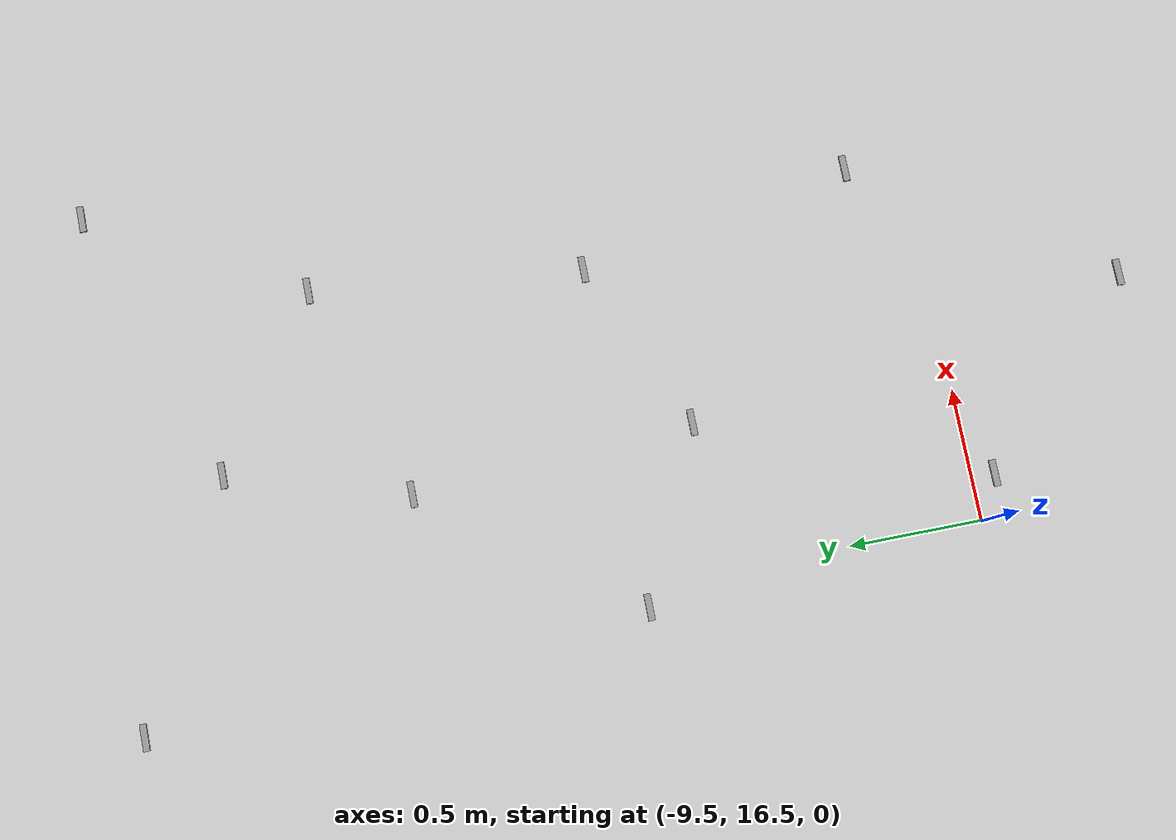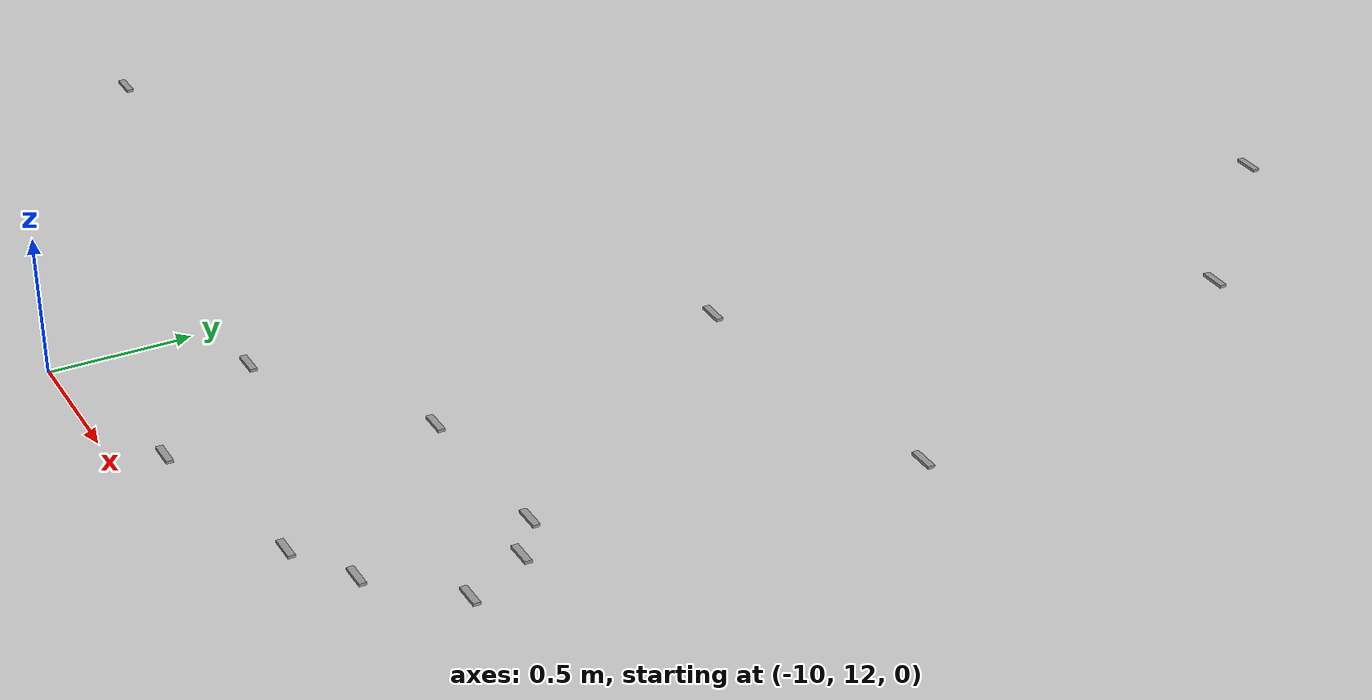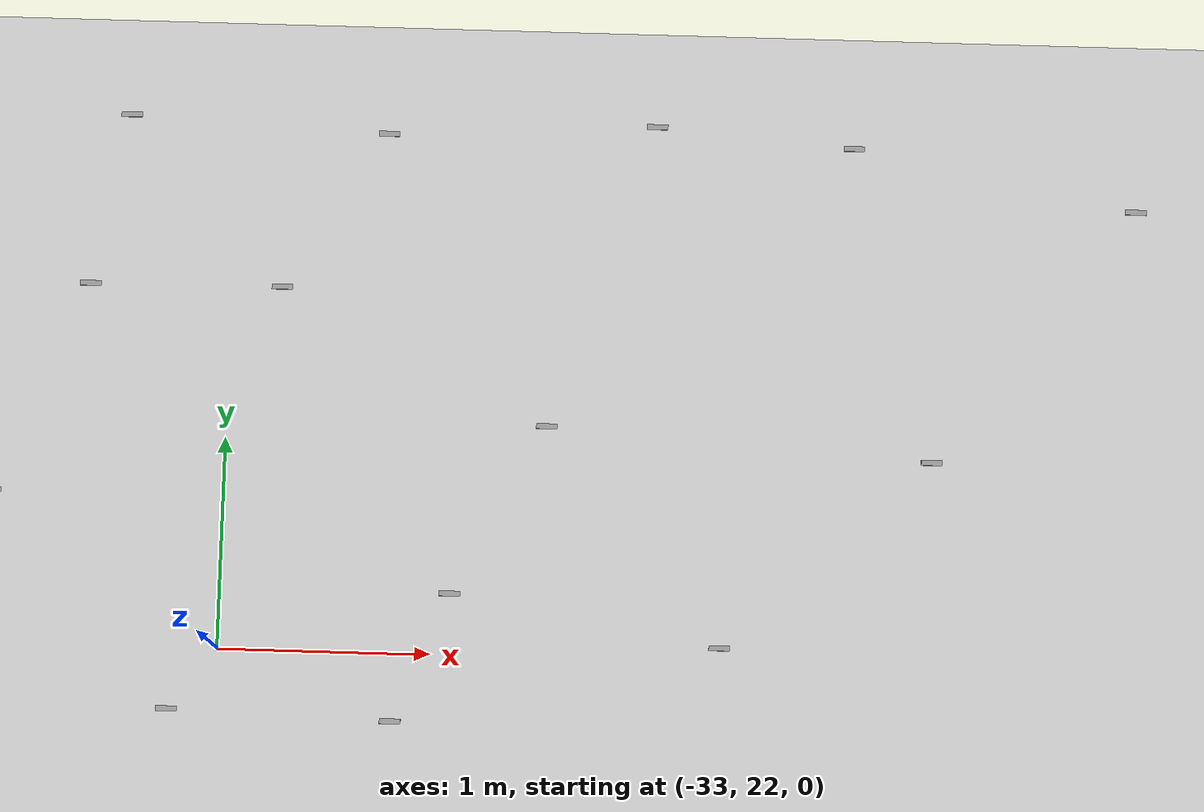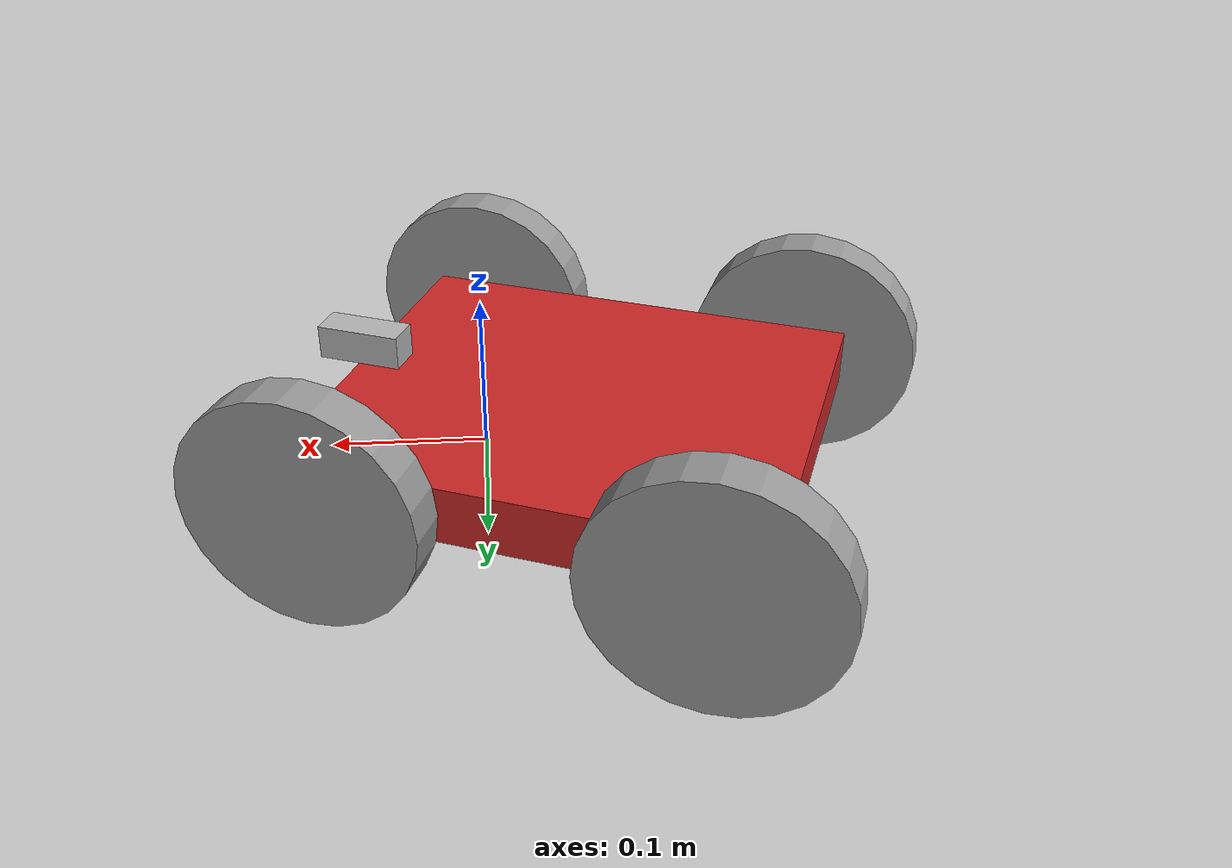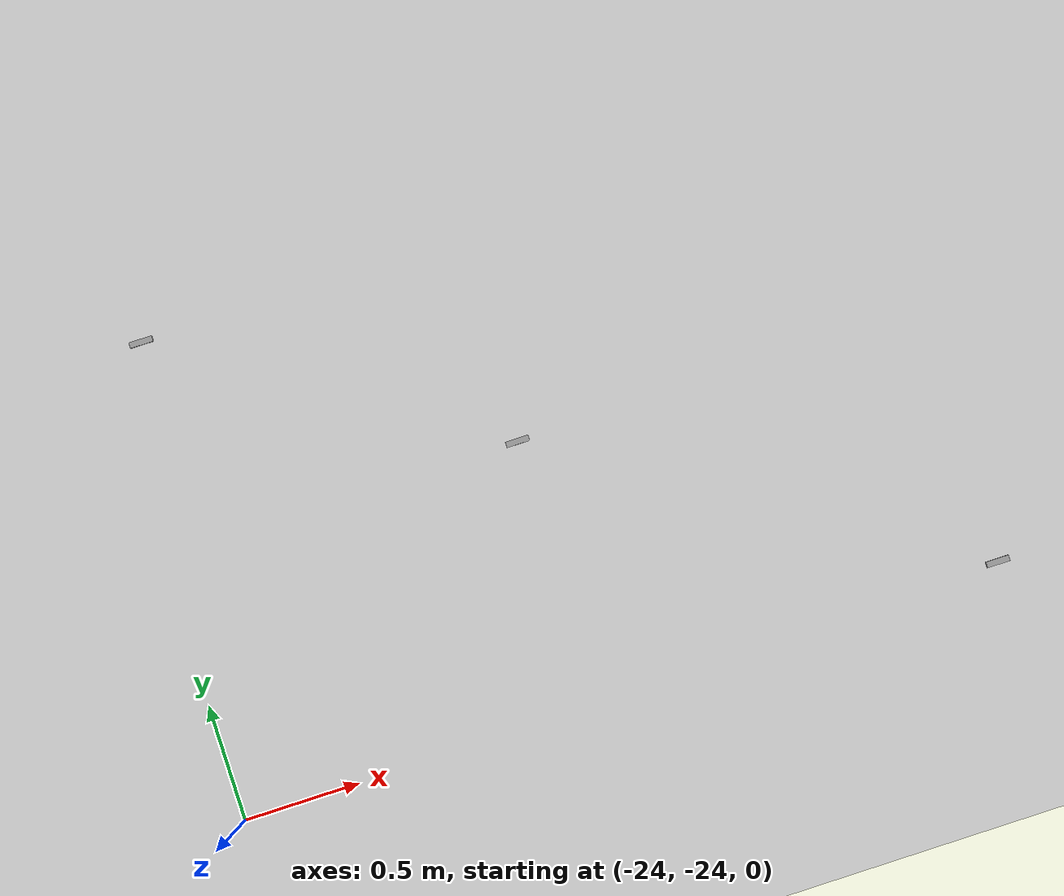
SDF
<sdf version="1.6">
 <world name="default">
  <light name="sun" type="directional">
   <pose>0 0 10 0 -0 0</pose>
   <diffuse>0.8 0.8 0.8 1</diffuse>
   <specular>0.2 0.2 0.2 1</specular>
   <attenuation>
    <range>1000</range>
    <constant>0.9</constant>
    <linear>0.01</linear>
    <quadratic>0.001</quadratic>
   </attenuation>
   <direction>-0.5 0.1 -0.9</direction>
  </light>
  <model name="smile_map">
   <static>1</static>
   <link name="link">
    <collision name="collision">
     <geometry><plane><size>70 50</size><normal>0 0 1</normal></plane></geometry>
     <surface><friction><ode><mu>100</mu><mu2>50</mu2></ode></friction></surface>
    </collision>
    <visual name="visual">
     <geometry><plane><size>70 50</size><normal>0 0 1</normal></plane></geometry>
     <material>
      <script><uri>file://media/materials/scripts/smile.material</uri><name>Smile/Map</name></script>
     </material>
    </visual>
   </link>
  </model>
  <gravity>0 0 -9.8</gravity>
  <magnetic_field>6e-06 2.3e-05 -4.2e-05</magnetic_field>
  <atmosphere type="adiabatic"/>
  <physics name="default_physics" default="0" type="ode">
   <max_step_size>0.001</max_step_size>
   <real_time_factor>1</real_time_factor>
   <real_time_update_rate>1000</real_time_update_rate>
  </physics>
  <scene><ambient>0.4 0.4 0.4 1</ambient><background>0.7 0.7 0.7 1</background><shadows>1</shadows></scene>
  <audio><device>default</device></audio>
  <spherical_coordinates>
   <surface_model>EARTH_WGS84</surface_model>
   <latitude_deg>0</latitude_deg>
   <longitude_deg>0</longitude_deg>
   <elevation>0</elevation>
   <heading_deg>0</heading_deg>
  </spherical_coordinates>
  <model name="/smile">
   <link name="base_link">
    <inertial>
     <mass>1</mass>
     <inertia>
      <ixx>0.00602108</ixx>
      <ixy>0</ixy>
      <ixz>0</ixz>
      <iyy>0.00444851</iyy>
      <iyz>0</iyz>
      <izz>0.0102822</izz>
     </inertia>
    </inertial>
    <collision name="base_link_fixed_joint_lump__chassis_collision">
     <geometry><box><size>0.2667 0.2286 0.033528</size></box></geometry>
    </collision>
    <collision name="base_link_fixed_joint_lump__camera_link_collision_1">
     <pose>0.13335 0 0.026764 0 -0 0</pose>
     <geometry><box><size>0.05 0.02 0.02</size></box></geometry>
    </collision>
    <visual name="base_link_fixed_joint_lump__chassis_visual">
     <geometry><box><size>0.2667 0.2286 0.033528</size></box></geometry>
     <material>
      <script><name>Gazebo/Red</name><uri>file://media/materials/scripts/gazebo.material</uri></script>
     </material>
    </visual>
    <visual name="base_link_fixed_joint_lump__camera_link_visual_1">
     <pose>0.13335 0 0.026764 0 -0 0</pose>
     <geometry><box><size>0.05 0.02 0.02</size></box></geometry>
     <material><script><uri>__default__</uri><name>__default__</name></script></material>
    </visual>
    <sensor name="camera1" type="camera">
     <update_rate>30</update_rate>
     <camera name="head">
      <horizontal_fov>1.39626</horizontal_fov>
      <image><width>800</width><height>800</height><format>R8G8B8</format></image>
      <clip><near>0.02</near><far>300</far></clip>
      <noise><type>gaussian</type><mean>0</mean><stddev>0.007</stddev></noise>
     </camera>
     <plugin name="camera_controller" filename="libgazebo_ros_camera.so">
      <alwaysOn>1</alwaysOn>
      <updateRate>0.0</updateRate>
      <cameraName>smile/camera1</cameraName>
      <imageTopicName>image_raw</imageTopicName>
      <cameraInfoTopicName>camera_info</cameraInfoTopicName>
      <frameName>camera_link</frameName>
      <hackBaseline>0.07</hackBaseline>
      <distortionK1>0.0</distortionK1>
      <distortionK2>0.0</distortionK2>
      <distortionK3>0.0</distortionK3>
      <distortionT1>0.0</distortionT1>
      <distortionT2>0.0</distortionT2>
      <robotNamespace>/</robotNamespace>
     </plugin>
     <pose>0.13335 0 0.026764 0 -0 0</pose>
    </sensor>
    <sensor name="imu_sensor" type="imu">
     <always_on>1</always_on>
     <update_rate>100</update_rate>
     <visualize>1</visualize>
     <topic>__default_topic__</topic>
     <plugin name="imu_plugin" filename="libgazebo_ros_imu_sensor.so">
      <topicName>smile/imu</topicName>
      <bodyName>imu_link</bodyName>
      <updateRateHZ>10.0</updateRateHZ>
      <gaussianNoise>0.0</gaussianNoise>
      <xyzOffset>0 0 0</xyzOffset>
      <rpyOffset>0 0 0</rpyOffset>
      <frameName>imu_link</frameName>
      <initialOrientationAsReference>0</initialOrientationAsReference>
      <robotNamespace>/</robotNamespace>
     </plugin>
    </sensor>
   </link>
   <link name="left_back_wheel">
    <pose>-0.10795 0.1143 0 0 -0 0</pose>
    <inertial>
     <pose>0 0.0127 0 0 1.57075 1.57075</pose>
     <mass>0.5</mass>
     <inertia><ixx>0.01</ixx><ixy>0</ixy><ixz>0</ixz><iyy>0.0011758</iyy><iyz>0</iyz><izz>0.01</izz></inertia>
    </inertial>
    <collision name="left_back_wheel_collision">
     <pose>0 0.0127 0 3.14159 1.57079 -1.57084</pose>
     <geometry><cylinder><length>0.0254</length><radius>0.06858</radius></cylinder></geometry>
     <surface><friction><ode><mu>0.5</mu><mu2>0.5</mu2></ode></friction></surface>
    </collision>
    <visual name="left_back_wheel_visual">
     <pose>0 0.0127 0 3.14159 1.57079 -1.57084</pose>
     <geometry><cylinder><length>0.0254</length><radius>0.06858</radius></cylinder></geometry>
     <material>
      <script><name>Gazebo/Grey</name><uri>file://media/materials/scripts/gazebo.material</uri></script>
     </material>
    </visual>
   </link>
   <joint name="base_to_left_back_wheel" type="revolute">
    <child>left_back_wheel</child>
    <parent>base_link</parent>
    <axis>
     <xyz>0 1 0</xyz>
     <limit><lower>-1e+16</lower><upper>1e+16</upper></limit>
     <dynamics>
      <damping>1.5</damping>
      <friction>0</friction>
      <spring_reference>0</spring_reference>
      <spring_stiffness>0</spring_stiffness>
     </dynamics>
     <use_parent_model_frame>1</use_parent_model_frame>
    </axis>
   </joint>
   <link name="left_front_wheel">
    <pose>0.10795 0.1143 0 0 -0 0</pose>
    <inertial>
     <pose>0 0.0127 0 0 1.57075 1.57075</pose>
     <mass>0.5</mass>
     <inertia><ixx>0.01</ixx><ixy>0</ixy><ixz>0</ixz><iyy>0.0011758</iyy><iyz>0</iyz><izz>0.01</izz></inertia>
    </inertial>
    <collision name="left_front_wheel_collision">
     <pose>0 0.0127 0 3.14159 1.57079 -1.57084</pose>
     <geometry><cylinder><length>0.0254</length><radius>0.06858</radius></cylinder></geometry>
     <surface><friction><ode><mu>0.5</mu><mu2>0.5</mu2></ode></friction></surface>
    </collision>
    <visual name="left_front_wheel_visual">
     <pose>0 0.0127 0 3.14159 1.57079 -1.57084</pose>
     <geometry><cylinder><length>0.0254</length><radius>0.06858</radius></cylinder></geometry>
     <material>
      <script><name>Gazebo/Grey</name><uri>file://media/materials/scripts/gazebo.material</uri></script>
     </material>
    </visual>
   </link>
   <joint name="base_to_left_front_wheel" type="revolute">
    <child>left_front_wheel</child>
    <parent>base_link</parent>
    <axis>
     <xyz>0 1 0</xyz>
     <limit><lower>-1e+16</lower><upper>1e+16</upper></limit>
     <dynamics>
      <damping>1.5</damping>
      <friction>0</friction>
      <spring_reference>0</spring_reference>
      <spring_stiffness>0</spring_stiffness>
     </dynamics>
     <use_parent_model_frame>1</use_parent_model_frame>
    </axis>
   </joint>
   <link name="right_back_wheel">
    <pose>-0.10795 -0.1143 0 0 -0 0</pose>
    <inertial>
     <pose>0 -0.0127 0 0 1.57075 1.57075</pose>
     <mass>0.5</mass>
     <inertia><ixx>0.01</ixx><ixy>0</ixy><ixz>0</ixz><iyy>0.0011758</iyy><iyz>0</iyz><izz>0.01</izz></inertia>
    </inertial>
    <collision name="right_back_wheel_collision">
     <pose>0 -0.0127 0 3.14159 1.57079 -1.57084</pose>
     <geometry><cylinder><length>0.0254</length><radius>0.06858</radius></cylinder></geometry>
     <surface><friction><ode><mu>0.5</mu><mu2>0.5</mu2></ode></friction></surface>
    </collision>
    <visual name="right_back_wheel_visual">
     <pose>0 -0.0127 0 3.14159 1.57079 -1.57084</pose>
     <geometry><cylinder><length>0.0254</length><radius>0.06858</radius></cylinder></geometry>
     <material>
      <script><name>Gazebo/Grey</name><uri>file://media/materials/scripts/gazebo.material</uri></script>
     </material>
    </visual>
   </link>
   <joint name="base_to_right_back_wheel" type="revolute">
    <child>right_back_wheel</child>
    <parent>base_link</parent>
    <axis>
     <xyz>0 1 0</xyz>
     <limit><lower>-1e+16</lower><upper>1e+16</upper></limit>
     <dynamics>
      <damping>1.5</damping>
      <friction>0</friction>
      <spring_reference>0</spring_reference>
      <spring_stiffness>0</spring_stiffness>
     </dynamics>
     <use_parent_model_frame>1</use_parent_model_frame>
    </axis>
   </joint>
   <link name="right_front_wheel">
    <pose>0.10795 -0.1143 0 0 -0 0</pose>
    <inertial>
     <pose>0 -0.0127 0 0 1.57075 1.57075</pose>
     <mass>0.5</mass>
     <inertia><ixx>0.01</ixx><ixy>0</ixy><ixz>0</ixz><iyy>0.0011758</iyy><iyz>0</iyz><izz>0.01</izz></inertia>
    </inertial>
    <collision name="right_front_wheel_collision">
     <pose>0 -0.0127 0 3.14159 1.57079 -1.57084</pose>
     <geometry><cylinder><length>0.0254</length><radius>0.06858</radius></cylinder></geometry>
     <surface><friction><ode><mu>0.5</mu><mu2>0.5</mu2></ode></friction></surface>
    </collision>
    <visual name="right_front_wheel_visual">
     <pose>0 -0.0127 0 3.14159 1.57079 -1.57084</pose>
     <geometry><cylinder><length>0.0254</length><radius>0.06858</radius></cylinder></geometry>
     <material>
      <script><name>Gazebo/Grey</name><uri>file://media/materials/scripts/gazebo.material</uri></script>
     </material>
    </visual>
   </link>
   <joint name="base_to_right_front_wheel" type="revolute">
    <child>right_front_wheel</child>
    <parent>base_link</parent>
    <axis>
     <xyz>0 1 0</xyz>
     <limit><lower>-1e+16</lower><upper>1e+16</upper></limit>
     <dynamics>
      <damping>1.5</damping>
      <friction>0</friction>
      <spring_reference>0</spring_reference>
      <spring_stiffness>0</spring_stiffness>
     </dynamics>
     <use_parent_model_frame>1</use_parent_model_frame>
    </axis>
   </joint>
   <static>0</static>
   <plugin name="gazebo_ros_control" filename="libgazebo_ros_control.so">
    <robotNamespace>/smile</robotNamespace>
   </plugin>
   <pose>-0.055703 0.084259 0.06858 0 -0 -0.382953</pose>
  </model>
  <model name="unit_cylinder_clone">
   <pose>21.7004 15.391 0.919296 -1e-06 1e-06 -0.004085</pose>
   <link name="link">
    <inertial>
     <mass>1</mass>
     <inertia><ixx>0.145833</ixx><ixy>0</ixy><ixz>0</ixz><iyy>0.145833</iyy><iyz>0</iyz><izz>0.125</izz></inertia>
    </inertial>
    <collision name="collision">
     <geometry><cylinder><radius>0.0431855</radius><length>1.83861</length></cylinder></geometry>
    </collision>
    <visual name="visual">
     <geometry><cylinder><radius>0.0431855</radius><length>1.83861</length></cylinder></geometry>
     <material>
      <script><name>Gazebo/Grey</name><uri>file://media/materials/scripts/gazebo.material</uri></script>
     </material>
    </visual>
   </link>
  </model>
  <model name="unit_cylinder_clone_0">
   <pose>18.8315 12.5489 0.919305 -1e-06 -1e-06 -0.004325</pose>
   <link name="link">
    <inertial>
     <mass>1</mass>
     <inertia><ixx>0.145833</ixx><ixy>0</ixy><ixz>0</ixz><iyy>0.145833</iyy><iyz>0</iyz><izz>0.125</izz></inertia>
    </inertial>
    <collision name="collision">
     <geometry><cylinder><radius>0.0431855</radius><length>1.83861</length></cylinder></geometry>
    </collision>
    <visual name="visual">
     <geometry><cylinder><radius>0.0431855</radius><length>1.83861</length></cylinder></geometry>
     <material>
      <script><name>Gazebo/Grey</name><uri>file://media/materials/scripts/gazebo.material</uri></script>
     </material>
    </visual>
   </link>
  </model>
  <model name="unit_cylinder_clone_1">
   <pose>32.151 2.77257 0.919519 0.005241 -0.000224 -0.000662</pose>
   <link name="link">
    <inertial>
     <mass>1</mass>
     <inertia><ixx>0.145833</ixx><ixy>0</ixy><ixz>0</ixz><iyy>0.145833</iyy><iyz>0</iyz><izz>0.125</izz></inertia>
    </inertial>
    <collision name="collision">
     <geometry><cylinder><radius>0.0431855</radius><length>1.83861</length></cylinder></geometry>
    </collision>
    <visual name="visual">
     <geometry><cylinder><radius>0.0431855</radius><length>1.83861</length></cylinder></geometry>
     <material>
      <script><name>Gazebo/Grey</name><uri>file://media/materials/scripts/gazebo.material</uri></script>
     </material>
    </visual>
   </link>
  </model>
  <model name="unit_cylinder_clone_2">
   <pose>34.8396 0.020929 0.919296 2e-06 5e-06 -0.003592</pose>
   <link name="link">
    <inertial>
     <mass>1</mass>
     <inertia><ixx>0.145833</ixx><ixy>0</ixy><ixz>0</ixz><iyy>0.145833</iyy><iyz>0</iyz><izz>0.125</izz></inertia>
    </inertial>
    <collision name="collision">
     <geometry><cylinder><radius>0.0431855</radius><length>1.83861</length></cylinder></geometry>
    </collision>
    <visual name="visual">
     <geometry><cylinder><radius>0.0431855</radius><length>1.83861</length></cylinder></geometry>
     <material>
      <script><name>Gazebo/Grey</name><uri>file://media/materials/scripts/gazebo.material</uri></script>
     </material>
    </visual>
   </link>
  </model>
  <model name="unit_cylinder_clone_3">
   <pose>32.2379 -0.050909 0.919296 -1e-06 -0 -0.004848</pose>
   <link name="link">
    <inertial>
     <mass>1</mass>
     <inertia><ixx>0.145833</ixx><ixy>0</ixy><ixz>0</ixz><iyy>0.145833</iyy><iyz>0</iyz><izz>0.125</izz></inertia>
    </inertial>
    <collision name="collision">
     <geometry><cylinder><radius>0.0431855</radius><length>1.83861</length></cylinder></geometry>
    </collision>
    <visual name="visual">
     <geometry><cylinder><radius>0.0431855</radius><length>1.83861</length></cylinder></geometry>
     <material>
      <script><name>Gazebo/Grey</name><uri>file://media/materials/scripts/gazebo.material</uri></script>
     </material>
    </visual>
   </link>
  </model>
  <model name="stone_10_2_5_1cm">
   <link name="link">
    <pose>0 0 0.005 0 -0 0</pose>
    <inertial>
     <mass>0.0628</mass>
     <inertia>
      <ixx>3.79417e-06</ixx>
      <ixy>0</ixy>
      <ixz>0</ixz>
      <iyy>5.28567e-05</iyy>
      <iyz>0</iyz>
      <izz>5.56042e-05</izz>
     </inertia>
    </inertial>
    <collision name="collision">
     <geometry><box><size>0.1 0.025 0.01</size></box></geometry>
     <surface>
      <contact>
       <poissons_ratio>0.15</poissons_ratio>
       <elastic_modulus>8e+10</elastic_modulus>
       <ode><kp>100000</kp><kd>100</kd><max_vel>100</max_vel><min_depth>0.001</min_depth></ode>
      </contact>
      <friction>
       <torsional>
        <coefficient>1</coefficient>
        <use_patch_radius>0</use_patch_radius>
        <surface_radius>0.01</surface_radius>
       </torsional>
      </friction>
     </surface>
    </collision>
    <visual name="visual">
     <geometry><box><size>0.1 0.025 0.01</size></box></geometry>
     <material>
      <script><uri>file://media/materials/scripts/gazebo.material</uri><name>Gazebo/Grey</name></script>
     </material>
    </visual>
   </link>
   <pose>-7.81072 10.2221 -0.001002 -0 -0 -0</pose>
  </model>
  <model name="stone_10_2_5_1cm_clone">
   <link name="link">
    <pose>0 0 0.005 0 -0 0</pose>
    <inertial>
     <mass>0.0628</mass>
     <inertia>
      <ixx>3.79417e-06</ixx>
      <ixy>0</ixy>
      <ixz>0</ixz>
      <iyy>5.28567e-05</iyy>
      <iyz>0</iyz>
      <izz>5.56042e-05</izz>
     </inertia>
    </inertial>
    <collision name="collision">
     <geometry><box><size>0.1 0.025 0.01</size></box></geometry>
     <surface>
      <contact>
       <poissons_ratio>0.15</poissons_ratio>
       <elastic_modulus>8e+10</elastic_modulus>
       <ode><kp>100000</kp><kd>100</kd><max_vel>100</max_vel><min_depth>0.001</min_depth></ode>
      </contact>
      <friction>
       <torsional>
        <coefficient>1</coefficient>
        <use_patch_radius>0</use_patch_radius>
        <surface_radius>0.01</surface_radius>
       </torsional>
      </friction>
     </surface>
    </collision>
    <visual name="visual">
     <geometry><box><size>0.1 0.025 0.01</size></box></geometry>
     <material>
      <script><uri>file://media/materials/scripts/gazebo.material</uri><name>Gazebo/Grey</name></script>
     </material>
    </visual>
   </link>
   <pose>-8.45813 13.0295 -0.001002 -0 -0 -0</pose>
  </model>
  <model name="stone_10_2_5_1cm_clone_0">
   <link name="link">
    <pose>0 0 0.005 0 -0 0</pose>
    <inertial>
     <mass>0.0628</mass>
     <inertia>
      <ixx>3.79417e-06</ixx>
      <ixy>0</ixy>
      <ixz>0</ixz>
      <iyy>5.28567e-05</iyy>
      <iyz>0</iyz>
      <izz>5.56042e-05</izz>
     </inertia>
    </inertial>
    <collision name="collision">
     <geometry><box><size>0.1 0.025 0.01</size></box></geometry>
     <surface>
      <contact>
       <poissons_ratio>0.15</poissons_ratio>
       <elastic_modulus>8e+10</elastic_modulus>
       <ode><kp>100000</kp><kd>100</kd><max_vel>100</max_vel><min_depth>0.001</min_depth></ode>
      </contact>
      <friction>
       <torsional>
        <coefficient>1</coefficient>
        <use_patch_radius>0</use_patch_radius>
        <surface_radius>0.01</surface_radius>
       </torsional>
      </friction>
     </surface>
    </collision>
    <visual name="visual">
     <geometry><box><size>0.1 0.025 0.01</size></box></geometry>
     <material>
      <script><uri>file://media/materials/scripts/gazebo.material</uri><name>Gazebo/Grey</name></script>
     </material>
    </visual>
   </link>
   <pose>-8.29328 12.9229 -0.001002 -0 -0 -0</pose>
  </model>
  <model name="stone_10_2_5_1cm_clone_1">
   <link name="link">
    <pose>0 0 0.005 0 -0 0</pose>
    <inertial>
     <mass>0.0628</mass>
     <inertia>
      <ixx>3.79417e-06</ixx>
      <ixy>0</ixy>
      <ixz>0</ixz>
      <iyy>5.28567e-05</iyy>
      <iyz>0</iyz>
      <izz>5.56042e-05</izz>
     </inertia>
    </inertial>
    <collision name="collision">
     <geometry><box><size>0.1 0.025 0.01</size></box></geometry>
     <surface>
      <contact>
       <poissons_ratio>0.15</poissons_ratio>
       <elastic_modulus>8e+10</elastic_modulus>
       <ode><kp>100000</kp><kd>100</kd><max_vel>100</max_vel><min_depth>0.001</min_depth></ode>
      </contact>
      <friction>
       <torsional>
        <coefficient>1</coefficient>
        <use_patch_radius>0</use_patch_radius>
        <surface_radius>0.01</surface_radius>
       </torsional>
      </friction>
     </surface>
    </collision>
    <visual name="visual">
     <geometry><box><size>0.1 0.025 0.01</size></box></geometry>
     <material>
      <script><uri>file://media/materials/scripts/gazebo.material</uri><name>Gazebo/Grey</name></script>
     </material>
    </visual>
   </link>
   <pose>-8.16754 12.6945 -0.001002 -0 -0 -0</pose>
  </model>
  <model name="stone_10_2_5_1cm_clone_2">
   <link name="link">
    <pose>0 0 0.005 0 -0 0</pose>
    <inertial>
     <mass>0.0628</mass>
     <inertia>
      <ixx>3.79417e-06</ixx>
      <ixy>0</ixy>
      <ixz>0</ixz>
      <iyy>5.28567e-05</iyy>
      <iyz>0</iyz>
      <izz>5.56042e-05</izz>
     </inertia>
    </inertial>
    <collision name="collision">
     <geometry><box><size>0.1 0.025 0.01</size></box></geometry>
     <surface>
      <contact>
       <poissons_ratio>0.15</poissons_ratio>
       <elastic_modulus>8e+10</elastic_modulus>
       <ode><kp>100000</kp><kd>100</kd><max_vel>100</max_vel><min_depth>0.001</min_depth></ode>
      </contact>
      <friction>
       <torsional>
        <coefficient>1</coefficient>
        <use_patch_radius>0</use_patch_radius>
        <surface_radius>0.01</surface_radius>
       </torsional>
      </friction>
     </surface>
    </collision>
    <visual name="visual">
     <geometry><box><size>0.1 0.025 0.01</size></box></geometry>
     <material>
      <script><uri>file://media/materials/scripts/gazebo.material</uri><name>Gazebo/Grey</name></script>
     </material>
    </visual>
   </link>
   <pose>-8.41969 12.4366 -0.001002 -0 -0 -0</pose>
  </model>
  <model name="stone_10_2_5_1cm_clone_3">
   <link name="link">
    <pose>0 0 0.005 0 -0 0</pose>
    <inertial>
     <mass>0.0628</mass>
     <inertia>
      <ixx>3.79417e-06</ixx>
      <ixy>0</ixy>
      <ixz>0</ixz>
      <iyy>5.28567e-05</iyy>
      <iyz>0</iyz>
      <izz>5.56042e-05</izz>
     </inertia>
    </inertial>
    <collision name="collision">
     <geometry><box><size>0.1 0.025 0.01</size></box></geometry>
     <surface>
      <contact>
       <poissons_ratio>0.15</poissons_ratio>
       <elastic_modulus>8e+10</elastic_modulus>
       <ode><kp>100000</kp><kd>100</kd><max_vel>100</max_vel><min_depth>0.001</min_depth></ode>
      </contact>
      <friction>
       <torsional>
        <coefficient>1</coefficient>
        <use_patch_radius>0</use_patch_radius>
        <surface_radius>0.01</surface_radius>
       </torsional>
      </friction>
     </surface>
    </collision>
    <visual name="visual">
     <geometry><box><size>0.1 0.025 0.01</size></box></geometry>
     <material>
      <script><uri>file://media/materials/scripts/gazebo.material</uri><name>Gazebo/Grey</name></script>
     </material>
    </visual>
   </link>
   <pose>-8.65563 12.3046 -0.001002 -0 -0 -0</pose>
  </model>
  <model name="stone_10_2_5_1cm_clone_4">
   <link name="link">
    <pose>0 0 0.005 0 -0 0</pose>
    <inertial>
     <mass>0.0628</mass>
     <inertia>
      <ixx>3.79417e-06</ixx>
      <ixy>0</ixy>
      <ixz>0</ixz>
      <iyy>5.28567e-05</iyy>
      <iyz>0</iyz>
      <izz>5.56042e-05</izz>
     </inertia>
    </inertial>
    <collision name="collision">
     <geometry><box><size>0.1 0.025 0.01</size></box></geometry>
     <surface>
      <contact>
       <poissons_ratio>0.15</poissons_ratio>
       <elastic_modulus>8e+10</elastic_modulus>
       <ode><kp>100000</kp><kd>100</kd><max_vel>100</max_vel><min_depth>0.001</min_depth></ode>
      </contact>
      <friction>
       <torsional>
        <coefficient>1</coefficient>
        <use_patch_radius>0</use_patch_radius>
        <surface_radius>0.01</surface_radius>
       </torsional>
      </friction>
     </surface>
    </collision>
    <visual name="visual">
     <geometry><box><size>0.1 0.025 0.01</size></box></geometry>
     <material>
      <script><uri>file://media/materials/scripts/gazebo.material</uri><name>Gazebo/Grey</name></script>
     </material>
    </visual>
   </link>
   <pose>-9.33207 12.1629 -0.001002 -0 -0 -0</pose>
  </model>
  <model name="stone_10_2_5_1cm_clone_5">
   <link name="link">
    <pose>0 0 0.005 0 -0 0</pose>
    <inertial>
     <mass>0.0628</mass>
     <inertia>
      <ixx>3.79417e-06</ixx>
      <ixy>0</ixy>
      <ixz>0</ixz>
      <iyy>5.28567e-05</iyy>
      <iyz>0</iyz>
      <izz>5.56042e-05</izz>
     </inertia>
    </inertial>
    <collision name="collision">
     <geometry><box><size>0.1 0.025 0.01</size></box></geometry>
     <surface>
      <contact>
       <poissons_ratio>0.15</poissons_ratio>
       <elastic_modulus>8e+10</elastic_modulus>
       <ode><kp>100000</kp><kd>100</kd><max_vel>100</max_vel><min_depth>0.001</min_depth></ode>
      </contact>
      <friction>
       <torsional>
        <coefficient>1</coefficient>
        <use_patch_radius>0</use_patch_radius>
        <surface_radius>0.01</surface_radius>
       </torsional>
      </friction>
     </surface>
    </collision>
    <visual name="visual">
     <geometry><box><size>0.1 0.025 0.01</size></box></geometry>
     <material>
      <script><uri>file://media/materials/scripts/gazebo.material</uri><name>Gazebo/Grey</name></script>
     </material>
    </visual>
   </link>
   <pose>-9.73583 12.6034 -0.001002 -0 -0 -0</pose>
  </model>
  <model name="stone_10_2_5_1cm_clone_6">
   <link name="link">
    <pose>0 0 0.005 0 -0 0</pose>
    <inertial>
     <mass>0.0628</mass>
     <inertia>
      <ixx>3.79417e-06</ixx>
      <ixy>0</ixy>
      <ixz>0</ixz>
      <iyy>5.28567e-05</iyy>
      <iyz>0</iyz>
      <izz>5.56042e-05</izz>
     </inertia>
    </inertial>
    <collision name="collision">
     <geometry><box><size>0.1 0.025 0.01</size></box></geometry>
     <surface>
      <contact>
       <poissons_ratio>0.15</poissons_ratio>
       <elastic_modulus>8e+10</elastic_modulus>
       <ode><kp>100000</kp><kd>100</kd><max_vel>100</max_vel><min_depth>0.001</min_depth></ode>
      </contact>
      <friction>
       <torsional>
        <coefficient>1</coefficient>
        <use_patch_radius>0</use_patch_radius>
        <surface_radius>0.01</surface_radius>
       </torsional>
      </friction>
     </surface>
    </collision>
    <visual name="visual">
     <geometry><box><size>0.1 0.025 0.01</size></box></geometry>
     <material>
      <script><uri>file://media/materials/scripts/gazebo.material</uri><name>Gazebo/Grey</name></script>
     </material>
    </visual>
   </link>
   <pose>-9.09754 12.9989 -0.001002 -0 -0 -0</pose>
  </model>
  <model name="stone_10_2_5_1cm_clone_7">
   <link name="link">
    <pose>0 0 0.005 0 -0 0</pose>
    <inertial>
     <mass>0.0628</mass>
     <inertia>
      <ixx>3.79417e-06</ixx>
      <ixy>0</ixy>
      <ixz>0</ixz>
      <iyy>5.28567e-05</iyy>
      <iyz>0</iyz>
      <izz>5.56042e-05</izz>
     </inertia>
    </inertial>
    <collision name="collision">
     <geometry><box><size>0.1 0.025 0.01</size></box></geometry>
     <surface>
      <contact>
       <poissons_ratio>0.15</poissons_ratio>
       <elastic_modulus>8e+10</elastic_modulus>
       <ode><kp>100000</kp><kd>100</kd><max_vel>100</max_vel><min_depth>0.001</min_depth></ode>
      </contact>
      <friction>
       <torsional>
        <coefficient>1</coefficient>
        <use_patch_radius>0</use_patch_radius>
        <surface_radius>0.01</surface_radius>
       </torsional>
      </friction>
     </surface>
    </collision>
    <visual name="visual">
     <geometry><box><size>0.1 0.025 0.01</size></box></geometry>
     <material>
      <script><uri>file://media/materials/scripts/gazebo.material</uri><name>Gazebo/Grey</name></script>
     </material>
    </visual>
   </link>
   <pose>-9.30071 14.1279 -0.001002 -0 -0 -0</pose>
  </model>
  <model name="stone_10_2_5_1cm_clone_8">
   <link name="link">
    <pose>0 0 0.005 0 -0 0</pose>
    <inertial>
     <mass>0.0628</mass>
     <inertia>
      <ixx>3.79417e-06</ixx>
      <ixy>0</ixy>
      <ixz>0</ixz>
      <iyy>5.28567e-05</iyy>
      <iyz>0</iyz>
      <izz>5.56042e-05</izz>
     </inertia>
    </inertial>
    <collision name="collision">
     <geometry><box><size>0.1 0.025 0.01</size></box></geometry>
     <surface>
      <contact>
       <poissons_ratio>0.15</poissons_ratio>
       <elastic_modulus>8e+10</elastic_modulus>
       <ode><kp>100000</kp><kd>100</kd><max_vel>100</max_vel><min_depth>0.001</min_depth></ode>
      </contact>
      <friction>
       <torsional>
        <coefficient>1</coefficient>
        <use_patch_radius>0</use_patch_radius>
        <surface_radius>0.01</surface_radius>
       </torsional>
      </friction>
     </surface>
    </collision>
    <visual name="visual">
     <geometry><box><size>0.1 0.025 0.01</size></box></geometry>
     <material>
      <script><uri>file://media/materials/scripts/gazebo.material</uri><name>Gazebo/Grey</name></script>
     </material>
    </visual>
   </link>
   <pose>-9.33522 16.4152 -0.001002 -0 -0 -0</pose>
  </model>
  <model name="stone_10_2_5_1cm_clone_9">
   <link name="link">
    <pose>0 0 0.005 0 -0 0</pose>
    <inertial>
     <mass>0.0628</mass>
     <inertia>
      <ixx>3.79417e-06</ixx>
      <ixy>0</ixy>
      <ixz>0</ixz>
      <iyy>5.28567e-05</iyy>
      <iyz>0</iyz>
      <izz>5.56042e-05</izz>
     </inertia>
    </inertial>
    <collision name="collision">
     <geometry><box><size>0.1 0.025 0.01</size></box></geometry>
     <surface>
      <contact>
       <poissons_ratio>0.15</poissons_ratio>
       <elastic_modulus>8e+10</elastic_modulus>
       <ode><kp>100000</kp><kd>100</kd><max_vel>100</max_vel><min_depth>0.001</min_depth></ode>
      </contact>
      <friction>
       <torsional>
        <coefficient>1</coefficient>
        <use_patch_radius>0</use_patch_radius>
        <surface_radius>0.01</surface_radius>
       </torsional>
      </friction>
     </surface>
    </collision>
    <visual name="visual">
     <geometry><box><size>0.1 0.025 0.01</size></box></geometry>
     <material>
      <script><uri>file://media/materials/scripts/gazebo.material</uri><name>Gazebo/Grey</name></script>
     </material>
    </visual>
   </link>
   <pose>-8.17159 14.2737 -0.001002 -0 -0 -0</pose>
  </model>
  <model name="stone_10_2_5_1cm_clone_10">
   <link name="link">
    <pose>0 0 0.005 0 -0 0</pose>
    <inertial>
     <mass>0.0628</mass>
     <inertia>
      <ixx>3.79417e-06</ixx>
      <ixy>0</ixy>
      <ixz>0</ixz>
      <iyy>5.28567e-05</iyy>
      <iyz>0</iyz>
      <izz>5.56042e-05</izz>
     </inertia>
    </inertial>
    <collision name="collision">
     <geometry><box><size>0.1 0.025 0.01</size></box></geometry>
     <surface>
      <contact>
       <poissons_ratio>0.15</poissons_ratio>
       <elastic_modulus>8e+10</elastic_modulus>
       <ode><kp>100000</kp><kd>100</kd><max_vel>100</max_vel><min_depth>0.001</min_depth></ode>
      </contact>
      <friction>
       <torsional>
        <coefficient>1</coefficient>
        <use_patch_radius>0</use_patch_radius>
        <surface_radius>0.01</surface_radius>
       </torsional>
      </friction>
     </surface>
    </collision>
    <visual name="visual">
     <geometry><box><size>0.1 0.025 0.01</size></box></geometry>
     <material>
      <script><uri>file://media/materials/scripts/gazebo.material</uri><name>Gazebo/Grey</name></script>
     </material>
    </visual>
   </link>
   <pose>-8.68201 15.7828 -0.001002 -0 -0 -0</pose>
  </model>
  <model name="stone_10_2_5_1cm_clone_11">
   <link name="link">
    <pose>0 0 0.005 0 -0 0</pose>
    <inertial>
     <mass>0.0628</mass>
     <inertia>
      <ixx>3.79417e-06</ixx>
      <ixy>0</ixy>
      <ixz>0</ixz>
      <iyy>5.28567e-05</iyy>
      <iyz>0</iyz>
      <izz>5.56042e-05</izz>
     </inertia>
    </inertial>
    <collision name="collision">
     <geometry><box><size>0.1 0.025 0.01</size></box></geometry>
     <surface>
      <contact>
       <poissons_ratio>0.15</poissons_ratio>
       <elastic_modulus>8e+10</elastic_modulus>
       <ode><kp>100000</kp><kd>100</kd><max_vel>100</max_vel><min_depth>0.001</min_depth></ode>
      </contact>
      <friction>
       <torsional>
        <coefficient>1</coefficient>
        <use_patch_radius>0</use_patch_radius>
        <surface_radius>0.01</surface_radius>
       </torsional>
      </friction>
     </surface>
    </collision>
    <visual name="visual">
     <geometry><box><size>0.1 0.025 0.01</size></box></geometry>
     <material>
      <script><uri>file://media/materials/scripts/gazebo.material</uri><name>Gazebo/Grey</name></script>
     </material>
    </visual>
   </link>
   <pose>-8.08976 16.7115 -0.001002 -0 -0 -0</pose>
  </model>
  <model name="stone_10_2_5_1cm_clone_12">
   <link name="link">
    <pose>0 0 0.005 0 -0 0</pose>
    <inertial>
     <mass>0.0628</mass>
     <inertia>
      <ixx>3.79417e-06</ixx>
      <ixy>0</ixy>
      <ixz>0</ixz>
      <iyy>5.28567e-05</iyy>
      <iyz>0</iyz>
      <izz>5.56042e-05</izz>
     </inertia>
    </inertial>
    <collision name="collision">
     <geometry><box><size>0.1 0.025 0.01</size></box></geometry>
     <surface>
      <contact>
       <poissons_ratio>0.15</poissons_ratio>
       <elastic_modulus>8e+10</elastic_modulus>
       <ode><kp>100000</kp><kd>100</kd><max_vel>100</max_vel><min_depth>0.001</min_depth></ode>
      </contact>
      <friction>
       <torsional>
        <coefficient>1</coefficient>
        <use_patch_radius>0</use_patch_radius>
        <surface_radius>0.01</surface_radius>
       </torsional>
      </friction>
     </surface>
    </collision>
    <visual name="visual">
     <geometry><box><size>0.1 0.025 0.01</size></box></geometry>
     <material>
      <script><uri>file://media/materials/scripts/gazebo.material</uri><name>Gazebo/Grey</name></script>
     </material>
    </visual>
   </link>
   <pose>-8.28572 17.7646 -0.001002 -0 -0 -0</pose>
  </model>
  <model name="stone_10_2_5_1cm_clone_13">
   <link name="link">
    <pose>0 0 0.005 0 -0 0</pose>
    <inertial>
     <mass>0.0628</mass>
     <inertia>
      <ixx>3.79417e-06</ixx>
      <ixy>0</ixy>
      <ixz>0</ixz>
      <iyy>5.28567e-05</iyy>
      <iyz>0</iyz>
      <izz>5.56042e-05</izz>
     </inertia>
    </inertial>
    <collision name="collision">
     <geometry><box><size>0.1 0.025 0.01</size></box></geometry>
     <surface>
      <contact>
       <poissons_ratio>0.15</poissons_ratio>
       <elastic_modulus>8e+10</elastic_modulus>
       <ode><kp>100000</kp><kd>100</kd><max_vel>100</max_vel><min_depth>0.001</min_depth></ode>
      </contact>
      <friction>
       <torsional>
        <coefficient>1</coefficient>
        <use_patch_radius>0</use_patch_radius>
        <surface_radius>0.01</surface_radius>
       </torsional>
      </friction>
     </surface>
    </collision>
    <visual name="visual">
     <geometry><box><size>0.1 0.025 0.01</size></box></geometry>
     <material>
      <script><uri>file://media/materials/scripts/gazebo.material</uri><name>Gazebo/Grey</name></script>
     </material>
    </visual>
   </link>
   <pose>-8.93428 17.4795 -0.001002 -0 -0 -0</pose>
  </model>
  <model name="stone_10_2_5_1cm_clone_14">
   <link name="link">
    <pose>0 0 0.005 0 -0 0</pose>
    <inertial>
     <mass>0.0628</mass>
     <inertia>
      <ixx>3.79417e-06</ixx>
      <ixy>0</ixy>
      <ixz>0</ixz>
      <iyy>5.28567e-05</iyy>
      <iyz>0</iyz>
      <izz>5.56042e-05</izz>
     </inertia>
    </inertial>
    <collision name="collision">
     <geometry><box><size>0.1 0.025 0.01</size></box></geometry>
     <surface>
      <contact>
       <poissons_ratio>0.15</poissons_ratio>
       <elastic_modulus>8e+10</elastic_modulus>
       <ode><kp>100000</kp><kd>100</kd><max_vel>100</max_vel><min_depth>0.001</min_depth></ode>
      </contact>
      <friction>
       <torsional>
        <coefficient>1</coefficient>
        <use_patch_radius>0</use_patch_radius>
        <surface_radius>0.01</surface_radius>
       </torsional>
      </friction>
     </surface>
    </collision>
    <visual name="visual">
     <geometry><box><size>0.1 0.025 0.01</size></box></geometry>
     <material>
      <script><uri>file://media/materials/scripts/gazebo.material</uri><name>Gazebo/Grey</name></script>
     </material>
    </visual>
   </link>
   <pose>-9.57509 17.7734 -0.001002 -0 -0 -0</pose>
  </model>
  <model name="stone_10_2_5_1cm_clone_15">
   <link name="link">
    <pose>0 0 0.005 0 -0 0</pose>
    <inertial>
     <mass>0.0628</mass>
     <inertia>
      <ixx>3.79417e-06</ixx>
      <ixy>0</ixy>
      <ixz>0</ixz>
      <iyy>5.28567e-05</iyy>
      <iyz>0</iyz>
      <izz>5.56042e-05</izz>
     </inertia>
    </inertial>
    <collision name="collision">
     <geometry><box><size>0.1 0.025 0.01</size></box></geometry>
     <surface>
      <contact>
       <poissons_ratio>0.15</poissons_ratio>
       <elastic_modulus>8e+10</elastic_modulus>
       <ode><kp>100000</kp><kd>100</kd><max_vel>100</max_vel><min_depth>0.001</min_depth></ode>
      </contact>
      <friction>
       <torsional>
        <coefficient>1</coefficient>
        <use_patch_radius>0</use_patch_radius>
        <surface_radius>0.01</surface_radius>
       </torsional>
      </friction>
     </surface>
    </collision>
    <visual name="visual">
     <geometry><box><size>0.1 0.025 0.01</size></box></geometry>
     <material>
      <script><uri>file://media/materials/scripts/gazebo.material</uri><name>Gazebo/Grey</name></script>
     </material>
    </visual>
   </link>
   <pose>-8.16839 18.8004 -0.001002 -0 -0 -0</pose>
  </model>
  <model name="stone_10_2_5_1cm_clone_16">
   <link name="link">
    <pose>0 0 0.005 0 -0 0</pose>
    <inertial>
     <mass>0.0628</mass>
     <inertia>
      <ixx>3.79417e-06</ixx>
      <ixy>0</ixy>
      <ixz>0</ixz>
      <iyy>5.28567e-05</iyy>
      <iyz>0</iyz>
      <izz>5.56042e-05</izz>
     </inertia>
    </inertial>
    <collision name="collision">
     <geometry><box><size>0.1 0.025 0.01</size></box></geometry>
     <surface>
      <contact>
       <poissons_ratio>0.15</poissons_ratio>
       <elastic_modulus>8e+10</elastic_modulus>
       <ode><kp>100000</kp><kd>100</kd><max_vel>100</max_vel><min_depth>0.001</min_depth></ode>
      </contact>
      <friction>
       <torsional>
        <coefficient>1</coefficient>
        <use_patch_radius>0</use_patch_radius>
        <surface_radius>0.01</surface_radius>
       </torsional>
      </friction>
     </surface>
    </collision>
    <visual name="visual">
     <geometry><box><size>0.1 0.025 0.01</size></box></geometry>
     <material>
      <script><uri>file://media/materials/scripts/gazebo.material</uri><name>Gazebo/Grey</name></script>
     </material>
    </visual>
   </link>
   <pose>-9 18.5535 -0.001002 -0 -0 -0</pose>
  </model>
  <model name="stone_10_2_5_1cm_clone_17">
   <link name="link">
    <pose>0 0 0.005 0 -0 0</pose>
    <inertial>
     <mass>0.0628</mass>
     <inertia>
      <ixx>3.79417e-06</ixx>
      <ixy>0</ixy>
      <ixz>0</ixz>
      <iyy>5.28567e-05</iyy>
      <iyz>0</iyz>
      <izz>5.56042e-05</izz>
     </inertia>
    </inertial>
    <collision name="collision">
     <geometry><box><size>0.1 0.025 0.01</size></box></geometry>
     <surface>
      <contact>
       <poissons_ratio>0.15</poissons_ratio>
       <elastic_modulus>8e+10</elastic_modulus>
       <ode><kp>100000</kp><kd>100</kd><max_vel>100</max_vel><min_depth>0.001</min_depth></ode>
      </contact>
      <friction>
       <torsional>
        <coefficient>1</coefficient>
        <use_patch_radius>0</use_patch_radius>
        <surface_radius>0.01</surface_radius>
       </torsional>
      </friction>
     </surface>
    </collision>
    <visual name="visual">
     <geometry><box><size>0.1 0.025 0.01</size></box></geometry>
     <material>
      <script><uri>file://media/materials/scripts/gazebo.material</uri><name>Gazebo/Grey</name></script>
     </material>
    </visual>
   </link>
   <pose>-7.73158 19.5957 -0.001002 -0 -0 -0</pose>
  </model>
  <model name="stone_10_2_5_1cm_clone_18">
   <link name="link">
    <pose>0 0 0.005 0 -0 0</pose>
    <inertial>
     <mass>0.0628</mass>
     <inertia>
      <ixx>3.79417e-06</ixx>
      <ixy>0</ixy>
      <ixz>0</ixz>
      <iyy>5.28567e-05</iyy>
      <iyz>0</iyz>
      <izz>5.56042e-05</izz>
     </inertia>
    </inertial>
    <collision name="collision">
     <geometry><box><size>0.1 0.025 0.01</size></box></geometry>
     <surface>
      <contact>
       <poissons_ratio>0.15</poissons_ratio>
       <elastic_modulus>8e+10</elastic_modulus>
       <ode><kp>100000</kp><kd>100</kd><max_vel>100</max_vel><min_depth>0.001</min_depth></ode>
      </contact>
      <friction>
       <torsional>
        <coefficient>1</coefficient>
        <use_patch_radius>0</use_patch_radius>
        <surface_radius>0.01</surface_radius>
       </torsional>
      </friction>
     </surface>
    </collision>
    <visual name="visual">
     <geometry><box><size>0.1 0.025 0.01</size></box></geometry>
     <material>
      <script><uri>file://media/materials/scripts/gazebo.material</uri><name>Gazebo/Grey</name></script>
     </material>
    </visual>
   </link>
   <pose>-8.79656 19.2326 -0.001002 -0 -0 -0</pose>
  </model>
  <model name="stone_10_2_5_1cm_clone_19">
   <link name="link">
    <pose>0 0 0.005 0 -0 0</pose>
    <inertial>
     <mass>0.0628</mass>
     <inertia>
      <ixx>3.79417e-06</ixx>
      <ixy>0</ixy>
      <ixz>0</ixz>
      <iyy>5.28567e-05</iyy>
      <iyz>0</iyz>
      <izz>5.56042e-05</izz>
     </inertia>
    </inertial>
    <collision name="collision">
     <geometry><box><size>0.1 0.025 0.01</size></box></geometry>
     <surface>
      <contact>
       <poissons_ratio>0.15</poissons_ratio>
       <elastic_modulus>8e+10</elastic_modulus>
       <ode><kp>100000</kp><kd>100</kd><max_vel>100</max_vel><min_depth>0.001</min_depth></ode>
      </contact>
      <friction>
       <torsional>
        <coefficient>1</coefficient>
        <use_patch_radius>0</use_patch_radius>
        <surface_radius>0.01</surface_radius>
       </torsional>
      </friction>
     </surface>
    </collision>
    <visual name="visual">
     <geometry><box><size>0.1 0.025 0.01</size></box></geometry>
     <material>
      <script><uri>file://media/materials/scripts/gazebo.material</uri><name>Gazebo/Grey</name></script>
     </material>
    </visual>
   </link>
   <pose>-10.8638 18.5009 -0.001002 -0 -0 -0</pose>
  </model>
  <model name="stone_10_2_5_1cm_clone_20">
   <link name="link">
    <pose>0 0 0.005 0 -0 0</pose>
    <inertial>
     <mass>0.0628</mass>
     <inertia>
      <ixx>3.79417e-06</ixx>
      <ixy>0</ixy>
      <ixz>0</ixz>
      <iyy>5.28567e-05</iyy>
      <iyz>0</iyz>
      <izz>5.56042e-05</izz>
     </inertia>
    </inertial>
    <collision name="collision">
     <geometry><box><size>0.1 0.025 0.01</size></box></geometry>
     <surface>
      <contact>
       <poissons_ratio>0.15</poissons_ratio>
       <elastic_modulus>8e+10</elastic_modulus>
       <ode><kp>100000</kp><kd>100</kd><max_vel>100</max_vel><min_depth>0.001</min_depth></ode>
      </contact>
      <friction>
       <torsional>
        <coefficient>1</coefficient>
        <use_patch_radius>0</use_patch_radius>
        <surface_radius>0.01</surface_radius>
       </torsional>
      </friction>
     </surface>
    </collision>
    <visual name="visual">
     <geometry><box><size>0.1 0.025 0.01</size></box></geometry>
     <material>
      <script><uri>file://media/materials/scripts/gazebo.material</uri><name>Gazebo/Grey</name></script>
     </material>
    </visual>
   </link>
   <pose>-10.8642 19.6581 -0.001002 -0 -0 -0</pose>
  </model>
  <model name="stone_10_2_5_1cm_clone_21">
   <link name="link">
    <pose>0 0 0.005 0 -0 0</pose>
    <inertial>
     <mass>0.0628</mass>
     <inertia>
      <ixx>3.79417e-06</ixx>
      <ixy>0</ixy>
      <ixz>0</ixz>
      <iyy>5.28567e-05</iyy>
      <iyz>0</iyz>
      <izz>5.56042e-05</izz>
     </inertia>
    </inertial>
    <collision name="collision">
     <geometry><box><size>0.1 0.025 0.01</size></box></geometry>
     <surface>
      <contact>
       <poissons_ratio>0.15</poissons_ratio>
       <elastic_modulus>8e+10</elastic_modulus>
       <ode><kp>100000</kp><kd>100</kd><max_vel>100</max_vel><min_depth>0.001</min_depth></ode>
      </contact>
      <friction>
       <torsional>
        <coefficient>1</coefficient>
        <use_patch_radius>0</use_patch_radius>
        <surface_radius>0.01</surface_radius>
       </torsional>
      </friction>
     </surface>
    </collision>
    <visual name="visual">
     <geometry><box><size>0.1 0.025 0.01</size></box></geometry>
     <material>
      <script><uri>file://media/materials/scripts/gazebo.material</uri><name>Gazebo/Grey</name></script>
     </material>
    </visual>
   </link>
   <pose>-9.74902 20.9839 -0.001002 -0 -0 -0</pose>
  </model>
  <model name="stone_10_2_5_1cm_clone_22">
   <link name="link">
    <pose>0 0 0.005 0 -0 0</pose>
    <inertial>
     <mass>0.0628</mass>
     <inertia>
      <ixx>3.79417e-06</ixx>
      <ixy>0</ixy>
      <ixz>0</ixz>
      <iyy>5.28567e-05</iyy>
      <iyz>0</iyz>
      <izz>5.56042e-05</izz>
     </inertia>
    </inertial>
    <collision name="collision">
     <geometry><box><size>0.1 0.025 0.01</size></box></geometry>
     <surface>
      <contact>
       <poissons_ratio>0.15</poissons_ratio>
       <elastic_modulus>8e+10</elastic_modulus>
       <ode><kp>100000</kp><kd>100</kd><max_vel>100</max_vel><min_depth>0.001</min_depth></ode>
      </contact>
      <friction>
       <torsional>
        <coefficient>1</coefficient>
        <use_patch_radius>0</use_patch_radius>
        <surface_radius>0.01</surface_radius>
       </torsional>
      </friction>
     </surface>
    </collision>
    <visual name="visual">
     <geometry><box><size>0.1 0.025 0.01</size></box></geometry>
     <material>
      <script><uri>file://media/materials/scripts/gazebo.material</uri><name>Gazebo/Grey</name></script>
     </material>
    </visual>
   </link>
   <pose>-9.68663 19.6687 -0.001002 -0 -0 -0</pose>
  </model>
  <model name="stone_10_2_5_1cm_clone_23">
   <link name="link">
    <pose>0 0 0.005 0 -0 0</pose>
    <inertial>
     <mass>0.0628</mass>
     <inertia>
      <ixx>3.79417e-06</ixx>
      <ixy>0</ixy>
      <ixz>0</ixz>
      <iyy>5.28567e-05</iyy>
      <iyz>0</iyz>
      <izz>5.56042e-05</izz>
     </inertia>
    </inertial>
    <collision name="collision">
     <geometry><box><size>0.1 0.025 0.01</size></box></geometry>
     <surface>
      <contact>
       <poissons_ratio>0.15</poissons_ratio>
       <elastic_modulus>8e+10</elastic_modulus>
       <ode><kp>100000</kp><kd>100</kd><max_vel>100</max_vel><min_depth>0.001</min_depth></ode>
      </contact>
      <friction>
       <torsional>
        <coefficient>1</coefficient>
        <use_patch_radius>0</use_patch_radius>
        <surface_radius>0.01</surface_radius>
       </torsional>
      </friction>
     </surface>
    </collision>
    <visual name="visual">
     <geometry><box><size>0.1 0.025 0.01</size></box></geometry>
     <material>
      <script><uri>file://media/materials/scripts/gazebo.material</uri><name>Gazebo/Grey</name></script>
     </material>
    </visual>
   </link>
   <pose>-8.45184 20.1263 -0.001002 -0 -0 -0</pose>
  </model>
  <model name="stone_10_2_5_1cm_clone_24">
   <link name="link">
    <pose>0 0 0.005 0 -0 0</pose>
    <inertial>
     <mass>0.0628</mass>
     <inertia>
      <ixx>3.79417e-06</ixx>
      <ixy>0</ixy>
      <ixz>0</ixz>
      <iyy>5.28567e-05</iyy>
      <iyz>0</iyz>
      <izz>5.56042e-05</izz>
     </inertia>
    </inertial>
    <collision name="collision">
     <geometry><box><size>0.1 0.025 0.01</size></box></geometry>
     <surface>
      <contact>
       <poissons_ratio>0.15</poissons_ratio>
       <elastic_modulus>8e+10</elastic_modulus>
       <ode><kp>100000</kp><kd>100</kd><max_vel>100</max_vel><min_depth>0.001</min_depth></ode>
      </contact>
      <friction>
       <torsional>
        <coefficient>1</coefficient>
        <use_patch_radius>0</use_patch_radius>
        <surface_radius>0.01</surface_radius>
       </torsional>
      </friction>
     </surface>
    </collision>
    <visual name="visual">
     <geometry><box><size>0.1 0.025 0.01</size></box></geometry>
     <material>
      <script><uri>file://media/materials/scripts/gazebo.material</uri><name>Gazebo/Grey</name></script>
     </material>
    </visual>
   </link>
   <pose>-7.96789 21.2345 -0.001002 -0 -0 -0</pose>
  </model>
  <model name="stone_10_2_5_1cm_clone_25">
   <link name="link">
    <pose>0 0 0.005 0 -0 0</pose>
    <inertial>
     <mass>0.0628</mass>
     <inertia>
      <ixx>3.79417e-06</ixx>
      <ixy>0</ixy>
      <ixz>0</ixz>
      <iyy>5.28567e-05</iyy>
      <iyz>0</iyz>
      <izz>5.56042e-05</izz>
     </inertia>
    </inertial>
    <collision name="collision">
     <geometry><box><size>0.1 0.025 0.01</size></box></geometry>
     <surface>
      <contact>
       <poissons_ratio>0.15</poissons_ratio>
       <elastic_modulus>8e+10</elastic_modulus>
       <ode><kp>100000</kp><kd>100</kd><max_vel>100</max_vel><min_depth>0.001</min_depth></ode>
      </contact>
      <friction>
       <torsional>
        <coefficient>1</coefficient>
        <use_patch_radius>0</use_patch_radius>
        <surface_radius>0.01</surface_radius>
       </torsional>
      </friction>
     </surface>
    </collision>
    <visual name="visual">
     <geometry><box><size>0.1 0.025 0.01</size></box></geometry>
     <material>
      <script><uri>file://media/materials/scripts/gazebo.material</uri><name>Gazebo/Grey</name></script>
     </material>
    </visual>
   </link>
   <pose>-8.14503 22.2553 -0.001002 -0 -0 -0</pose>
  </model>
  <model name="stone_10_2_5_1cm_clone_26">
   <link name="link">
    <pose>0 0 0.005 0 -0 0</pose>
    <inertial>
     <mass>0.0628</mass>
     <inertia>
      <ixx>3.79417e-06</ixx>
      <ixy>0</ixy>
      <ixz>0</ixz>
      <iyy>5.28567e-05</iyy>
      <iyz>0</iyz>
      <izz>5.56042e-05</izz>
     </inertia>
    </inertial>
    <collision name="collision">
     <geometry><box><size>0.1 0.025 0.01</size></box></geometry>
     <surface>
      <contact>
       <poissons_ratio>0.15</poissons_ratio>
       <elastic_modulus>8e+10</elastic_modulus>
       <ode><kp>100000</kp><kd>100</kd><max_vel>100</max_vel><min_depth>0.001</min_depth></ode>
      </contact>
      <friction>
       <torsional>
        <coefficient>1</coefficient>
        <use_patch_radius>0</use_patch_radius>
        <surface_radius>0.01</surface_radius>
       </torsional>
      </friction>
     </surface>
    </collision>
    <visual name="visual">
     <geometry><box><size>0.1 0.025 0.01</size></box></geometry>
     <material>
      <script><uri>file://media/materials/scripts/gazebo.material</uri><name>Gazebo/Grey</name></script>
     </material>
    </visual>
   </link>
   <pose>-10.2172 24.4572 -0.001002 -0 -0 -0</pose>
  </model>
  <model name="stone_10_2_5_1cm_clone_27">
   <link name="link">
    <pose>0 0 0.005 0 -0 0</pose>
    <inertial>
     <mass>0.0628</mass>
     <inertia>
      <ixx>3.79417e-06</ixx>
      <ixy>0</ixy>
      <ixz>0</ixz>
      <iyy>5.28567e-05</iyy>
      <iyz>0</iyz>
      <izz>5.56042e-05</izz>
     </inertia>
    </inertial>
    <collision name="collision">
     <geometry><box><size>0.1 0.025 0.01</size></box></geometry>
     <surface>
      <contact>
       <poissons_ratio>0.15</poissons_ratio>
       <elastic_modulus>8e+10</elastic_modulus>
       <ode><kp>100000</kp><kd>100</kd><max_vel>100</max_vel><min_depth>0.001</min_depth></ode>
      </contact>
      <friction>
       <torsional>
        <coefficient>1</coefficient>
        <use_patch_radius>0</use_patch_radius>
        <surface_radius>0.01</surface_radius>
       </torsional>
      </friction>
     </surface>
    </collision>
    <visual name="visual">
     <geometry><box><size>0.1 0.025 0.01</size></box></geometry>
     <material>
      <script><uri>file://media/materials/scripts/gazebo.material</uri><name>Gazebo/Grey</name></script>
     </material>
    </visual>
   </link>
   <pose>-11.3262 22.9285 -0.001002 -0 -0 -0</pose>
  </model>
  <model name="stone_10_2_5_1cm_clone_28">
   <link name="link">
    <pose>0 0 0.005 0 -0 0</pose>
    <inertial>
     <mass>0.0628</mass>
     <inertia>
      <ixx>3.79417e-06</ixx>
      <ixy>0</ixy>
      <ixz>0</ixz>
      <iyy>5.28567e-05</iyy>
      <iyz>0</iyz>
      <izz>5.56042e-05</izz>
     </inertia>
    </inertial>
    <collision name="collision">
     <geometry><box><size>0.1 0.025 0.01</size></box></geometry>
     <surface>
      <contact>
       <poissons_ratio>0.15</poissons_ratio>
       <elastic_modulus>8e+10</elastic_modulus>
       <ode><kp>100000</kp><kd>100</kd><max_vel>100</max_vel><min_depth>0.001</min_depth></ode>
      </contact>
      <friction>
       <torsional>
        <coefficient>1</coefficient>
        <use_patch_radius>0</use_patch_radius>
        <surface_radius>0.01</surface_radius>
       </torsional>
      </friction>
     </surface>
    </collision>
    <visual name="visual">
     <geometry><box><size>0.1 0.025 0.01</size></box></geometry>
     <material>
      <script><uri>file://media/materials/scripts/gazebo.material</uri><name>Gazebo/Grey</name></script>
     </material>
    </visual>
   </link>
   <pose>-12.4222 24.3682 -0.001002 -0 -0 -0</pose>
  </model>
  <model name="stone_10_2_5_1cm_clone_29">
   <link name="link">
    <pose>0 0 0.005 0 -0 0</pose>
    <inertial>
     <mass>0.0628</mass>
     <inertia>
      <ixx>3.79417e-06</ixx>
      <ixy>0</ixy>
      <ixz>0</ixz>
      <iyy>5.28567e-05</iyy>
      <iyz>0</iyz>
      <izz>5.56042e-05</izz>
     </inertia>
    </inertial>
    <collision name="collision">
     <geometry><box><size>0.1 0.025 0.01</size></box></geometry>
     <surface>
      <contact>
       <poissons_ratio>0.15</poissons_ratio>
       <elastic_modulus>8e+10</elastic_modulus>
       <ode><kp>100000</kp><kd>100</kd><max_vel>100</max_vel><min_depth>0.001</min_depth></ode>
      </contact>
      <friction>
       <torsional>
        <coefficient>1</coefficient>
        <use_patch_radius>0</use_patch_radius>
        <surface_radius>0.01</surface_radius>
       </torsional>
      </friction>
     </surface>
    </collision>
    <visual name="visual">
     <geometry><box><size>0.1 0.025 0.01</size></box></geometry>
     <material>
      <script><uri>file://media/materials/scripts/gazebo.material</uri><name>Gazebo/Grey</name></script>
     </material>
    </visual>
   </link>
   <pose>-15.6709 24.3475 -0.001002 -0 -0 -0</pose>
  </model>
  <model name="stone_10_2_5_1cm_clone_30">
   <link name="link">
    <pose>0 0 0.005 0 -0 0</pose>
    <inertial>
     <mass>0.0628</mass>
     <inertia>
      <ixx>3.79417e-06</ixx>
      <ixy>0</ixy>
      <ixz>0</ixz>
      <iyy>5.28567e-05</iyy>
      <iyz>0</iyz>
      <izz>5.56042e-05</izz>
     </inertia>
    </inertial>
    <collision name="collision">
     <geometry><box><size>0.1 0.025 0.01</size></box></geometry>
     <surface>
      <contact>
       <poissons_ratio>0.15</poissons_ratio>
       <elastic_modulus>8e+10</elastic_modulus>
       <ode><kp>100000</kp><kd>100</kd><max_vel>100</max_vel><min_depth>0.001</min_depth></ode>
      </contact>
      <friction>
       <torsional>
        <coefficient>1</coefficient>
        <use_patch_radius>0</use_patch_radius>
        <surface_radius>0.01</surface_radius>
       </torsional>
      </friction>
     </surface>
    </collision>
    <visual name="visual">
     <geometry><box><size>0.1 0.025 0.01</size></box></geometry>
     <material>
      <script><uri>file://media/materials/scripts/gazebo.material</uri><name>Gazebo/Grey</name></script>
     </material>
    </visual>
   </link>
   <pose>-17.9833 24.1348 -0.001002 -0 -0 -0</pose>
  </model>
  <model name="stone_10_2_5_1cm_clone_31">
   <link name="link">
    <pose>0 0 0.005 0 -0 0</pose>
    <inertial>
     <mass>0.0628</mass>
     <inertia>
      <ixx>3.79417e-06</ixx>
      <ixy>0</ixy>
      <ixz>0</ixz>
      <iyy>5.28567e-05</iyy>
      <iyz>0</iyz>
      <izz>5.56042e-05</izz>
     </inertia>
    </inertial>
    <collision name="collision">
     <geometry><box><size>0.1 0.025 0.01</size></box></geometry>
     <surface>
      <contact>
       <poissons_ratio>0.15</poissons_ratio>
       <elastic_modulus>8e+10</elastic_modulus>
       <ode><kp>100000</kp><kd>100</kd><max_vel>100</max_vel><min_depth>0.001</min_depth></ode>
      </contact>
      <friction>
       <torsional>
        <coefficient>1</coefficient>
        <use_patch_radius>0</use_patch_radius>
        <surface_radius>0.01</surface_radius>
       </torsional>
      </friction>
     </surface>
    </collision>
    <visual name="visual">
     <geometry><box><size>0.1 0.025 0.01</size></box></geometry>
     <material>
      <script><uri>file://media/materials/scripts/gazebo.material</uri><name>Gazebo/Grey</name></script>
     </material>
    </visual>
   </link>
   <pose>-17.2142 22.9475 -0.001002 -0 -0 -0</pose>
  </model>
  <model name="stone_10_2_5_1cm_clone_32">
   <link name="link">
    <pose>0 0 0.005 0 -0 0</pose>
    <inertial>
     <mass>0.0628</mass>
     <inertia>
      <ixx>3.79417e-06</ixx>
      <ixy>0</ixy>
      <ixz>0</ixz>
      <iyy>5.28567e-05</iyy>
      <iyz>0</iyz>
      <izz>5.56042e-05</izz>
     </inertia>
    </inertial>
    <collision name="collision">
     <geometry><box><size>0.1 0.025 0.01</size></box></geometry>
     <surface>
      <contact>
       <poissons_ratio>0.15</poissons_ratio>
       <elastic_modulus>8e+10</elastic_modulus>
       <ode><kp>100000</kp><kd>100</kd><max_vel>100</max_vel><min_depth>0.001</min_depth></ode>
      </contact>
      <friction>
       <torsional>
        <coefficient>1</coefficient>
        <use_patch_radius>0</use_patch_radius>
        <surface_radius>0.01</surface_radius>
       </torsional>
      </friction>
     </surface>
    </collision>
    <visual name="visual">
     <geometry><box><size>0.1 0.025 0.01</size></box></geometry>
     <material>
      <script><uri>file://media/materials/scripts/gazebo.material</uri><name>Gazebo/Grey</name></script>
     </material>
    </visual>
   </link>
   <pose>-20 23 -0.001002 -0 -0 -0</pose>
  </model>
  <model name="stone_10_2_5_1cm_clone_33">
   <link name="link">
    <pose>0 0 0.005 0 -0 0</pose>
    <inertial>
     <mass>0.0628</mass>
     <inertia>
      <ixx>3.79417e-06</ixx>
      <ixy>0</ixy>
      <ixz>0</ixz>
      <iyy>5.28567e-05</iyy>
      <iyz>0</iyz>
      <izz>5.56042e-05</izz>
     </inertia>
    </inertial>
    <collision name="collision">
     <geometry><box><size>0.1 0.025 0.01</size></box></geometry>
     <surface>
      <contact>
       <poissons_ratio>0.15</poissons_ratio>
       <elastic_modulus>8e+10</elastic_modulus>
       <ode><kp>100000</kp><kd>100</kd><max_vel>100</max_vel><min_depth>0.001</min_depth></ode>
      </contact>
      <friction>
       <torsional>
        <coefficient>1</coefficient>
        <use_patch_radius>0</use_patch_radius>
        <surface_radius>0.01</surface_radius>
       </torsional>
      </friction>
     </surface>
    </collision>
    <visual name="visual">
     <geometry><box><size>0.1 0.025 0.01</size></box></geometry>
     <material>
      <script><uri>file://media/materials/scripts/gazebo.material</uri><name>Gazebo/Grey</name></script>
     </material>
    </visual>
   </link>
   <pose>-16.3189 22.0229 -0.001002 -0 -0 -0</pose>
  </model>
  <model name="stone_10_2_5_1cm_clone_34">
   <link name="link">
    <pose>0 0 0.005 0 -0 0</pose>
    <inertial>
     <mass>0.0628</mass>
     <inertia>
      <ixx>3.79417e-06</ixx>
      <ixy>0</ixy>
      <ixz>0</ixz>
      <iyy>5.28567e-05</iyy>
      <iyz>0</iyz>
      <izz>5.56042e-05</izz>
     </inertia>
    </inertial>
    <collision name="collision">
     <geometry><box><size>0.1 0.025 0.01</size></box></geometry>
     <surface>
      <contact>
       <poissons_ratio>0.15</poissons_ratio>
       <elastic_modulus>8e+10</elastic_modulus>
       <ode><kp>100000</kp><kd>100</kd><max_vel>100</max_vel><min_depth>0.001</min_depth></ode>
      </contact>
      <friction>
       <torsional>
        <coefficient>1</coefficient>
        <use_patch_radius>0</use_patch_radius>
        <surface_radius>0.01</surface_radius>
       </torsional>
      </friction>
     </surface>
    </collision>
    <visual name="visual">
     <geometry><box><size>0.1 0.025 0.01</size></box></geometry>
     <material>
      <script><uri>file://media/materials/scripts/gazebo.material</uri><name>Gazebo/Grey</name></script>
     </material>
    </visual>
   </link>
   <pose>-20.9482 17.7153 -0.001002 -0 -0 -0</pose>
  </model>
  <model name="stone_10_2_5_1cm_clone_35">
   <link name="link">
    <pose>0 0 0.005 0 -0 0</pose>
    <inertial>
     <mass>0.0628</mass>
     <inertia>
      <ixx>3.79417e-06</ixx>
      <ixy>0</ixy>
      <ixz>0</ixz>
      <iyy>5.28567e-05</iyy>
      <iyz>0</iyz>
      <izz>5.56042e-05</izz>
     </inertia>
    </inertial>
    <collision name="collision">
     <geometry><box><size>0.1 0.025 0.01</size></box></geometry>
     <surface>
      <contact>
       <poissons_ratio>0.15</poissons_ratio>
       <elastic_modulus>8e+10</elastic_modulus>
       <ode><kp>100000</kp><kd>100</kd><max_vel>100</max_vel><min_depth>0.001</min_depth></ode>
      </contact>
      <friction>
       <torsional>
        <coefficient>1</coefficient>
        <use_patch_radius>0</use_patch_radius>
        <surface_radius>0.01</surface_radius>
       </torsional>
      </friction>
     </surface>
    </collision>
    <visual name="visual">
     <geometry><box><size>0.1 0.025 0.01</size></box></geometry>
     <material>
      <script><uri>file://media/materials/scripts/gazebo.material</uri><name>Gazebo/Grey</name></script>
     </material>
    </visual>
   </link>
   <pose>-17.3908 20.2536 -0.001002 -0 -0 -0</pose>
  </model>
  <model name="stone_10_2_5_1cm_clone_36">
   <link name="link">
    <pose>0 0 0.005 0 -0 0</pose>
    <inertial>
     <mass>0.0628</mass>
     <inertia>
      <ixx>3.79417e-06</ixx>
      <ixy>0</ixy>
      <ixz>0</ixz>
      <iyy>5.28567e-05</iyy>
      <iyz>0</iyz>
      <izz>5.56042e-05</izz>
     </inertia>
    </inertial>
    <collision name="collision">
     <geometry><box><size>0.1 0.025 0.01</size></box></geometry>
     <surface>
      <contact>
       <poissons_ratio>0.15</poissons_ratio>
       <elastic_modulus>8e+10</elastic_modulus>
       <ode><kp>100000</kp><kd>100</kd><max_vel>100</max_vel><min_depth>0.001</min_depth></ode>
      </contact>
      <friction>
       <torsional>
        <coefficient>1</coefficient>
        <use_patch_radius>0</use_patch_radius>
        <surface_radius>0.01</surface_radius>
       </torsional>
      </friction>
     </surface>
    </collision>
    <visual name="visual">
     <geometry><box><size>0.1 0.025 0.01</size></box></geometry>
     <material>
      <script><uri>file://media/materials/scripts/gazebo.material</uri><name>Gazebo/Grey</name></script>
     </material>
    </visual>
   </link>
   <pose>-22.5347 18.5815 -0.001002 -0 -0 -0</pose>
  </model>
  <model name="stone_10_2_5_1cm_clone_37">
   <link name="link">
    <pose>0 0 0.005 0 -0 0</pose>
    <inertial>
     <mass>0.0628</mass>
     <inertia>
      <ixx>3.79417e-06</ixx>
      <ixy>0</ixy>
      <ixz>0</ixz>
      <iyy>5.28567e-05</iyy>
      <iyz>0</iyz>
      <izz>5.56042e-05</izz>
     </inertia>
    </inertial>
    <collision name="collision">
     <geometry><box><size>0.1 0.025 0.01</size></box></geometry>
     <surface>
      <contact>
       <poissons_ratio>0.15</poissons_ratio>
       <elastic_modulus>8e+10</elastic_modulus>
       <ode><kp>100000</kp><kd>100</kd><max_vel>100</max_vel><min_depth>0.001</min_depth></ode>
      </contact>
      <friction>
       <torsional>
        <coefficient>1</coefficient>
        <use_patch_radius>0</use_patch_radius>
        <surface_radius>0.01</surface_radius>
       </torsional>
      </friction>
     </surface>
    </collision>
    <visual name="visual">
     <geometry><box><size>0.1 0.025 0.01</size></box></geometry>
     <material>
      <script><uri>file://media/materials/scripts/gazebo.material</uri><name>Gazebo/Grey</name></script>
     </material>
    </visual>
   </link>
   <pose>-20 21 -0.001002 -0 -0 -0</pose>
  </model>
  <model name="stone_10_2_5_1cm_clone_38">
   <link name="link">
    <pose>0 0 0.005 0 -0 0</pose>
    <inertial>
     <mass>0.0628</mass>
     <inertia>
      <ixx>3.79417e-06</ixx>
      <ixy>0</ixy>
      <ixz>0</ixz>
      <iyy>5.28567e-05</iyy>
      <iyz>0</iyz>
      <izz>5.56042e-05</izz>
     </inertia>
    </inertial>
    <collision name="collision">
     <geometry><box><size>0.1 0.025 0.01</size></box></geometry>
     <surface>
      <contact>
       <poissons_ratio>0.15</poissons_ratio>
       <elastic_modulus>8e+10</elastic_modulus>
       <ode><kp>100000</kp><kd>100</kd><max_vel>100</max_vel><min_depth>0.001</min_depth></ode>
      </contact>
      <friction>
       <torsional>
        <coefficient>1</coefficient>
        <use_patch_radius>0</use_patch_radius>
        <surface_radius>0.01</surface_radius>
       </torsional>
      </friction>
     </surface>
    </collision>
    <visual name="visual">
     <geometry><box><size>0.1 0.025 0.01</size></box></geometry>
     <material>
      <script><uri>file://media/materials/scripts/gazebo.material</uri><name>Gazebo/Grey</name></script>
     </material>
    </visual>
   </link>
   <pose>-34.5026 24.563 -0.001002 -0 -0 -0</pose>
  </model>
  <model name="stone_10_2_5_1cm_clone_39">
   <link name="link">
    <pose>0 0 0.005 0 -0 0</pose>
    <inertial>
     <mass>0.0628</mass>
     <inertia>
      <ixx>3.79417e-06</ixx>
      <ixy>0</ixy>
      <ixz>0</ixz>
      <iyy>5.28567e-05</iyy>
      <iyz>0</iyz>
      <izz>5.56042e-05</izz>
     </inertia>
    </inertial>
    <collision name="collision">
     <geometry><box><size>0.1 0.025 0.01</size></box></geometry>
     <surface>
      <contact>
       <poissons_ratio>0.15</poissons_ratio>
       <elastic_modulus>8e+10</elastic_modulus>
       <ode><kp>100000</kp><kd>100</kd><max_vel>100</max_vel><min_depth>0.001</min_depth></ode>
      </contact>
      <friction>
       <torsional>
        <coefficient>1</coefficient>
        <use_patch_radius>0</use_patch_radius>
        <surface_radius>0.01</surface_radius>
       </torsional>
      </friction>
     </surface>
    </collision>
    <visual name="visual">
     <geometry><box><size>0.1 0.025 0.01</size></box></geometry>
     <material>
      <script><uri>file://media/materials/scripts/gazebo.material</uri><name>Gazebo/Grey</name></script>
     </material>
    </visual>
   </link>
   <pose>-34.0928 21.0752 -0.001002 -0 -0 -0</pose>
  </model>
  <model name="stone_10_2_5_1cm_clone_40">
   <link name="link">
    <pose>0 0 0.005 0 -0 0</pose>
    <inertial>
     <mass>0.0628</mass>
     <inertia>
      <ixx>3.79417e-06</ixx>
      <ixy>0</ixy>
      <ixz>0</ixz>
      <iyy>5.28567e-05</iyy>
      <iyz>0</iyz>
      <izz>5.56042e-05</izz>
     </inertia>
    </inertial>
    <collision name="collision">
     <geometry><box><size>0.1 0.025 0.01</size></box></geometry>
     <surface>
      <contact>
       <poissons_ratio>0.15</poissons_ratio>
       <elastic_modulus>8e+10</elastic_modulus>
       <ode><kp>100000</kp><kd>100</kd><max_vel>100</max_vel><min_depth>0.001</min_depth></ode>
      </contact>
      <friction>
       <torsional>
        <coefficient>1</coefficient>
        <use_patch_radius>0</use_patch_radius>
        <surface_radius>0.01</surface_radius>
       </torsional>
      </friction>
     </surface>
    </collision>
    <visual name="visual">
     <geometry><box><size>0.1 0.025 0.01</size></box></geometry>
     <material>
      <script><uri>file://media/materials/scripts/gazebo.material</uri><name>Gazebo/Grey</name></script>
     </material>
    </visual>
   </link>
   <pose>-33.5086 24.5411 -0.001002 -0 -0 -0</pose>
  </model>
  <model name="stone_10_2_5_1cm_clone_41">
   <link name="link">
    <pose>0 0 0.005 0 -0 0</pose>
    <inertial>
     <mass>0.0628</mass>
     <inertia>
      <ixx>3.79417e-06</ixx>
      <ixy>0</ixy>
      <ixz>0</ixz>
      <iyy>5.28567e-05</iyy>
      <iyz>0</iyz>
      <izz>5.56042e-05</izz>
     </inertia>
    </inertial>
    <collision name="collision">
     <geometry><box><size>0.1 0.025 0.01</size></box></geometry>
     <surface>
      <contact>
       <poissons_ratio>0.15</poissons_ratio>
       <elastic_modulus>8e+10</elastic_modulus>
       <ode><kp>100000</kp><kd>100</kd><max_vel>100</max_vel><min_depth>0.001</min_depth></ode>
      </contact>
      <friction>
       <torsional>
        <coefficient>1</coefficient>
        <use_patch_radius>0</use_patch_radius>
        <surface_radius>0.01</surface_radius>
       </torsional>
      </friction>
     </surface>
    </collision>
    <visual name="visual">
     <geometry><box><size>0.1 0.025 0.01</size></box></geometry>
     <material>
      <script><uri>file://media/materials/scripts/gazebo.material</uri><name>Gazebo/Grey</name></script>
     </material>
    </visual>
   </link>
   <pose>-33.6702 23.722 -0.001002 -0 -0 -0</pose>
  </model>
  <model name="stone_10_2_5_1cm_clone_42">
   <link name="link">
    <pose>0 0 0.005 0 -0 0</pose>
    <inertial>
     <mass>0.0628</mass>
     <inertia>
      <ixx>3.79417e-06</ixx>
      <ixy>0</ixy>
      <ixz>0</ixz>
      <iyy>5.28567e-05</iyy>
      <iyz>0</iyz>
      <izz>5.56042e-05</izz>
     </inertia>
    </inertial>
    <collision name="collision">
     <geometry><box><size>0.1 0.025 0.01</size></box></geometry>
     <surface>
      <contact>
       <poissons_ratio>0.15</poissons_ratio>
       <elastic_modulus>8e+10</elastic_modulus>
       <ode><kp>100000</kp><kd>100</kd><max_vel>100</max_vel><min_depth>0.001</min_depth></ode>
      </contact>
      <friction>
       <torsional>
        <coefficient>1</coefficient>
        <use_patch_radius>0</use_patch_radius>
        <surface_radius>0.01</surface_radius>
       </torsional>
      </friction>
     </surface>
    </collision>
    <visual name="visual">
     <geometry><box><size>0.1 0.025 0.01</size></box></geometry>
     <material>
      <script><uri>file://media/materials/scripts/gazebo.material</uri><name>Gazebo/Grey</name></script>
     </material>
    </visual>
   </link>
   <pose>-34.1006 22.7236 -0.001002 -0 -0 -0</pose>
  </model>
  <model name="stone_10_2_5_1cm_clone_43">
   <link name="link">
    <pose>0 0 0.005 0 -0 0</pose>
    <inertial>
     <mass>0.0628</mass>
     <inertia>
      <ixx>3.79417e-06</ixx>
      <ixy>0</ixy>
      <ixz>0</ixz>
      <iyy>5.28567e-05</iyy>
      <iyz>0</iyz>
      <izz>5.56042e-05</izz>
     </inertia>
    </inertial>
    <collision name="collision">
     <geometry><box><size>0.1 0.025 0.01</size></box></geometry>
     <surface>
      <contact>
       <poissons_ratio>0.15</poissons_ratio>
       <elastic_modulus>8e+10</elastic_modulus>
       <ode><kp>100000</kp><kd>100</kd><max_vel>100</max_vel><min_depth>0.001</min_depth></ode>
      </contact>
      <friction>
       <torsional>
        <coefficient>1</coefficient>
        <use_patch_radius>0</use_patch_radius>
        <surface_radius>0.01</surface_radius>
       </torsional>
      </friction>
     </surface>
    </collision>
    <visual name="visual">
     <geometry><box><size>0.1 0.025 0.01</size></box></geometry>
     <material>
      <script><uri>file://media/materials/scripts/gazebo.material</uri><name>Gazebo/Grey</name></script>
     </material>
    </visual>
   </link>
   <pose>-32.2779 24.4815 -0.001002 -0 -0 -0</pose>
  </model>
  <model name="stone_10_2_5_1cm_clone_44">
   <link name="link">
    <pose>0 0 0.005 0 -0 0</pose>
    <inertial>
     <mass>0.0628</mass>
     <inertia>
      <ixx>3.79417e-06</ixx>
      <ixy>0</ixy>
      <ixz>0</ixz>
      <iyy>5.28567e-05</iyy>
      <iyz>0</iyz>
      <izz>5.56042e-05</izz>
     </inertia>
    </inertial>
    <collision name="collision">
     <geometry><box><size>0.1 0.025 0.01</size></box></geometry>
     <surface>
      <contact>
       <poissons_ratio>0.15</poissons_ratio>
       <elastic_modulus>8e+10</elastic_modulus>
       <ode><kp>100000</kp><kd>100</kd><max_vel>100</max_vel><min_depth>0.001</min_depth></ode>
      </contact>
      <friction>
       <torsional>
        <coefficient>1</coefficient>
        <use_patch_radius>0</use_patch_radius>
        <surface_radius>0.01</surface_radius>
       </torsional>
      </friction>
     </surface>
    </collision>
    <visual name="visual">
     <geometry><box><size>0.1 0.025 0.01</size></box></geometry>
     <material>
      <script><uri>file://media/materials/scripts/gazebo.material</uri><name>Gazebo/Grey</name></script>
     </material>
    </visual>
   </link>
   <pose>-31 24.5499 -0.001002 -0 -0 -0</pose>
  </model>
  <model name="stone_10_2_5_1cm_clone_45">
   <link name="link">
    <pose>0 0 0.005 0 -0 0</pose>
    <inertial>
     <mass>0.0628</mass>
     <inertia>
      <ixx>3.79417e-06</ixx>
      <ixy>0</ixy>
      <ixz>0</ixz>
      <iyy>5.28567e-05</iyy>
      <iyz>0</iyz>
      <izz>5.56042e-05</izz>
     </inertia>
    </inertial>
    <collision name="collision">
     <geometry><box><size>0.1 0.025 0.01</size></box></geometry>
     <surface>
      <contact>
       <poissons_ratio>0.15</poissons_ratio>
       <elastic_modulus>8e+10</elastic_modulus>
       <ode><kp>100000</kp><kd>100</kd><max_vel>100</max_vel><min_depth>0.001</min_depth></ode>
      </contact>
      <friction>
       <torsional>
        <coefficient>1</coefficient>
        <use_patch_radius>0</use_patch_radius>
        <surface_radius>0.01</surface_radius>
       </torsional>
      </friction>
     </surface>
    </collision>
    <visual name="visual">
     <geometry><box><size>0.1 0.025 0.01</size></box></geometry>
     <material>
      <script><uri>file://media/materials/scripts/gazebo.material</uri><name>Gazebo/Grey</name></script>
     </material>
    </visual>
   </link>
   <pose>-30.0593 24.4705 -0.001002 -0 -0 -0</pose>
  </model>
  <model name="stone_10_2_5_1cm_clone_46">
   <link name="link">
    <pose>0 0 0.005 0 -0 0</pose>
    <inertial>
     <mass>0.0628</mass>
     <inertia>
      <ixx>3.79417e-06</ixx>
      <ixy>0</ixy>
      <ixz>0</ixz>
      <iyy>5.28567e-05</iyy>
      <iyz>0</iyz>
      <izz>5.56042e-05</izz>
     </inertia>
    </inertial>
    <collision name="collision">
     <geometry><box><size>0.1 0.025 0.01</size></box></geometry>
     <surface>
      <contact>
       <poissons_ratio>0.15</poissons_ratio>
       <elastic_modulus>8e+10</elastic_modulus>
       <ode><kp>100000</kp><kd>100</kd><max_vel>100</max_vel><min_depth>0.001</min_depth></ode>
      </contact>
      <friction>
       <torsional>
        <coefficient>1</coefficient>
        <use_patch_radius>0</use_patch_radius>
        <surface_radius>0.01</surface_radius>
       </torsional>
      </friction>
     </surface>
    </collision>
    <visual name="visual">
     <geometry><box><size>0.1 0.025 0.01</size></box></geometry>
     <material>
      <script><uri>file://media/materials/scripts/gazebo.material</uri><name>Gazebo/Grey</name></script>
     </material>
    </visual>
   </link>
   <pose>-30.6397 22.0677 -0.001002 -0 -0 -0</pose>
  </model>
  <model name="stone_10_2_5_1cm_0">
   <link name="link">
    <pose>0 0 0.005 0 -0 0</pose>
    <inertial>
     <mass>0.0628</mass>
     <inertia>
      <ixx>3.79417e-06</ixx>
      <ixy>0</ixy>
      <ixz>0</ixz>
      <iyy>5.28567e-05</iyy>
      <iyz>0</iyz>
      <izz>5.56042e-05</izz>
     </inertia>
    </inertial>
    <collision name="collision">
     <geometry><box><size>0.1 0.025 0.01</size></box></geometry>
     <surface>
      <contact>
       <poissons_ratio>0.15</poissons_ratio>
       <elastic_modulus>8e+10</elastic_modulus>
       <ode><kp>100000</kp><kd>100</kd><max_vel>100</max_vel><min_depth>0.001</min_depth></ode>
      </contact>
      <friction>
       <torsional>
        <coefficient>1</coefficient>
        <use_patch_radius>0</use_patch_radius>
        <surface_radius>0.01</surface_radius>
       </torsional>
      </friction>
     </surface>
    </collision>
    <visual name="visual">
     <geometry><box><size>0.1 0.025 0.01</size></box></geometry>
     <material>
      <script><uri>file://media/materials/scripts/gazebo.material</uri><name>Gazebo/Grey</name></script>
     </material>
    </visual>
   </link>
   <pose>-32.177 21.6807 -0.001002 -0 -0 -0</pose>
  </model>
  <model name="stone_10_2_5_1cm_clone_47">
   <link name="link">
    <pose>0 0 0.005 0 -0 0</pose>
    <inertial>
     <mass>0.0628</mass>
     <inertia>
      <ixx>3.79417e-06</ixx>
      <ixy>0</ixy>
      <ixz>0</ixz>
      <iyy>5.28567e-05</iyy>
      <iyz>0</iyz>
      <izz>5.56042e-05</izz>
     </inertia>
    </inertial>
    <collision name="collision">
     <geometry><box><size>0.1 0.025 0.01</size></box></geometry>
     <surface>
      <contact>
       <poissons_ratio>0.15</poissons_ratio>
       <elastic_modulus>8e+10</elastic_modulus>
       <ode><kp>100000</kp><kd>100</kd><max_vel>100</max_vel><min_depth>0.001</min_depth></ode>
      </contact>
      <friction>
       <torsional>
        <coefficient>1</coefficient>
        <use_patch_radius>0</use_patch_radius>
        <surface_radius>0.01</surface_radius>
       </torsional>
      </friction>
     </surface>
    </collision>
    <visual name="visual">
     <geometry><box><size>0.1 0.025 0.01</size></box></geometry>
     <material>
      <script><uri>file://media/materials/scripts/gazebo.material</uri><name>Gazebo/Grey</name></script>
     </material>
    </visual>
   </link>
   <pose>-29.6589 22.9738 -0.001002 -0 -0 -0</pose>
  </model>
  <model name="stone_10_2_5_1cm_clone_48">
   <link name="link">
    <pose>0 0 0.005 0 -0 0</pose>
    <inertial>
     <mass>0.0628</mass>
     <inertia>
      <ixx>3.79417e-06</ixx>
      <ixy>0</ixy>
      <ixz>0</ixz>
      <iyy>5.28567e-05</iyy>
      <iyz>0</iyz>
      <izz>5.56042e-05</izz>
     </inertia>
    </inertial>
    <collision name="collision">
     <geometry><box><size>0.1 0.025 0.01</size></box></geometry>
     <surface>
      <contact>
       <poissons_ratio>0.15</poissons_ratio>
       <elastic_modulus>8e+10</elastic_modulus>
       <ode><kp>100000</kp><kd>100</kd><max_vel>100</max_vel><min_depth>0.001</min_depth></ode>
      </contact>
      <friction>
       <torsional>
        <coefficient>1</coefficient>
        <use_patch_radius>0</use_patch_radius>
        <surface_radius>0.01</surface_radius>
       </torsional>
      </friction>
     </surface>
    </collision>
    <visual name="visual">
     <geometry><box><size>0.1 0.025 0.01</size></box></geometry>
     <material>
      <script><uri>file://media/materials/scripts/gazebo.material</uri><name>Gazebo/Grey</name></script>
     </material>
    </visual>
   </link>
   <pose>-28.713 24.2013 -0.001002 -0 -0 -0</pose>
  </model>
  <model name="stone_10_2_5_1cm_clone_49">
   <link name="link">
    <pose>0 0 0.005 0 -0 0</pose>
    <inertial>
     <mass>0.0628</mass>
     <inertia>
      <ixx>3.79417e-06</ixx>
      <ixy>0</ixy>
      <ixz>0</ixz>
      <iyy>5.28567e-05</iyy>
      <iyz>0</iyz>
      <izz>5.56042e-05</izz>
     </inertia>
    </inertial>
    <collision name="collision">
     <geometry><box><size>0.1 0.025 0.01</size></box></geometry>
     <surface>
      <contact>
       <poissons_ratio>0.15</poissons_ratio>
       <elastic_modulus>8e+10</elastic_modulus>
       <ode><kp>100000</kp><kd>100</kd><max_vel>100</max_vel><min_depth>0.001</min_depth></ode>
      </contact>
      <friction>
       <torsional>
        <coefficient>1</coefficient>
        <use_patch_radius>0</use_patch_radius>
        <surface_radius>0.01</surface_radius>
       </torsional>
      </friction>
     </surface>
    </collision>
    <visual name="visual">
     <geometry><box><size>0.1 0.025 0.01</size></box></geometry>
     <material>
      <script><uri>file://media/materials/scripts/gazebo.material</uri><name>Gazebo/Grey</name></script>
     </material>
    </visual>
   </link>
   <pose>-32.76 23.7296 -0.001002 -0 -0 -0</pose>
  </model>
  <model name="stone_10_2_5_1cm_clone_50">
   <link name="link">
    <pose>0 0 0.005 0 -0 0</pose>
    <inertial>
     <mass>0.0628</mass>
     <inertia>
      <ixx>3.79417e-06</ixx>
      <ixy>0</ixy>
      <ixz>0</ixz>
      <iyy>5.28567e-05</iyy>
      <iyz>0</iyz>
      <izz>5.56042e-05</izz>
     </inertia>
    </inertial>
    <collision name="collision">
     <geometry><box><size>0.1 0.025 0.01</size></box></geometry>
     <surface>
      <contact>
       <poissons_ratio>0.15</poissons_ratio>
       <elastic_modulus>8e+10</elastic_modulus>
       <ode><kp>100000</kp><kd>100</kd><max_vel>100</max_vel><min_depth>0.001</min_depth></ode>
      </contact>
      <friction>
       <torsional>
        <coefficient>1</coefficient>
        <use_patch_radius>0</use_patch_radius>
        <surface_radius>0.01</surface_radius>
       </torsional>
      </friction>
     </surface>
    </collision>
    <visual name="visual">
     <geometry><box><size>0.1 0.025 0.01</size></box></geometry>
     <material>
      <script><uri>file://media/materials/scripts/gazebo.material</uri><name>Gazebo/Grey</name></script>
     </material>
    </visual>
   </link>
   <pose>-31.483 23.0972 -0.001002 -0 -0 -0</pose>
  </model>
  <model name="stone_10_2_5_1cm_clone_51">
   <link name="link">
    <pose>0 0 0.005 0 -0 0</pose>
    <inertial>
     <mass>0.0628</mass>
     <inertia>
      <ixx>3.79417e-06</ixx>
      <ixy>0</ixy>
      <ixz>0</ixz>
      <iyy>5.28567e-05</iyy>
      <iyz>0</iyz>
      <izz>5.56042e-05</izz>
     </inertia>
    </inertial>
    <collision name="collision">
     <geometry><box><size>0.1 0.025 0.01</size></box></geometry>
     <surface>
      <contact>
       <poissons_ratio>0.15</poissons_ratio>
       <elastic_modulus>8e+10</elastic_modulus>
       <ode><kp>100000</kp><kd>100</kd><max_vel>100</max_vel><min_depth>0.001</min_depth></ode>
      </contact>
      <friction>
       <torsional>
        <coefficient>1</coefficient>
        <use_patch_radius>0</use_patch_radius>
        <surface_radius>0.01</surface_radius>
       </torsional>
      </friction>
     </surface>
    </collision>
    <visual name="visual">
     <geometry><box><size>0.1 0.025 0.01</size></box></geometry>
     <material>
      <script><uri>file://media/materials/scripts/gazebo.material</uri><name>Gazebo/Grey</name></script>
     </material>
    </visual>
   </link>
   <pose>-31.9169 22.2902 -0.001002 -0 -0 -0</pose>
  </model>
  <model name="stone_10_2_5_1cm_clone_52">
   <link name="link">
    <pose>0 0 0.005 0 -0 0</pose>
    <inertial>
     <mass>0.0628</mass>
     <inertia>
      <ixx>3.79417e-06</ixx>
      <ixy>0</ixy>
      <ixz>0</ixz>
      <iyy>5.28567e-05</iyy>
      <iyz>0</iyz>
      <izz>5.56042e-05</izz>
     </inertia>
    </inertial>
    <collision name="collision">
     <geometry><box><size>0.1 0.025 0.01</size></box></geometry>
     <surface>
      <contact>
       <poissons_ratio>0.15</poissons_ratio>
       <elastic_modulus>8e+10</elastic_modulus>
       <ode><kp>100000</kp><kd>100</kd><max_vel>100</max_vel><min_depth>0.001</min_depth></ode>
      </contact>
      <friction>
       <torsional>
        <coefficient>1</coefficient>
        <use_patch_radius>0</use_patch_radius>
        <surface_radius>0.01</surface_radius>
       </torsional>
      </friction>
     </surface>
    </collision>
    <visual name="visual">
     <geometry><box><size>0.1 0.025 0.01</size></box></geometry>
     <material>
      <script><uri>file://media/materials/scripts/gazebo.material</uri><name>Gazebo/Grey</name></script>
     </material>
    </visual>
   </link>
   <pose>-33.2286 21.712 -0.001002 -0 -0 -0</pose>
  </model>
  <model name="stone_10_2_5_1cm_clone_53">
   <link name="link">
    <pose>0 0 0.005 0 -0 0</pose>
    <inertial>
     <mass>0.0628</mass>
     <inertia>
      <ixx>3.79417e-06</ixx>
      <ixy>0</ixy>
      <ixz>0</ixz>
      <iyy>5.28567e-05</iyy>
      <iyz>0</iyz>
      <izz>5.56042e-05</izz>
     </inertia>
    </inertial>
    <collision name="collision">
     <geometry><box><size>0.1 0.025 0.01</size></box></geometry>
     <surface>
      <contact>
       <poissons_ratio>0.15</poissons_ratio>
       <elastic_modulus>8e+10</elastic_modulus>
       <ode><kp>100000</kp><kd>100</kd><max_vel>100</max_vel><min_depth>0.001</min_depth></ode>
      </contact>
      <friction>
       <torsional>
        <coefficient>1</coefficient>
        <use_patch_radius>0</use_patch_radius>
        <surface_radius>0.01</surface_radius>
       </torsional>
      </friction>
     </surface>
    </collision>
    <visual name="visual">
     <geometry><box><size>0.1 0.025 0.01</size></box></geometry>
     <material>
      <script><uri>file://media/materials/scripts/gazebo.material</uri><name>Gazebo/Grey</name></script>
     </material>
    </visual>
   </link>
   <pose>-25.2639 19.1414 -0.001002 -0 -0 -0</pose>
  </model>
  <model name="stone_10_2_5_1cm_clone_54">
   <link name="link">
    <pose>0 0 0.005 0 -0 0</pose>
    <inertial>
     <mass>0.0628</mass>
     <inertia>
      <ixx>3.79417e-06</ixx>
      <ixy>0</ixy>
      <ixz>0</ixz>
      <iyy>5.28567e-05</iyy>
      <iyz>0</iyz>
      <izz>5.56042e-05</izz>
     </inertia>
    </inertial>
    <collision name="collision">
     <geometry><box><size>0.1 0.025 0.01</size></box></geometry>
     <surface>
      <contact>
       <poissons_ratio>0.15</poissons_ratio>
       <elastic_modulus>8e+10</elastic_modulus>
       <ode><kp>100000</kp><kd>100</kd><max_vel>100</max_vel><min_depth>0.001</min_depth></ode>
      </contact>
      <friction>
       <torsional>
        <coefficient>1</coefficient>
        <use_patch_radius>0</use_patch_radius>
        <surface_radius>0.01</surface_radius>
       </torsional>
      </friction>
     </surface>
    </collision>
    <visual name="visual">
     <geometry><box><size>0.1 0.025 0.01</size></box></geometry>
     <material>
      <script><uri>file://media/materials/scripts/gazebo.material</uri><name>Gazebo/Grey</name></script>
     </material>
    </visual>
   </link>
   <pose>-22.6759 16.7053 -0.001002 -0 -0 -0</pose>
  </model>
  <model name="stone_10_2_5_1cm_clone_55">
   <link name="link">
    <pose>0 0 0.005 0 -0 0</pose>
    <inertial>
     <mass>0.0628</mass>
     <inertia>
      <ixx>3.79417e-06</ixx>
      <ixy>0</ixy>
      <ixz>0</ixz>
      <iyy>5.28567e-05</iyy>
      <iyz>0</iyz>
      <izz>5.56042e-05</izz>
     </inertia>
    </inertial>
    <collision name="collision">
     <geometry><box><size>0.1 0.025 0.01</size></box></geometry>
     <surface>
      <contact>
       <poissons_ratio>0.15</poissons_ratio>
       <elastic_modulus>8e+10</elastic_modulus>
       <ode><kp>100000</kp><kd>100</kd><max_vel>100</max_vel><min_depth>0.001</min_depth></ode>
      </contact>
      <friction>
       <torsional>
        <coefficient>1</coefficient>
        <use_patch_radius>0</use_patch_radius>
        <surface_radius>0.01</surface_radius>
       </torsional>
      </friction>
     </surface>
    </collision>
    <visual name="visual">
     <geometry><box><size>0.1 0.025 0.01</size></box></geometry>
     <material>
      <script><uri>file://media/materials/scripts/gazebo.material</uri><name>Gazebo/Grey</name></script>
     </material>
    </visual>
   </link>
   <pose>-27.9554 17.2394 -0.001002 -0 -0 -0</pose>
  </model>
  <model name="stone_10_2_5_1cm_clone_56">
   <link name="link">
    <pose>0 0 0.005 0 -0 0</pose>
    <inertial>
     <mass>0.0628</mass>
     <inertia>
      <ixx>3.79417e-06</ixx>
      <ixy>0</ixy>
      <ixz>0</ixz>
      <iyy>5.28567e-05</iyy>
      <iyz>0</iyz>
      <izz>5.56042e-05</izz>
     </inertia>
    </inertial>
    <collision name="collision">
     <geometry><box><size>0.1 0.025 0.01</size></box></geometry>
     <surface>
      <contact>
       <poissons_ratio>0.15</poissons_ratio>
       <elastic_modulus>8e+10</elastic_modulus>
       <ode><kp>100000</kp><kd>100</kd><max_vel>100</max_vel><min_depth>0.001</min_depth></ode>
      </contact>
      <friction>
       <torsional>
        <coefficient>1</coefficient>
        <use_patch_radius>0</use_patch_radius>
        <surface_radius>0.01</surface_radius>
       </torsional>
      </friction>
     </surface>
    </collision>
    <visual name="visual">
     <geometry><box><size>0.1 0.025 0.01</size></box></geometry>
     <material>
      <script><uri>file://media/materials/scripts/gazebo.material</uri><name>Gazebo/Grey</name></script>
     </material>
    </visual>
   </link>
   <pose>-33.8828 6.34488 -0.001002 -0 -0 -0</pose>
  </model>
  <model name="stone_10_2_5_1cm_clone_57">
   <link name="link">
    <pose>0 0 0.005 0 -0 0</pose>
    <inertial>
     <mass>0.0628</mass>
     <inertia>
      <ixx>3.79417e-06</ixx>
      <ixy>0</ixy>
      <ixz>0</ixz>
      <iyy>5.28567e-05</iyy>
      <iyz>0</iyz>
      <izz>5.56042e-05</izz>
     </inertia>
    </inertial>
    <collision name="collision">
     <geometry><box><size>0.1 0.025 0.01</size></box></geometry>
     <surface>
      <contact>
       <poissons_ratio>0.15</poissons_ratio>
       <elastic_modulus>8e+10</elastic_modulus>
       <ode><kp>100000</kp><kd>100</kd><max_vel>100</max_vel><min_depth>0.001</min_depth></ode>
      </contact>
      <friction>
       <torsional>
        <coefficient>1</coefficient>
        <use_patch_radius>0</use_patch_radius>
        <surface_radius>0.01</surface_radius>
       </torsional>
      </friction>
     </surface>
    </collision>
    <visual name="visual">
     <geometry><box><size>0.1 0.025 0.01</size></box></geometry>
     <material>
      <script><uri>file://media/materials/scripts/gazebo.material</uri><name>Gazebo/Grey</name></script>
     </material>
    </visual>
   </link>
   <pose>-24 17.5714 -0.001002 -0 -0 -0</pose>
  </model>
  <model name="stone_10_2_5_1cm_clone_58">
   <link name="link">
    <pose>0 0 0.005 0 -0 0</pose>
    <inertial>
     <mass>0.0628</mass>
     <inertia>
      <ixx>3.79417e-06</ixx>
      <ixy>0</ixy>
      <ixz>0</ixz>
      <iyy>5.28567e-05</iyy>
      <iyz>0</iyz>
      <izz>5.56042e-05</izz>
     </inertia>
    </inertial>
    <collision name="collision">
     <geometry><box><size>0.1 0.025 0.01</size></box></geometry>
     <surface>
      <contact>
       <poissons_ratio>0.15</poissons_ratio>
       <elastic_modulus>8e+10</elastic_modulus>
       <ode><kp>100000</kp><kd>100</kd><max_vel>100</max_vel><min_depth>0.001</min_depth></ode>
      </contact>
      <friction>
       <torsional>
        <coefficient>1</coefficient>
        <use_patch_radius>0</use_patch_radius>
        <surface_radius>0.01</surface_radius>
       </torsional>
      </friction>
     </surface>
    </collision>
    <visual name="visual">
     <geometry><box><size>0.1 0.025 0.01</size></box></geometry>
     <material>
      <script><uri>file://media/materials/scripts/gazebo.material</uri><name>Gazebo/Grey</name></script>
     </material>
    </visual>
   </link>
   <pose>-32.8725 0.547829 -0.001002 -0 -0 -0</pose>
  </model>
  <model name="stone_10_2_5_1cm_clone_59">
   <link name="link">
    <pose>0 0 0.005 0 -0 0</pose>
    <inertial>
     <mass>0.0628</mass>
     <inertia>
      <ixx>3.79417e-06</ixx>
      <ixy>0</ixy>
      <ixz>0</ixz>
      <iyy>5.28567e-05</iyy>
      <iyz>0</iyz>
      <izz>5.56042e-05</izz>
     </inertia>
    </inertial>
    <collision name="collision">
     <geometry><box><size>0.1 0.025 0.01</size></box></geometry>
     <surface>
      <contact>
       <poissons_ratio>0.15</poissons_ratio>
       <elastic_modulus>8e+10</elastic_modulus>
       <ode><kp>100000</kp><kd>100</kd><max_vel>100</max_vel><min_depth>0.001</min_depth></ode>
      </contact>
      <friction>
       <torsional>
        <coefficient>1</coefficient>
        <use_patch_radius>0</use_patch_radius>
        <surface_radius>0.01</surface_radius>
       </torsional>
      </friction>
     </surface>
    </collision>
    <visual name="visual">
     <geometry><box><size>0.1 0.025 0.01</size></box></geometry>
     <material>
      <script><uri>file://media/materials/scripts/gazebo.material</uri><name>Gazebo/Grey</name></script>
     </material>
    </visual>
   </link>
   <pose>-31.8177 -0.830178 -0.001002 -0 -0 -0</pose>
  </model>
  <model name="stone_10_2_5_1cm_clone_60">
   <link name="link">
    <pose>0 0 0.005 0 -0 0</pose>
    <inertial>
     <mass>0.0628</mass>
     <inertia>
      <ixx>3.79417e-06</ixx>
      <ixy>0</ixy>
      <ixz>0</ixz>
      <iyy>5.28567e-05</iyy>
      <iyz>0</iyz>
      <izz>5.56042e-05</izz>
     </inertia>
    </inertial>
    <collision name="collision">
     <geometry><box><size>0.1 0.025 0.01</size></box></geometry>
     <surface>
      <contact>
       <poissons_ratio>0.15</poissons_ratio>
       <elastic_modulus>8e+10</elastic_modulus>
       <ode><kp>100000</kp><kd>100</kd><max_vel>100</max_vel><min_depth>0.001</min_depth></ode>
      </contact>
      <friction>
       <torsional>
        <coefficient>1</coefficient>
        <use_patch_radius>0</use_patch_radius>
        <surface_radius>0.01</surface_radius>
       </torsional>
      </friction>
     </surface>
    </collision>
    <visual name="visual">
     <geometry><box><size>0.1 0.025 0.01</size></box></geometry>
     <material>
      <script><uri>file://media/materials/scripts/gazebo.material</uri><name>Gazebo/Grey</name></script>
     </material>
    </visual>
   </link>
   <pose>-33.6852 -2.50056 -0.001002 -0 -0 -0</pose>
  </model>
  <model name="stone_10_2_5_1cm_clone_61">
   <link name="link">
    <pose>0 0 0.005 0 -0 0</pose>
    <inertial>
     <mass>0.0628</mass>
     <inertia>
      <ixx>3.79417e-06</ixx>
      <ixy>0</ixy>
      <ixz>0</ixz>
      <iyy>5.28567e-05</iyy>
      <iyz>0</iyz>
      <izz>5.56042e-05</izz>
     </inertia>
    </inertial>
    <collision name="collision">
     <geometry><box><size>0.1 0.025 0.01</size></box></geometry>
     <surface>
      <contact>
       <poissons_ratio>0.15</poissons_ratio>
       <elastic_modulus>8e+10</elastic_modulus>
       <ode><kp>100000</kp><kd>100</kd><max_vel>100</max_vel><min_depth>0.001</min_depth></ode>
      </contact>
      <friction>
       <torsional>
        <coefficient>1</coefficient>
        <use_patch_radius>0</use_patch_radius>
        <surface_radius>0.01</surface_radius>
       </torsional>
      </friction>
     </surface>
    </collision>
    <visual name="visual">
     <geometry><box><size>0.1 0.025 0.01</size></box></geometry>
     <material>
      <script><uri>file://media/materials/scripts/gazebo.material</uri><name>Gazebo/Grey</name></script>
     </material>
    </visual>
   </link>
   <pose>-31.6118 -2.13938 -0.001002 -0 -0 -0</pose>
  </model>
  <model name="stone_10_2_5_1cm_clone_62">
   <link name="link">
    <pose>0 0 0.005 0 -0 0</pose>
    <inertial>
     <mass>0.0628</mass>
     <inertia>
      <ixx>3.79417e-06</ixx>
      <ixy>0</ixy>
      <ixz>0</ixz>
      <iyy>5.28567e-05</iyy>
      <iyz>0</iyz>
      <izz>5.56042e-05</izz>
     </inertia>
    </inertial>
    <collision name="collision">
     <geometry><box><size>0.1 0.025 0.01</size></box></geometry>
     <surface>
      <contact>
       <poissons_ratio>0.15</poissons_ratio>
       <elastic_modulus>8e+10</elastic_modulus>
       <ode><kp>100000</kp><kd>100</kd><max_vel>100</max_vel><min_depth>0.001</min_depth></ode>
      </contact>
      <friction>
       <torsional>
        <coefficient>1</coefficient>
        <use_patch_radius>0</use_patch_radius>
        <surface_radius>0.01</surface_radius>
       </torsional>
      </friction>
     </surface>
    </collision>
    <visual name="visual">
     <geometry><box><size>0.1 0.025 0.01</size></box></geometry>
     <material>
      <script><uri>file://media/materials/scripts/gazebo.material</uri><name>Gazebo/Grey</name></script>
     </material>
    </visual>
   </link>
   <pose>-33.6516 -3.76867 -0.001002 -0 -0 -0</pose>
  </model>
  <model name="stone_10_2_5_1cm_clone_63">
   <link name="link">
    <pose>0 0 0.005 0 -0 0</pose>
    <inertial>
     <mass>0.0628</mass>
     <inertia>
      <ixx>3.79417e-06</ixx>
      <ixy>0</ixy>
      <ixz>0</ixz>
      <iyy>5.28567e-05</iyy>
      <iyz>0</iyz>
      <izz>5.56042e-05</izz>
     </inertia>
    </inertial>
    <collision name="collision">
     <geometry><box><size>0.1 0.025 0.01</size></box></geometry>
     <surface>
      <contact>
       <poissons_ratio>0.15</poissons_ratio>
       <elastic_modulus>8e+10</elastic_modulus>
       <ode><kp>100000</kp><kd>100</kd><max_vel>100</max_vel><min_depth>0.001</min_depth></ode>
      </contact>
      <friction>
       <torsional>
        <coefficient>1</coefficient>
        <use_patch_radius>0</use_patch_radius>
        <surface_radius>0.01</surface_radius>
       </torsional>
      </friction>
     </surface>
    </collision>
    <visual name="visual">
     <geometry><box><size>0.1 0.025 0.01</size></box></geometry>
     <material>
      <script><uri>file://media/materials/scripts/gazebo.material</uri><name>Gazebo/Grey</name></script>
     </material>
    </visual>
   </link>
   <pose>-31.6377 -3.98176 -0.001002 -0 -0 -0</pose>
  </model>
  <model name="stone_10_2_5_1cm_clone_64">
   <link name="link">
    <pose>0 0 0.005 0 -0 0</pose>
    <inertial>
     <mass>0.0628</mass>
     <inertia>
      <ixx>3.79417e-06</ixx>
      <ixy>0</ixy>
      <ixz>0</ixz>
      <iyy>5.28567e-05</iyy>
      <iyz>0</iyz>
      <izz>5.56042e-05</izz>
     </inertia>
    </inertial>
    <collision name="collision">
     <geometry><box><size>0.1 0.025 0.01</size></box></geometry>
     <surface>
      <contact>
       <poissons_ratio>0.15</poissons_ratio>
       <elastic_modulus>8e+10</elastic_modulus>
       <ode><kp>100000</kp><kd>100</kd><max_vel>100</max_vel><min_depth>0.001</min_depth></ode>
      </contact>
      <friction>
       <torsional>
        <coefficient>1</coefficient>
        <use_patch_radius>0</use_patch_radius>
        <surface_radius>0.01</surface_radius>
       </torsional>
      </friction>
     </surface>
    </collision>
    <visual name="visual">
     <geometry><box><size>0.1 0.025 0.01</size></box></geometry>
     <material>
      <script><uri>file://media/materials/scripts/gazebo.material</uri><name>Gazebo/Grey</name></script>
     </material>
    </visual>
   </link>
   <pose>-29.8542 -4.87851 -0.001002 -0 -0 -0</pose>
  </model>
  <model name="stone_10_2_5_1cm_clone_65">
   <link name="link">
    <pose>0 0 0.005 0 -0 0</pose>
    <inertial>
     <mass>0.0628</mass>
     <inertia>
      <ixx>3.79417e-06</ixx>
      <ixy>0</ixy>
      <ixz>0</ixz>
      <iyy>5.28567e-05</iyy>
      <iyz>0</iyz>
      <izz>5.56042e-05</izz>
     </inertia>
    </inertial>
    <collision name="collision">
     <geometry><box><size>0.1 0.025 0.01</size></box></geometry>
     <surface>
      <contact>
       <poissons_ratio>0.15</poissons_ratio>
       <elastic_modulus>8e+10</elastic_modulus>
       <ode><kp>100000</kp><kd>100</kd><max_vel>100</max_vel><min_depth>0.001</min_depth></ode>
      </contact>
      <friction>
       <torsional>
        <coefficient>1</coefficient>
        <use_patch_radius>0</use_patch_radius>
        <surface_radius>0.01</surface_radius>
       </torsional>
      </friction>
     </surface>
    </collision>
    <visual name="visual">
     <geometry><box><size>0.1 0.025 0.01</size></box></geometry>
     <material>
      <script><uri>file://media/materials/scripts/gazebo.material</uri><name>Gazebo/Grey</name></script>
     </material>
    </visual>
   </link>
   <pose>-29.4063 -3.44154 -0.001002 -0 -0 -0</pose>
  </model>
  <model name="stone_10_2_5_1cm_clone_66">
   <link name="link">
    <pose>0 0 0.005 0 -0 0</pose>
    <inertial>
     <mass>0.0628</mass>
     <inertia>
      <ixx>3.79417e-06</ixx>
      <ixy>0</ixy>
      <ixz>0</ixz>
      <iyy>5.28567e-05</iyy>
      <iyz>0</iyz>
      <izz>5.56042e-05</izz>
     </inertia>
    </inertial>
    <collision name="collision">
     <geometry><box><size>0.1 0.025 0.01</size></box></geometry>
     <surface>
      <contact>
       <poissons_ratio>0.15</poissons_ratio>
       <elastic_modulus>8e+10</elastic_modulus>
       <ode><kp>100000</kp><kd>100</kd><max_vel>100</max_vel><min_depth>0.001</min_depth></ode>
      </contact>
      <friction>
       <torsional>
        <coefficient>1</coefficient>
        <use_patch_radius>0</use_patch_radius>
        <surface_radius>0.01</surface_radius>
       </torsional>
      </friction>
     </surface>
    </collision>
    <visual name="visual">
     <geometry><box><size>0.1 0.025 0.01</size></box></geometry>
     <material>
      <script><uri>file://media/materials/scripts/gazebo.material</uri><name>Gazebo/Grey</name></script>
     </material>
    </visual>
   </link>
   <pose>-30.1129 -3.58306 -0.001002 -0 -0 -0</pose>
  </model>
  <model name="stone_10_2_5_1cm_clone_67">
   <link name="link">
    <pose>0 0 0.005 0 -0 0</pose>
    <inertial>
     <mass>0.0628</mass>
     <inertia>
      <ixx>3.79417e-06</ixx>
      <ixy>0</ixy>
      <ixz>0</ixz>
      <iyy>5.28567e-05</iyy>
      <iyz>0</iyz>
      <izz>5.56042e-05</izz>
     </inertia>
    </inertial>
    <collision name="collision">
     <geometry><box><size>0.1 0.025 0.01</size></box></geometry>
     <surface>
      <contact>
       <poissons_ratio>0.15</poissons_ratio>
       <elastic_modulus>8e+10</elastic_modulus>
       <ode><kp>100000</kp><kd>100</kd><max_vel>100</max_vel><min_depth>0.001</min_depth></ode>
      </contact>
      <friction>
       <torsional>
        <coefficient>1</coefficient>
        <use_patch_radius>0</use_patch_radius>
        <surface_radius>0.01</surface_radius>
       </torsional>
      </friction>
     </surface>
    </collision>
    <visual name="visual">
     <geometry><box><size>0.1 0.025 0.01</size></box></geometry>
     <material>
      <script><uri>file://media/materials/scripts/gazebo.material</uri><name>Gazebo/Grey</name></script>
     </material>
    </visual>
   </link>
   <pose>-31 -3.50137 -0.001002 -0 -0 -0</pose>
  </model>
  <model name="stone_10_2_5_1cm_clone_68">
   <link name="link">
    <pose>0 0 0.005 0 -0 0</pose>
    <inertial>
     <mass>0.0628</mass>
     <inertia>
      <ixx>3.79417e-06</ixx>
      <ixy>0</ixy>
      <ixz>0</ixz>
      <iyy>5.28567e-05</iyy>
      <iyz>0</iyz>
      <izz>5.56042e-05</izz>
     </inertia>
    </inertial>
    <collision name="collision">
     <geometry><box><size>0.1 0.025 0.01</size></box></geometry>
     <surface>
      <contact>
       <poissons_ratio>0.15</poissons_ratio>
       <elastic_modulus>8e+10</elastic_modulus>
       <ode><kp>100000</kp><kd>100</kd><max_vel>100</max_vel><min_depth>0.001</min_depth></ode>
      </contact>
      <friction>
       <torsional>
        <coefficient>1</coefficient>
        <use_patch_radius>0</use_patch_radius>
        <surface_radius>0.01</surface_radius>
       </torsional>
      </friction>
     </surface>
    </collision>
    <visual name="visual">
     <geometry><box><size>0.1 0.025 0.01</size></box></geometry>
     <material>
      <script><uri>file://media/materials/scripts/gazebo.material</uri><name>Gazebo/Grey</name></script>
     </material>
    </visual>
   </link>
   <pose>-30 -1.4528 -0.001002 -0 -0 -0</pose>
  </model>
  <model name="stone_10_2_5_1cm_clone_69">
   <link name="link">
    <pose>0 0 0.005 0 -0 0</pose>
    <inertial>
     <mass>0.0628</mass>
     <inertia>
      <ixx>3.79417e-06</ixx>
      <ixy>0</ixy>
      <ixz>0</ixz>
      <iyy>5.28567e-05</iyy>
      <iyz>0</iyz>
      <izz>5.56042e-05</izz>
     </inertia>
    </inertial>
    <collision name="collision">
     <geometry><box><size>0.1 0.025 0.01</size></box></geometry>
     <surface>
      <contact>
       <poissons_ratio>0.15</poissons_ratio>
       <elastic_modulus>8e+10</elastic_modulus>
       <ode><kp>100000</kp><kd>100</kd><max_vel>100</max_vel><min_depth>0.001</min_depth></ode>
      </contact>
      <friction>
       <torsional>
        <coefficient>1</coefficient>
        <use_patch_radius>0</use_patch_radius>
        <surface_radius>0.01</surface_radius>
       </torsional>
      </friction>
     </surface>
    </collision>
    <visual name="visual">
     <geometry><box><size>0.1 0.025 0.01</size></box></geometry>
     <material>
      <script><uri>file://media/materials/scripts/gazebo.material</uri><name>Gazebo/Grey</name></script>
     </material>
    </visual>
   </link>
   <pose>-29.7344 -1.80329 -0.001002 -0 -0 -0</pose>
  </model>
  <model name="stone_10_2_5_1cm_clone_70">
   <link name="link">
    <pose>0 0 0.005 0 -0 0</pose>
    <inertial>
     <mass>0.0628</mass>
     <inertia>
      <ixx>3.79417e-06</ixx>
      <ixy>0</ixy>
      <ixz>0</ixz>
      <iyy>5.28567e-05</iyy>
      <iyz>0</iyz>
      <izz>5.56042e-05</izz>
     </inertia>
    </inertial>
    <collision name="collision">
     <geometry><box><size>0.1 0.025 0.01</size></box></geometry>
     <surface>
      <contact>
       <poissons_ratio>0.15</poissons_ratio>
       <elastic_modulus>8e+10</elastic_modulus>
       <ode><kp>100000</kp><kd>100</kd><max_vel>100</max_vel><min_depth>0.001</min_depth></ode>
      </contact>
      <friction>
       <torsional>
        <coefficient>1</coefficient>
        <use_patch_radius>0</use_patch_radius>
        <surface_radius>0.01</surface_radius>
       </torsional>
      </friction>
     </surface>
    </collision>
    <visual name="visual">
     <geometry><box><size>0.1 0.025 0.01</size></box></geometry>
     <material>
      <script><uri>file://media/materials/scripts/gazebo.material</uri><name>Gazebo/Grey</name></script>
     </material>
    </visual>
   </link>
   <pose>-30.4782 -2.69616 -0.001002 -0 -0 -0</pose>
  </model>
  <model name="stone_10_2_5_1cm_clone_71">
   <link name="link">
    <pose>0 0 0.005 0 -0 0</pose>
    <inertial>
     <mass>0.0628</mass>
     <inertia>
      <ixx>3.79417e-06</ixx>
      <ixy>0</ixy>
      <ixz>0</ixz>
      <iyy>5.28567e-05</iyy>
      <iyz>0</iyz>
      <izz>5.56042e-05</izz>
     </inertia>
    </inertial>
    <collision name="collision">
     <geometry><box><size>0.1 0.025 0.01</size></box></geometry>
     <surface>
      <contact>
       <poissons_ratio>0.15</poissons_ratio>
       <elastic_modulus>8e+10</elastic_modulus>
       <ode><kp>100000</kp><kd>100</kd><max_vel>100</max_vel><min_depth>0.001</min_depth></ode>
      </contact>
      <friction>
       <torsional>
        <coefficient>1</coefficient>
        <use_patch_radius>0</use_patch_radius>
        <surface_radius>0.01</surface_radius>
       </torsional>
      </friction>
     </surface>
    </collision>
    <visual name="visual">
     <geometry><box><size>0.1 0.025 0.01</size></box></geometry>
     <material>
      <script><uri>file://media/materials/scripts/gazebo.material</uri><name>Gazebo/Grey</name></script>
     </material>
    </visual>
   </link>
   <pose>-32.1477 -7.71471 -0.001002 -0 -0 -0</pose>
  </model>
  <model name="stone_10_2_5_1cm_clone_72">
   <link name="link">
    <pose>0 0 0.005 0 -0 0</pose>
    <inertial>
     <mass>0.0628</mass>
     <inertia>
      <ixx>3.79417e-06</ixx>
      <ixy>0</ixy>
      <ixz>0</ixz>
      <iyy>5.28567e-05</iyy>
      <iyz>0</iyz>
      <izz>5.56042e-05</izz>
     </inertia>
    </inertial>
    <collision name="collision">
     <geometry><box><size>0.1 0.025 0.01</size></box></geometry>
     <surface>
      <contact>
       <poissons_ratio>0.15</poissons_ratio>
       <elastic_modulus>8e+10</elastic_modulus>
       <ode><kp>100000</kp><kd>100</kd><max_vel>100</max_vel><min_depth>0.001</min_depth></ode>
      </contact>
      <friction>
       <torsional>
        <coefficient>1</coefficient>
        <use_patch_radius>0</use_patch_radius>
        <surface_radius>0.01</surface_radius>
       </torsional>
      </friction>
     </surface>
    </collision>
    <visual name="visual">
     <geometry><box><size>0.1 0.025 0.01</size></box></geometry>
     <material>
      <script><uri>file://media/materials/scripts/gazebo.material</uri><name>Gazebo/Grey</name></script>
     </material>
    </visual>
   </link>
   <pose>-32.1458 -8.05549 -0.003573 -0.027375 0.023301 -0.000478</pose>
  </model>
  <model name="stone_10_2_5_1cm_clone_73">
   <link name="link">
    <pose>0 0 0.005 0 -0 0</pose>
    <inertial>
     <mass>0.0628</mass>
     <inertia>
      <ixx>3.79417e-06</ixx>
      <ixy>0</ixy>
      <ixz>0</ixz>
      <iyy>5.28567e-05</iyy>
      <iyz>0</iyz>
      <izz>5.56042e-05</izz>
     </inertia>
    </inertial>
    <collision name="collision">
     <geometry><box><size>0.1 0.025 0.01</size></box></geometry>
     <surface>
      <contact>
       <poissons_ratio>0.15</poissons_ratio>
       <elastic_modulus>8e+10</elastic_modulus>
       <ode><kp>100000</kp><kd>100</kd><max_vel>100</max_vel><min_depth>0.001</min_depth></ode>
      </contact>
      <friction>
       <torsional>
        <coefficient>1</coefficient>
        <use_patch_radius>0</use_patch_radius>
        <surface_radius>0.01</surface_radius>
       </torsional>
      </friction>
     </surface>
    </collision>
    <visual name="visual">
     <geometry><box><size>0.1 0.025 0.01</size></box></geometry>
     <material>
      <script><uri>file://media/materials/scripts/gazebo.material</uri><name>Gazebo/Grey</name></script>
     </material>
    </visual>
   </link>
   <pose>-34.2915 -7.69079 -0.001002 -0 -0 -0</pose>
  </model>
  <model name="stone_10_2_5_1cm_clone_74">
   <link name="link">
    <pose>0 0 0.005 0 -0 0</pose>
    <inertial>
     <mass>0.0628</mass>
     <inertia>
      <ixx>3.79417e-06</ixx>
      <ixy>0</ixy>
      <ixz>0</ixz>
      <iyy>5.28567e-05</iyy>
      <iyz>0</iyz>
      <izz>5.56042e-05</izz>
     </inertia>
    </inertial>
    <collision name="collision">
     <geometry><box><size>0.1 0.025 0.01</size></box></geometry>
     <surface>
      <contact>
       <poissons_ratio>0.15</poissons_ratio>
       <elastic_modulus>8e+10</elastic_modulus>
       <ode><kp>100000</kp><kd>100</kd><max_vel>100</max_vel><min_depth>0.001</min_depth></ode>
      </contact>
      <friction>
       <torsional>
        <coefficient>1</coefficient>
        <use_patch_radius>0</use_patch_radius>
        <surface_radius>0.01</surface_radius>
       </torsional>
      </friction>
     </surface>
    </collision>
    <visual name="visual">
     <geometry><box><size>0.1 0.025 0.01</size></box></geometry>
     <material>
      <script><uri>file://media/materials/scripts/gazebo.material</uri><name>Gazebo/Grey</name></script>
     </material>
    </visual>
   </link>
   <pose>-34.5223 -11.458 -0.001002 -0 -0 -0</pose>
  </model>
  <model name="stone_10_2_5_1cm_clone_75">
   <link name="link">
    <pose>0 0 0.005 0 -0 0</pose>
    <inertial>
     <mass>0.0628</mass>
     <inertia>
      <ixx>3.79417e-06</ixx>
      <ixy>0</ixy>
      <ixz>0</ixz>
      <iyy>5.28567e-05</iyy>
      <iyz>0</iyz>
      <izz>5.56042e-05</izz>
     </inertia>
    </inertial>
    <collision name="collision">
     <geometry><box><size>0.1 0.025 0.01</size></box></geometry>
     <surface>
      <contact>
       <poissons_ratio>0.15</poissons_ratio>
       <elastic_modulus>8e+10</elastic_modulus>
       <ode><kp>100000</kp><kd>100</kd><max_vel>100</max_vel><min_depth>0.001</min_depth></ode>
      </contact>
      <friction>
       <torsional>
        <coefficient>1</coefficient>
        <use_patch_radius>0</use_patch_radius>
        <surface_radius>0.01</surface_radius>
       </torsional>
      </friction>
     </surface>
    </collision>
    <visual name="visual">
     <geometry><box><size>0.1 0.025 0.01</size></box></geometry>
     <material>
      <script><uri>file://media/materials/scripts/gazebo.material</uri><name>Gazebo/Grey</name></script>
     </material>
    </visual>
   </link>
   <pose>-31.6944 -9.4232 -0.001002 -0 -0 -0</pose>
  </model>
  <model name="stone_10_2_5_1cm_clone_76">
   <link name="link">
    <pose>0 0 0.005 0 -0 0</pose>
    <inertial>
     <mass>0.0628</mass>
     <inertia>
      <ixx>3.79417e-06</ixx>
      <ixy>0</ixy>
      <ixz>0</ixz>
      <iyy>5.28567e-05</iyy>
      <iyz>0</iyz>
      <izz>5.56042e-05</izz>
     </inertia>
    </inertial>
    <collision name="collision">
     <geometry><box><size>0.1 0.025 0.01</size></box></geometry>
     <surface>
      <contact>
       <poissons_ratio>0.15</poissons_ratio>
       <elastic_modulus>8e+10</elastic_modulus>
       <ode><kp>100000</kp><kd>100</kd><max_vel>100</max_vel><min_depth>0.001</min_depth></ode>
      </contact>
      <friction>
       <torsional>
        <coefficient>1</coefficient>
        <use_patch_radius>0</use_patch_radius>
        <surface_radius>0.01</surface_radius>
       </torsional>
      </friction>
     </surface>
    </collision>
    <visual name="visual">
     <geometry><box><size>0.1 0.025 0.01</size></box></geometry>
     <material>
      <script><uri>file://media/materials/scripts/gazebo.material</uri><name>Gazebo/Grey</name></script>
     </material>
    </visual>
   </link>
   <pose>-27.0756 -7.60869 -0.001002 -0 -0 -0</pose>
  </model>
  <model name="stone_10_2_5_1cm_clone_77">
   <link name="link">
    <pose>0 0 0.005 0 -0 0</pose>
    <inertial>
     <mass>0.0628</mass>
     <inertia>
      <ixx>3.79417e-06</ixx>
      <ixy>0</ixy>
      <ixz>0</ixz>
      <iyy>5.28567e-05</iyy>
      <iyz>0</iyz>
      <izz>5.56042e-05</izz>
     </inertia>
    </inertial>
    <collision name="collision">
     <geometry><box><size>0.1 0.025 0.01</size></box></geometry>
     <surface>
      <contact>
       <poissons_ratio>0.15</poissons_ratio>
       <elastic_modulus>8e+10</elastic_modulus>
       <ode><kp>100000</kp><kd>100</kd><max_vel>100</max_vel><min_depth>0.001</min_depth></ode>
      </contact>
      <friction>
       <torsional>
        <coefficient>1</coefficient>
        <use_patch_radius>0</use_patch_radius>
        <surface_radius>0.01</surface_radius>
       </torsional>
      </friction>
     </surface>
    </collision>
    <visual name="visual">
     <geometry><box><size>0.1 0.025 0.01</size></box></geometry>
     <material>
      <script><uri>file://media/materials/scripts/gazebo.material</uri><name>Gazebo/Grey</name></script>
     </material>
    </visual>
   </link>
   <pose>-31.743 -8.2564 -0.001002 -0 -0 -0</pose>
  </model>
  <model name="stone_10_2_5_1cm_clone_78">
   <link name="link">
    <pose>0 0 0.005 0 -0 0</pose>
    <inertial>
     <mass>0.0628</mass>
     <inertia>
      <ixx>3.79417e-06</ixx>
      <ixy>0</ixy>
      <ixz>0</ixz>
      <iyy>5.28567e-05</iyy>
      <iyz>0</iyz>
      <izz>5.56042e-05</izz>
     </inertia>
    </inertial>
    <collision name="collision">
     <geometry><box><size>0.1 0.025 0.01</size></box></geometry>
     <surface>
      <contact>
       <poissons_ratio>0.15</poissons_ratio>
       <elastic_modulus>8e+10</elastic_modulus>
       <ode><kp>100000</kp><kd>100</kd><max_vel>100</max_vel><min_depth>0.001</min_depth></ode>
      </contact>
      <friction>
       <torsional>
        <coefficient>1</coefficient>
        <use_patch_radius>0</use_patch_radius>
        <surface_radius>0.01</surface_radius>
       </torsional>
      </friction>
     </surface>
    </collision>
    <visual name="visual">
     <geometry><box><size>0.1 0.025 0.01</size></box></geometry>
     <material>
      <script><uri>file://media/materials/scripts/gazebo.material</uri><name>Gazebo/Grey</name></script>
     </material>
    </visual>
   </link>
   <pose>-27.2105 -9.83271 -0.001002 -0 -0 -0</pose>
  </model>
  <model name="stone_10_2_5_1cm_clone_79">
   <link name="link">
    <pose>0 0 0.005 0 -0 0</pose>
    <inertial>
     <mass>0.0628</mass>
     <inertia>
      <ixx>3.79417e-06</ixx>
      <ixy>0</ixy>
      <ixz>0</ixz>
      <iyy>5.28567e-05</iyy>
      <iyz>0</iyz>
      <izz>5.56042e-05</izz>
     </inertia>
    </inertial>
    <collision name="collision">
     <geometry><box><size>0.1 0.025 0.01</size></box></geometry>
     <surface>
      <contact>
       <poissons_ratio>0.15</poissons_ratio>
       <elastic_modulus>8e+10</elastic_modulus>
       <ode><kp>100000</kp><kd>100</kd><max_vel>100</max_vel><min_depth>0.001</min_depth></ode>
      </contact>
      <friction>
       <torsional>
        <coefficient>1</coefficient>
        <use_patch_radius>0</use_patch_radius>
        <surface_radius>0.01</surface_radius>
       </torsional>
      </friction>
     </surface>
    </collision>
    <visual name="visual">
     <geometry><box><size>0.1 0.025 0.01</size></box></geometry>
     <material>
      <script><uri>file://media/materials/scripts/gazebo.material</uri><name>Gazebo/Grey</name></script>
     </material>
    </visual>
   </link>
   <pose>-30.6875 -12.0606 -0.001002 -0 -0 -0</pose>
  </model>
  <model name="stone_10_2_5_1cm_clone_80">
   <link name="link">
    <pose>0 0 0.005 0 -0 0</pose>
    <inertial>
     <mass>0.0628</mass>
     <inertia>
      <ixx>3.79417e-06</ixx>
      <ixy>0</ixy>
      <ixz>0</ixz>
      <iyy>5.28567e-05</iyy>
      <iyz>0</iyz>
      <izz>5.56042e-05</izz>
     </inertia>
    </inertial>
    <collision name="collision">
     <geometry><box><size>0.1 0.025 0.01</size></box></geometry>
     <surface>
      <contact>
       <poissons_ratio>0.15</poissons_ratio>
       <elastic_modulus>8e+10</elastic_modulus>
       <ode><kp>100000</kp><kd>100</kd><max_vel>100</max_vel><min_depth>0.001</min_depth></ode>
      </contact>
      <friction>
       <torsional>
        <coefficient>1</coefficient>
        <use_patch_radius>0</use_patch_radius>
        <surface_radius>0.01</surface_radius>
       </torsional>
      </friction>
     </surface>
    </collision>
    <visual name="visual">
     <geometry><box><size>0.1 0.025 0.01</size></box></geometry>
     <material>
      <script><uri>file://media/materials/scripts/gazebo.material</uri><name>Gazebo/Grey</name></script>
     </material>
    </visual>
   </link>
   <pose>-31.3102 -12.8644 -0.001002 -0 -0 -0</pose>
  </model>
  <model name="stone_10_2_5_1cm_clone_81">
   <link name="link">
    <pose>0 0 0.005 0 -0 0</pose>
    <inertial>
     <mass>0.0628</mass>
     <inertia>
      <ixx>3.79417e-06</ixx>
      <ixy>0</ixy>
      <ixz>0</ixz>
      <iyy>5.28567e-05</iyy>
      <iyz>0</iyz>
      <izz>5.56042e-05</izz>
     </inertia>
    </inertial>
    <collision name="collision">
     <geometry><box><size>0.1 0.025 0.01</size></box></geometry>
     <surface>
      <contact>
       <poissons_ratio>0.15</poissons_ratio>
       <elastic_modulus>8e+10</elastic_modulus>
       <ode><kp>100000</kp><kd>100</kd><max_vel>100</max_vel><min_depth>0.001</min_depth></ode>
      </contact>
      <friction>
       <torsional>
        <coefficient>1</coefficient>
        <use_patch_radius>0</use_patch_radius>
        <surface_radius>0.01</surface_radius>
       </torsional>
      </friction>
     </surface>
    </collision>
    <visual name="visual">
     <geometry><box><size>0.1 0.025 0.01</size></box></geometry>
     <material>
      <script><uri>file://media/materials/scripts/gazebo.material</uri><name>Gazebo/Grey</name></script>
     </material>
    </visual>
   </link>
   <pose>-34.6961 -16.6222 -0.001002 -0 -0 -0</pose>
  </model>
  <model name="stone_10_2_5_1cm_clone_82">
   <link name="link">
    <pose>0 0 0.005 0 -0 0</pose>
    <inertial>
     <mass>0.0628</mass>
     <inertia>
      <ixx>3.79417e-06</ixx>
      <ixy>0</ixy>
      <ixz>0</ixz>
      <iyy>5.28567e-05</iyy>
      <iyz>0</iyz>
      <izz>5.56042e-05</izz>
     </inertia>
    </inertial>
    <collision name="collision">
     <geometry><box><size>0.1 0.025 0.01</size></box></geometry>
     <surface>
      <contact>
       <poissons_ratio>0.15</poissons_ratio>
       <elastic_modulus>8e+10</elastic_modulus>
       <ode><kp>100000</kp><kd>100</kd><max_vel>100</max_vel><min_depth>0.001</min_depth></ode>
      </contact>
      <friction>
       <torsional>
        <coefficient>1</coefficient>
        <use_patch_radius>0</use_patch_radius>
        <surface_radius>0.01</surface_radius>
       </torsional>
      </friction>
     </surface>
    </collision>
    <visual name="visual">
     <geometry><box><size>0.1 0.025 0.01</size></box></geometry>
     <material>
      <script><uri>file://media/materials/scripts/gazebo.material</uri><name>Gazebo/Grey</name></script>
     </material>
    </visual>
   </link>
   <pose>-33.281 -15.4378 -0.001002 -0 -0 -0</pose>
  </model>
  <model name="stone_10_2_5_1cm_clone_83">
   <link name="link">
    <pose>0 0 0.005 0 -0 0</pose>
    <inertial>
     <mass>0.0628</mass>
     <inertia>
      <ixx>3.79417e-06</ixx>
      <ixy>0</ixy>
      <ixz>0</ixz>
      <iyy>5.28567e-05</iyy>
      <iyz>0</iyz>
      <izz>5.56042e-05</izz>
     </inertia>
    </inertial>
    <collision name="collision">
     <geometry><box><size>0.1 0.025 0.01</size></box></geometry>
     <surface>
      <contact>
       <poissons_ratio>0.15</poissons_ratio>
       <elastic_modulus>8e+10</elastic_modulus>
       <ode><kp>100000</kp><kd>100</kd><max_vel>100</max_vel><min_depth>0.001</min_depth></ode>
      </contact>
      <friction>
       <torsional>
        <coefficient>1</coefficient>
        <use_patch_radius>0</use_patch_radius>
        <surface_radius>0.01</surface_radius>
       </torsional>
      </friction>
     </surface>
    </collision>
    <visual name="visual">
     <geometry><box><size>0.1 0.025 0.01</size></box></geometry>
     <material>
      <script><uri>file://media/materials/scripts/gazebo.material</uri><name>Gazebo/Grey</name></script>
     </material>
    </visual>
   </link>
   <pose>-30.5145 -13.4133 -0.001002 -0 -0 -0</pose>
  </model>
  <model name="stone_10_2_5_1cm_clone_84">
   <link name="link">
    <pose>0 0 0.005 0 -0 0</pose>
    <inertial>
     <mass>0.0628</mass>
     <inertia>
      <ixx>3.79417e-06</ixx>
      <ixy>0</ixy>
      <ixz>0</ixz>
      <iyy>5.28567e-05</iyy>
      <iyz>0</iyz>
      <izz>5.56042e-05</izz>
     </inertia>
    </inertial>
    <collision name="collision">
     <geometry><box><size>0.1 0.025 0.01</size></box></geometry>
     <surface>
      <contact>
       <poissons_ratio>0.15</poissons_ratio>
       <elastic_modulus>8e+10</elastic_modulus>
       <ode><kp>100000</kp><kd>100</kd><max_vel>100</max_vel><min_depth>0.001</min_depth></ode>
      </contact>
      <friction>
       <torsional>
        <coefficient>1</coefficient>
        <use_patch_radius>0</use_patch_radius>
        <surface_radius>0.01</surface_radius>
       </torsional>
      </friction>
     </surface>
    </collision>
    <visual name="visual">
     <geometry><box><size>0.1 0.025 0.01</size></box></geometry>
     <material>
      <script><uri>file://media/materials/scripts/gazebo.material</uri><name>Gazebo/Grey</name></script>
     </material>
    </visual>
   </link>
   <pose>-32.2405 -11.5033 -0.001002 -0 -0 -0</pose>
  </model>
  <model name="stone_10_2_5_1cm_clone_85">
   <link name="link">
    <pose>0 0 0.005 0 -0 0</pose>
    <inertial>
     <mass>0.0628</mass>
     <inertia>
      <ixx>3.79417e-06</ixx>
      <ixy>0</ixy>
      <ixz>0</ixz>
      <iyy>5.28567e-05</iyy>
      <iyz>0</iyz>
      <izz>5.56042e-05</izz>
     </inertia>
    </inertial>
    <collision name="collision">
     <geometry><box><size>0.1 0.025 0.01</size></box></geometry>
     <surface>
      <contact>
       <poissons_ratio>0.15</poissons_ratio>
       <elastic_modulus>8e+10</elastic_modulus>
       <ode><kp>100000</kp><kd>100</kd><max_vel>100</max_vel><min_depth>0.001</min_depth></ode>
      </contact>
      <friction>
       <torsional>
        <coefficient>1</coefficient>
        <use_patch_radius>0</use_patch_radius>
        <surface_radius>0.01</surface_radius>
       </torsional>
      </friction>
     </surface>
    </collision>
    <visual name="visual">
     <geometry><box><size>0.1 0.025 0.01</size></box></geometry>
     <material>
      <script><uri>file://media/materials/scripts/gazebo.material</uri><name>Gazebo/Grey</name></script>
     </material>
    </visual>
   </link>
   <pose>-34.2805 -18.5081 -0.001002 -0 -0 -0</pose>
  </model>
  <model name="stone_10_2_5_1cm_clone_86">
   <link name="link">
    <pose>0 0 0.005 0 -0 0</pose>
    <inertial>
     <mass>0.0628</mass>
     <inertia>
      <ixx>3.79417e-06</ixx>
      <ixy>0</ixy>
      <ixz>0</ixz>
      <iyy>5.28567e-05</iyy>
      <iyz>0</iyz>
      <izz>5.56042e-05</izz>
     </inertia>
    </inertial>
    <collision name="collision">
     <geometry><box><size>0.1 0.025 0.01</size></box></geometry>
     <surface>
      <contact>
       <poissons_ratio>0.15</poissons_ratio>
       <elastic_modulus>8e+10</elastic_modulus>
       <ode><kp>100000</kp><kd>100</kd><max_vel>100</max_vel><min_depth>0.001</min_depth></ode>
      </contact>
      <friction>
       <torsional>
        <coefficient>1</coefficient>
        <use_patch_radius>0</use_patch_radius>
        <surface_radius>0.01</surface_radius>
       </torsional>
      </friction>
     </surface>
    </collision>
    <visual name="visual">
     <geometry><box><size>0.1 0.025 0.01</size></box></geometry>
     <material>
      <script><uri>file://media/materials/scripts/gazebo.material</uri><name>Gazebo/Grey</name></script>
     </material>
    </visual>
   </link>
   <pose>-34.2418 -20.4661 -0.001002 -0 -0 -0</pose>
  </model>
  <model name="stone_10_2_5_1cm_clone_87">
   <link name="link">
    <pose>0 0 0.005 0 -0 0</pose>
    <inertial>
     <mass>0.0628</mass>
     <inertia>
      <ixx>3.79417e-06</ixx>
      <ixy>0</ixy>
      <ixz>0</ixz>
      <iyy>5.28567e-05</iyy>
      <iyz>0</iyz>
      <izz>5.56042e-05</izz>
     </inertia>
    </inertial>
    <collision name="collision">
     <geometry><box><size>0.1 0.025 0.01</size></box></geometry>
     <surface>
      <contact>
       <poissons_ratio>0.15</poissons_ratio>
       <elastic_modulus>8e+10</elastic_modulus>
       <ode><kp>100000</kp><kd>100</kd><max_vel>100</max_vel><min_depth>0.001</min_depth></ode>
      </contact>
      <friction>
       <torsional>
        <coefficient>1</coefficient>
        <use_patch_radius>0</use_patch_radius>
        <surface_radius>0.01</surface_radius>
       </torsional>
      </friction>
     </surface>
    </collision>
    <visual name="visual">
     <geometry><box><size>0.1 0.025 0.01</size></box></geometry>
     <material>
      <script><uri>file://media/materials/scripts/gazebo.material</uri><name>Gazebo/Grey</name></script>
     </material>
    </visual>
   </link>
   <pose>-34.1309 -21.3649 -0.001002 -0 -0 -0</pose>
  </model>
  <model name="stone_10_2_5_1cm_clone_88">
   <link name="link">
    <pose>0 0 0.005 0 -0 0</pose>
    <inertial>
     <mass>0.0628</mass>
     <inertia>
      <ixx>3.79417e-06</ixx>
      <ixy>0</ixy>
      <ixz>0</ixz>
      <iyy>5.28567e-05</iyy>
      <iyz>0</iyz>
      <izz>5.56042e-05</izz>
     </inertia>
    </inertial>
    <collision name="collision">
     <geometry><box><size>0.1 0.025 0.01</size></box></geometry>
     <surface>
      <contact>
       <poissons_ratio>0.15</poissons_ratio>
       <elastic_modulus>8e+10</elastic_modulus>
       <ode><kp>100000</kp><kd>100</kd><max_vel>100</max_vel><min_depth>0.001</min_depth></ode>
      </contact>
      <friction>
       <torsional>
        <coefficient>1</coefficient>
        <use_patch_radius>0</use_patch_radius>
        <surface_radius>0.01</surface_radius>
       </torsional>
      </friction>
     </surface>
    </collision>
    <visual name="visual">
     <geometry><box><size>0.1 0.025 0.01</size></box></geometry>
     <material>
      <script><uri>file://media/materials/scripts/gazebo.material</uri><name>Gazebo/Grey</name></script>
     </material>
    </visual>
   </link>
   <pose>-34.1932 -22.8553 -0.001002 -0 -0 -0</pose>
  </model>
  <model name="stone_10_2_5_1cm_clone_89">
   <link name="link">
    <pose>0 0 0.005 0 -0 0</pose>
    <inertial>
     <mass>0.0628</mass>
     <inertia>
      <ixx>3.79417e-06</ixx>
      <ixy>0</ixy>
      <ixz>0</ixz>
      <iyy>5.28567e-05</iyy>
      <iyz>0</iyz>
      <izz>5.56042e-05</izz>
     </inertia>
    </inertial>
    <collision name="collision">
     <geometry><box><size>0.1 0.025 0.01</size></box></geometry>
     <surface>
      <contact>
       <poissons_ratio>0.15</poissons_ratio>
       <elastic_modulus>8e+10</elastic_modulus>
       <ode><kp>100000</kp><kd>100</kd><max_vel>100</max_vel><min_depth>0.001</min_depth></ode>
      </contact>
      <friction>
       <torsional>
        <coefficient>1</coefficient>
        <use_patch_radius>0</use_patch_radius>
        <surface_radius>0.01</surface_radius>
       </torsional>
      </friction>
     </surface>
    </collision>
    <visual name="visual">
     <geometry><box><size>0.1 0.025 0.01</size></box></geometry>
     <material>
      <script><uri>file://media/materials/scripts/gazebo.material</uri><name>Gazebo/Grey</name></script>
     </material>
    </visual>
   </link>
   <pose>-34.7464 -24.6201 -0.001002 -0 -0 -0</pose>
  </model>
  <model name="stone_10_2_5_1cm_clone_90">
   <link name="link">
    <pose>0 0 0.005 0 -0 0</pose>
    <inertial>
     <mass>0.0628</mass>
     <inertia>
      <ixx>3.79417e-06</ixx>
      <ixy>0</ixy>
      <ixz>0</ixz>
      <iyy>5.28567e-05</iyy>
      <iyz>0</iyz>
      <izz>5.56042e-05</izz>
     </inertia>
    </inertial>
    <collision name="collision">
     <geometry><box><size>0.1 0.025 0.01</size></box></geometry>
     <surface>
      <contact>
       <poissons_ratio>0.15</poissons_ratio>
       <elastic_modulus>8e+10</elastic_modulus>
       <ode><kp>100000</kp><kd>100</kd><max_vel>100</max_vel><min_depth>0.001</min_depth></ode>
      </contact>
      <friction>
       <torsional>
        <coefficient>1</coefficient>
        <use_patch_radius>0</use_patch_radius>
        <surface_radius>0.01</surface_radius>
       </torsional>
      </friction>
     </surface>
    </collision>
    <visual name="visual">
     <geometry><box><size>0.1 0.025 0.01</size></box></geometry>
     <material>
      <script><uri>file://media/materials/scripts/gazebo.material</uri><name>Gazebo/Grey</name></script>
     </material>
    </visual>
   </link>
   <pose>-32.6468 -24.4622 -0.001002 -0 -0 -0</pose>
  </model>
  <model name="stone_10_2_5_1cm_clone_91">
   <link name="link">
    <pose>0 0 0.005 0 -0 0</pose>
    <inertial>
     <mass>0.0628</mass>
     <inertia>
      <ixx>3.79417e-06</ixx>
      <ixy>0</ixy>
      <ixz>0</ixz>
      <iyy>5.28567e-05</iyy>
      <iyz>0</iyz>
      <izz>5.56042e-05</izz>
     </inertia>
    </inertial>
    <collision name="collision">
     <geometry><box><size>0.1 0.025 0.01</size></box></geometry>
     <surface>
      <contact>
       <poissons_ratio>0.15</poissons_ratio>
       <elastic_modulus>8e+10</elastic_modulus>
       <ode><kp>100000</kp><kd>100</kd><max_vel>100</max_vel><min_depth>0.001</min_depth></ode>
      </contact>
      <friction>
       <torsional>
        <coefficient>1</coefficient>
        <use_patch_radius>0</use_patch_radius>
        <surface_radius>0.01</surface_radius>
       </torsional>
      </friction>
     </surface>
    </collision>
    <visual name="visual">
     <geometry><box><size>0.1 0.025 0.01</size></box></geometry>
     <material>
      <script><uri>file://media/materials/scripts/gazebo.material</uri><name>Gazebo/Grey</name></script>
     </material>
    </visual>
   </link>
   <pose>-30.6083 -24.3466 -0.001002 -0 -0 -0</pose>
  </model>
  <model name="stone_10_2_5_1cm_clone_92">
   <link name="link">
    <pose>0 0 0.005 0 -0 0</pose>
    <inertial>
     <mass>0.0628</mass>
     <inertia>
      <ixx>3.79417e-06</ixx>
      <ixy>0</ixy>
      <ixz>0</ixz>
      <iyy>5.28567e-05</iyy>
      <iyz>0</iyz>
      <izz>5.56042e-05</izz>
     </inertia>
    </inertial>
    <collision name="collision">
     <geometry><box><size>0.1 0.025 0.01</size></box></geometry>
     <surface>
      <contact>
       <poissons_ratio>0.15</poissons_ratio>
       <elastic_modulus>8e+10</elastic_modulus>
       <ode><kp>100000</kp><kd>100</kd><max_vel>100</max_vel><min_depth>0.001</min_depth></ode>
      </contact>
      <friction>
       <torsional>
        <coefficient>1</coefficient>
        <use_patch_radius>0</use_patch_radius>
        <surface_radius>0.01</surface_radius>
       </torsional>
      </friction>
     </surface>
    </collision>
    <visual name="visual">
     <geometry><box><size>0.1 0.025 0.01</size></box></geometry>
     <material>
      <script><uri>file://media/materials/scripts/gazebo.material</uri><name>Gazebo/Grey</name></script>
     </material>
    </visual>
   </link>
   <pose>-33.3219 -23.5429 -0.001002 -0 -0 -0</pose>
  </model>
  <model name="stone_10_2_5_1cm_clone_93">
   <link name="link">
    <pose>0 0 0.005 0 -0 0</pose>
    <inertial>
     <mass>0.0628</mass>
     <inertia>
      <ixx>3.79417e-06</ixx>
      <ixy>0</ixy>
      <ixz>0</ixz>
      <iyy>5.28567e-05</iyy>
      <iyz>0</iyz>
      <izz>5.56042e-05</izz>
     </inertia>
    </inertial>
    <collision name="collision">
     <geometry><box><size>0.1 0.025 0.01</size></box></geometry>
     <surface>
      <contact>
       <poissons_ratio>0.15</poissons_ratio>
       <elastic_modulus>8e+10</elastic_modulus>
       <ode><kp>100000</kp><kd>100</kd><max_vel>100</max_vel><min_depth>0.001</min_depth></ode>
      </contact>
      <friction>
       <torsional>
        <coefficient>1</coefficient>
        <use_patch_radius>0</use_patch_radius>
        <surface_radius>0.01</surface_radius>
       </torsional>
      </friction>
     </surface>
    </collision>
    <visual name="visual">
     <geometry><box><size>0.1 0.025 0.01</size></box></geometry>
     <material>
      <script><uri>file://media/materials/scripts/gazebo.material</uri><name>Gazebo/Grey</name></script>
     </material>
    </visual>
   </link>
   <pose>-33.4939 -20.5154 -0.001002 -0 -0 -0</pose>
  </model>
  <model name="stone_10_2_5_1cm_clone_94">
   <link name="link">
    <pose>0 0 0.005 0 -0 0</pose>
    <inertial>
     <mass>0.0628</mass>
     <inertia>
      <ixx>3.79417e-06</ixx>
      <ixy>0</ixy>
      <ixz>0</ixz>
      <iyy>5.28567e-05</iyy>
      <iyz>0</iyz>
      <izz>5.56042e-05</izz>
     </inertia>
    </inertial>
    <collision name="collision">
     <geometry><box><size>0.1 0.025 0.01</size></box></geometry>
     <surface>
      <contact>
       <poissons_ratio>0.15</poissons_ratio>
       <elastic_modulus>8e+10</elastic_modulus>
       <ode><kp>100000</kp><kd>100</kd><max_vel>100</max_vel><min_depth>0.001</min_depth></ode>
      </contact>
      <friction>
       <torsional>
        <coefficient>1</coefficient>
        <use_patch_radius>0</use_patch_radius>
        <surface_radius>0.01</surface_radius>
       </torsional>
      </friction>
     </surface>
    </collision>
    <visual name="visual">
     <geometry><box><size>0.1 0.025 0.01</size></box></geometry>
     <material>
      <script><uri>file://media/materials/scripts/gazebo.material</uri><name>Gazebo/Grey</name></script>
     </material>
    </visual>
   </link>
   <pose>-31.1069 -21.2944 -0.001002 -0 -0 -0</pose>
  </model>
  <model name="stone_10_2_5_1cm_clone_95">
   <link name="link">
    <pose>0 0 0.005 0 -0 0</pose>
    <inertial>
     <mass>0.0628</mass>
     <inertia>
      <ixx>3.79417e-06</ixx>
      <ixy>0</ixy>
      <ixz>0</ixz>
      <iyy>5.28567e-05</iyy>
      <iyz>0</iyz>
      <izz>5.56042e-05</izz>
     </inertia>
    </inertial>
    <collision name="collision">
     <geometry><box><size>0.1 0.025 0.01</size></box></geometry>
     <surface>
      <contact>
       <poissons_ratio>0.15</poissons_ratio>
       <elastic_modulus>8e+10</elastic_modulus>
       <ode><kp>100000</kp><kd>100</kd><max_vel>100</max_vel><min_depth>0.001</min_depth></ode>
      </contact>
      <friction>
       <torsional>
        <coefficient>1</coefficient>
        <use_patch_radius>0</use_patch_radius>
        <surface_radius>0.01</surface_radius>
       </torsional>
      </friction>
     </surface>
    </collision>
    <visual name="visual">
     <geometry><box><size>0.1 0.025 0.01</size></box></geometry>
     <material>
      <script><uri>file://media/materials/scripts/gazebo.material</uri><name>Gazebo/Grey</name></script>
     </material>
    </visual>
   </link>
   <pose>-27.1086 -6.27226 -0.001002 -0 -0 -0</pose>
  </model>
  <model name="stone_10_2_5_1cm_clone_96">
   <link name="link">
    <pose>0 0 0.005 0 -0 0</pose>
    <inertial>
     <mass>0.0628</mass>
     <inertia>
      <ixx>3.79417e-06</ixx>
      <ixy>0</ixy>
      <ixz>0</ixz>
      <iyy>5.28567e-05</iyy>
      <iyz>0</iyz>
      <izz>5.56042e-05</izz>
     </inertia>
    </inertial>
    <collision name="collision">
     <geometry><box><size>0.1 0.025 0.01</size></box></geometry>
     <surface>
      <contact>
       <poissons_ratio>0.15</poissons_ratio>
       <elastic_modulus>8e+10</elastic_modulus>
       <ode><kp>100000</kp><kd>100</kd><max_vel>100</max_vel><min_depth>0.001</min_depth></ode>
      </contact>
      <friction>
       <torsional>
        <coefficient>1</coefficient>
        <use_patch_radius>0</use_patch_radius>
        <surface_radius>0.01</surface_radius>
       </torsional>
      </friction>
     </surface>
    </collision>
    <visual name="visual">
     <geometry><box><size>0.1 0.025 0.01</size></box></geometry>
     <material>
      <script><uri>file://media/materials/scripts/gazebo.material</uri><name>Gazebo/Grey</name></script>
     </material>
    </visual>
   </link>
   <pose>-31.1498 -22.4799 -0.001002 -0 -0 -0</pose>
  </model>
  <model name="stone_10_2_5_1cm_clone_97">
   <link name="link">
    <pose>0 0 0.005 0 -0 0</pose>
    <inertial>
     <mass>0.0628</mass>
     <inertia>
      <ixx>3.79417e-06</ixx>
      <ixy>0</ixy>
      <ixz>0</ixz>
      <iyy>5.28567e-05</iyy>
      <iyz>0</iyz>
      <izz>5.56042e-05</izz>
     </inertia>
    </inertial>
    <collision name="collision">
     <geometry><box><size>0.1 0.025 0.01</size></box></geometry>
     <surface>
      <contact>
       <poissons_ratio>0.15</poissons_ratio>
       <elastic_modulus>8e+10</elastic_modulus>
       <ode><kp>100000</kp><kd>100</kd><max_vel>100</max_vel><min_depth>0.001</min_depth></ode>
      </contact>
      <friction>
       <torsional>
        <coefficient>1</coefficient>
        <use_patch_radius>0</use_patch_radius>
        <surface_radius>0.01</surface_radius>
       </torsional>
      </friction>
     </surface>
    </collision>
    <visual name="visual">
     <geometry><box><size>0.1 0.025 0.01</size></box></geometry>
     <material>
      <script><uri>file://media/materials/scripts/gazebo.material</uri><name>Gazebo/Grey</name></script>
     </material>
    </visual>
   </link>
   <pose>-27.8956 -24.3776 -0.001002 -0 -0 -0</pose>
  </model>
  <model name="stone_10_2_5_1cm_clone_98">
   <link name="link">
    <pose>0 0 0.005 0 -0 0</pose>
    <inertial>
     <mass>0.0628</mass>
     <inertia>
      <ixx>3.79417e-06</ixx>
      <ixy>0</ixy>
      <ixz>0</ixz>
      <iyy>5.28567e-05</iyy>
      <iyz>0</iyz>
      <izz>5.56042e-05</izz>
     </inertia>
    </inertial>
    <collision name="collision">
     <geometry><box><size>0.1 0.025 0.01</size></box></geometry>
     <surface>
      <contact>
       <poissons_ratio>0.15</poissons_ratio>
       <elastic_modulus>8e+10</elastic_modulus>
       <ode><kp>100000</kp><kd>100</kd><max_vel>100</max_vel><min_depth>0.001</min_depth></ode>
      </contact>
      <friction>
       <torsional>
        <coefficient>1</coefficient>
        <use_patch_radius>0</use_patch_radius>
        <surface_radius>0.01</surface_radius>
       </torsional>
      </friction>
     </surface>
    </collision>
    <visual name="visual">
     <geometry><box><size>0.1 0.025 0.01</size></box></geometry>
     <material>
      <script><uri>file://media/materials/scripts/gazebo.material</uri><name>Gazebo/Grey</name></script>
     </material>
    </visual>
   </link>
   <pose>-25.006 -24.2454 -0.001002 -0 -0 -0</pose>
  </model>
  <model name="stone_10_2_5_1cm_clone_99">
   <link name="link">
    <pose>0 0 0.005 0 -0 0</pose>
    <inertial>
     <mass>0.0628</mass>
     <inertia>
      <ixx>3.79417e-06</ixx>
      <ixy>0</ixy>
      <ixz>0</ixz>
      <iyy>5.28567e-05</iyy>
      <iyz>0</iyz>
      <izz>5.56042e-05</izz>
     </inertia>
    </inertial>
    <collision name="collision">
     <geometry><box><size>0.1 0.025 0.01</size></box></geometry>
     <surface>
      <contact>
       <poissons_ratio>0.15</poissons_ratio>
       <elastic_modulus>8e+10</elastic_modulus>
       <ode><kp>100000</kp><kd>100</kd><max_vel>100</max_vel><min_depth>0.001</min_depth></ode>
      </contact>
      <friction>
       <torsional>
        <coefficient>1</coefficient>
        <use_patch_radius>0</use_patch_radius>
        <surface_radius>0.01</surface_radius>
       </torsional>
      </friction>
     </surface>
    </collision>
    <visual name="visual">
     <geometry><box><size>0.1 0.025 0.01</size></box></geometry>
     <material>
      <script><uri>file://media/materials/scripts/gazebo.material</uri><name>Gazebo/Grey</name></script>
     </material>
    </visual>
   </link>
   <pose>-26.5704 -22.5955 -0.001002 -0 -0 -0</pose>
  </model>
  <model name="stone_10_2_5_1cm_clone_100">
   <link name="link">
    <pose>0 0 0.005 0 -0 0</pose>
    <inertial>
     <mass>0.0628</mass>
     <inertia>
      <ixx>3.79417e-06</ixx>
      <ixy>0</ixy>
      <ixz>0</ixz>
      <iyy>5.28567e-05</iyy>
      <iyz>0</iyz>
      <izz>5.56042e-05</izz>
     </inertia>
    </inertial>
    <collision name="collision">
     <geometry><box><size>0.1 0.025 0.01</size></box></geometry>
     <surface>
      <contact>
       <poissons_ratio>0.15</poissons_ratio>
       <elastic_modulus>8e+10</elastic_modulus>
       <ode><kp>100000</kp><kd>100</kd><max_vel>100</max_vel><min_depth>0.001</min_depth></ode>
      </contact>
      <friction>
       <torsional>
        <coefficient>1</coefficient>
        <use_patch_radius>0</use_patch_radius>
        <surface_radius>0.01</surface_radius>
       </torsional>
      </friction>
     </surface>
    </collision>
    <visual name="visual">
     <geometry><box><size>0.1 0.025 0.01</size></box></geometry>
     <material>
      <script><uri>file://media/materials/scripts/gazebo.material</uri><name>Gazebo/Grey</name></script>
     </material>
    </visual>
   </link>
   <pose>-22.4287 -22.8414 -0.001002 -0 -0 -0</pose>
  </model>
  <model name="stone_10_2_5_1cm_clone_101">
   <link name="link">
    <pose>0 0 0.005 0 -0 0</pose>
    <inertial>
     <mass>0.0628</mass>
     <inertia>
      <ixx>3.79417e-06</ixx>
      <ixy>0</ixy>
      <ixz>0</ixz>
      <iyy>5.28567e-05</iyy>
      <iyz>0</iyz>
      <izz>5.56042e-05</izz>
     </inertia>
    </inertial>
    <collision name="collision">
     <geometry><box><size>0.1 0.025 0.01</size></box></geometry>
     <surface>
      <contact>
       <poissons_ratio>0.15</poissons_ratio>
       <elastic_modulus>8e+10</elastic_modulus>
       <ode><kp>100000</kp><kd>100</kd><max_vel>100</max_vel><min_depth>0.001</min_depth></ode>
      </contact>
      <friction>
       <torsional>
        <coefficient>1</coefficient>
        <use_patch_radius>0</use_patch_radius>
        <surface_radius>0.01</surface_radius>
       </torsional>
      </friction>
     </surface>
    </collision>
    <visual name="visual">
     <geometry><box><size>0.1 0.025 0.01</size></box></geometry>
     <material>
      <script><uri>file://media/materials/scripts/gazebo.material</uri><name>Gazebo/Grey</name></script>
     </material>
    </visual>
   </link>
   <pose>-18.4811 -23.3882 -0.001002 -0 -0 -0</pose>
  </model>
  <model name="stone_10_2_5_1cm_clone_102">
   <link name="link">
    <pose>0 0 0.005 0 -0 0</pose>
    <inertial>
     <mass>0.0628</mass>
     <inertia>
      <ixx>3.79417e-06</ixx>
      <ixy>0</ixy>
      <ixz>0</ixz>
      <iyy>5.28567e-05</iyy>
      <iyz>0</iyz>
      <izz>5.56042e-05</izz>
     </inertia>
    </inertial>
    <collision name="collision">
     <geometry><box><size>0.1 0.025 0.01</size></box></geometry>
     <surface>
      <contact>
       <poissons_ratio>0.15</poissons_ratio>
       <elastic_modulus>8e+10</elastic_modulus>
       <ode><kp>100000</kp><kd>100</kd><max_vel>100</max_vel><min_depth>0.001</min_depth></ode>
      </contact>
      <friction>
       <torsional>
        <coefficient>1</coefficient>
        <use_patch_radius>0</use_patch_radius>
        <surface_radius>0.01</surface_radius>
       </torsional>
      </friction>
     </surface>
    </collision>
    <visual name="visual">
     <geometry><box><size>0.1 0.025 0.01</size></box></geometry>
     <material>
      <script><uri>file://media/materials/scripts/gazebo.material</uri><name>Gazebo/Grey</name></script>
     </material>
    </visual>
   </link>
   <pose>-32.5004 -21.7879 -0.001002 -0 -0 -0</pose>
  </model>
  <model name="stone_10_2_5_1cm_clone_103">
   <link name="link">
    <pose>0 0 0.005 0 -0 0</pose>
    <inertial>
     <mass>0.0628</mass>
     <inertia>
      <ixx>3.79417e-06</ixx>
      <ixy>0</ixy>
      <ixz>0</ixz>
      <iyy>5.28567e-05</iyy>
      <iyz>0</iyz>
      <izz>5.56042e-05</izz>
     </inertia>
    </inertial>
    <collision name="collision">
     <geometry><box><size>0.1 0.025 0.01</size></box></geometry>
     <surface>
      <contact>
       <poissons_ratio>0.15</poissons_ratio>
       <elastic_modulus>8e+10</elastic_modulus>
       <ode><kp>100000</kp><kd>100</kd><max_vel>100</max_vel><min_depth>0.001</min_depth></ode>
      </contact>
      <friction>
       <torsional>
        <coefficient>1</coefficient>
        <use_patch_radius>0</use_patch_radius>
        <surface_radius>0.01</surface_radius>
       </torsional>
      </friction>
     </surface>
    </collision>
    <visual name="visual">
     <geometry><box><size>0.1 0.025 0.01</size></box></geometry>
     <material>
      <script><uri>file://media/materials/scripts/gazebo.material</uri><name>Gazebo/Grey</name></script>
     </material>
    </visual>
   </link>
   <pose>-19.8149 1.98528 -0.001002 -0 -0 -0</pose>
  </model>
  <model name="stone_10_2_5_1cm_clone_104">
   <link name="link">
    <pose>0 0 0.005 0 -0 0</pose>
    <inertial>
     <mass>0.0628</mass>
     <inertia>
      <ixx>3.79417e-06</ixx>
      <ixy>0</ixy>
      <ixz>0</ixz>
      <iyy>5.28567e-05</iyy>
      <iyz>0</iyz>
      <izz>5.56042e-05</izz>
     </inertia>
    </inertial>
    <collision name="collision">
     <geometry><box><size>0.1 0.025 0.01</size></box></geometry>
     <surface>
      <contact>
       <poissons_ratio>0.15</poissons_ratio>
       <elastic_modulus>8e+10</elastic_modulus>
       <ode><kp>100000</kp><kd>100</kd><max_vel>100</max_vel><min_depth>0.001</min_depth></ode>
      </contact>
      <friction>
       <torsional>
        <coefficient>1</coefficient>
        <use_patch_radius>0</use_patch_radius>
        <surface_radius>0.01</surface_radius>
       </torsional>
      </friction>
     </surface>
    </collision>
    <visual name="visual">
     <geometry><box><size>0.1 0.025 0.01</size></box></geometry>
     <material>
      <script><uri>file://media/materials/scripts/gazebo.material</uri><name>Gazebo/Grey</name></script>
     </material>
    </visual>
   </link>
   <pose>-18.2153 2.34318 -0.001002 -0 -0 -0</pose>
  </model>
  <model name="stone_10_2_5_1cm_clone_105">
   <link name="link">
    <pose>0 0 0.005 0 -0 0</pose>
    <inertial>
     <mass>0.0628</mass>
     <inertia>
      <ixx>3.79417e-06</ixx>
      <ixy>0</ixy>
      <ixz>0</ixz>
      <iyy>5.28567e-05</iyy>
      <iyz>0</iyz>
      <izz>5.56042e-05</izz>
     </inertia>
    </inertial>
    <collision name="collision">
     <geometry><box><size>0.1 0.025 0.01</size></box></geometry>
     <surface>
      <contact>
       <poissons_ratio>0.15</poissons_ratio>
       <elastic_modulus>8e+10</elastic_modulus>
       <ode><kp>100000</kp><kd>100</kd><max_vel>100</max_vel><min_depth>0.001</min_depth></ode>
      </contact>
      <friction>
       <torsional>
        <coefficient>1</coefficient>
        <use_patch_radius>0</use_patch_radius>
        <surface_radius>0.01</surface_radius>
       </torsional>
      </friction>
     </surface>
    </collision>
    <visual name="visual">
     <geometry><box><size>0.1 0.025 0.01</size></box></geometry>
     <material>
      <script><uri>file://media/materials/scripts/gazebo.material</uri><name>Gazebo/Grey</name></script>
     </material>
    </visual>
   </link>
   <pose>-15.8395 -4.86633 -0.001002 -0 -0 -0</pose>
  </model>
  <model name="stone_10_2_5_1cm_clone_106">
   <link name="link">
    <pose>0 0 0.005 0 -0 0</pose>
    <inertial>
     <mass>0.0628</mass>
     <inertia>
      <ixx>3.79417e-06</ixx>
      <ixy>0</ixy>
      <ixz>0</ixz>
      <iyy>5.28567e-05</iyy>
      <iyz>0</iyz>
      <izz>5.56042e-05</izz>
     </inertia>
    </inertial>
    <collision name="collision">
     <geometry><box><size>0.1 0.025 0.01</size></box></geometry>
     <surface>
      <contact>
       <poissons_ratio>0.15</poissons_ratio>
       <elastic_modulus>8e+10</elastic_modulus>
       <ode><kp>100000</kp><kd>100</kd><max_vel>100</max_vel><min_depth>0.001</min_depth></ode>
      </contact>
      <friction>
       <torsional>
        <coefficient>1</coefficient>
        <use_patch_radius>0</use_patch_radius>
        <surface_radius>0.01</surface_radius>
       </torsional>
      </friction>
     </surface>
    </collision>
    <visual name="visual">
     <geometry><box><size>0.1 0.025 0.01</size></box></geometry>
     <material>
      <script><uri>file://media/materials/scripts/gazebo.material</uri><name>Gazebo/Grey</name></script>
     </material>
    </visual>
   </link>
   <pose>-18.2958 4.35531 -0.001002 -0 -0 -0</pose>
  </model>
  <model name="stone_10_2_5_1cm_clone_107">
   <link name="link">
    <pose>0 0 0.005 0 -0 0</pose>
    <inertial>
     <mass>0.0628</mass>
     <inertia>
      <ixx>3.79417e-06</ixx>
      <ixy>0</ixy>
      <ixz>0</ixz>
      <iyy>5.28567e-05</iyy>
      <iyz>0</iyz>
      <izz>5.56042e-05</izz>
     </inertia>
    </inertial>
    <collision name="collision">
     <geometry><box><size>0.1 0.025 0.01</size></box></geometry>
     <surface>
      <contact>
       <poissons_ratio>0.15</poissons_ratio>
       <elastic_modulus>8e+10</elastic_modulus>
       <ode><kp>100000</kp><kd>100</kd><max_vel>100</max_vel><min_depth>0.001</min_depth></ode>
      </contact>
      <friction>
       <torsional>
        <coefficient>1</coefficient>
        <use_patch_radius>0</use_patch_radius>
        <surface_radius>0.01</surface_radius>
       </torsional>
      </friction>
     </surface>
    </collision>
    <visual name="visual">
     <geometry><box><size>0.1 0.025 0.01</size></box></geometry>
     <material>
      <script><uri>file://media/materials/scripts/gazebo.material</uri><name>Gazebo/Grey</name></script>
     </material>
    </visual>
   </link>
   <pose>-21.8741 4.41146 -0.001002 -0 -0 -0</pose>
  </model>
  <model name="stone_10_2_5_1cm_clone_108">
   <link name="link">
    <pose>0 0 0.005 0 -0 0</pose>
    <inertial>
     <mass>0.0628</mass>
     <inertia>
      <ixx>3.79417e-06</ixx>
      <ixy>0</ixy>
      <ixz>0</ixz>
      <iyy>5.28567e-05</iyy>
      <iyz>0</iyz>
      <izz>5.56042e-05</izz>
     </inertia>
    </inertial>
    <collision name="collision">
     <geometry><box><size>0.1 0.025 0.01</size></box></geometry>
     <surface>
      <contact>
       <poissons_ratio>0.15</poissons_ratio>
       <elastic_modulus>8e+10</elastic_modulus>
       <ode><kp>100000</kp><kd>100</kd><max_vel>100</max_vel><min_depth>0.001</min_depth></ode>
      </contact>
      <friction>
       <torsional>
        <coefficient>1</coefficient>
        <use_patch_radius>0</use_patch_radius>
        <surface_radius>0.01</surface_radius>
       </torsional>
      </friction>
     </surface>
    </collision>
    <visual name="visual">
     <geometry><box><size>0.1 0.025 0.01</size></box></geometry>
     <material>
      <script><uri>file://media/materials/scripts/gazebo.material</uri><name>Gazebo/Grey</name></script>
     </material>
    </visual>
   </link>
   <pose>-24.4005 1.16238 -0.001002 -0 -0 -0</pose>
  </model>
  <model name="stone_10_2_5_1cm_clone_109">
   <link name="link">
    <pose>0 0 0.005 0 -0 0</pose>
    <inertial>
     <mass>0.0628</mass>
     <inertia>
      <ixx>3.79417e-06</ixx>
      <ixy>0</ixy>
      <ixz>0</ixz>
      <iyy>5.28567e-05</iyy>
      <iyz>0</iyz>
      <izz>5.56042e-05</izz>
     </inertia>
    </inertial>
    <collision name="collision">
     <geometry><box><size>0.1 0.025 0.01</size></box></geometry>
     <surface>
      <contact>
       <poissons_ratio>0.15</poissons_ratio>
       <elastic_modulus>8e+10</elastic_modulus>
       <ode><kp>100000</kp><kd>100</kd><max_vel>100</max_vel><min_depth>0.001</min_depth></ode>
      </contact>
      <friction>
       <torsional>
        <coefficient>1</coefficient>
        <use_patch_radius>0</use_patch_radius>
        <surface_radius>0.01</surface_radius>
       </torsional>
      </friction>
     </surface>
    </collision>
    <visual name="visual">
     <geometry><box><size>0.1 0.025 0.01</size></box></geometry>
     <material>
      <script><uri>file://media/materials/scripts/gazebo.material</uri><name>Gazebo/Grey</name></script>
     </material>
    </visual>
   </link>
   <pose>-24.0719 0.825146 -0.001002 -0 -0 -0</pose>
  </model>
  <model name="stone_10_2_5_1cm_clone_110">
   <link name="link">
    <pose>0 0 0.005 0 -0 0</pose>
    <inertial>
     <mass>0.0628</mass>
     <inertia>
      <ixx>3.79417e-06</ixx>
      <ixy>0</ixy>
      <ixz>0</ixz>
      <iyy>5.28567e-05</iyy>
      <iyz>0</iyz>
      <izz>5.56042e-05</izz>
     </inertia>
    </inertial>
    <collision name="collision">
     <geometry><box><size>0.1 0.025 0.01</size></box></geometry>
     <surface>
      <contact>
       <poissons_ratio>0.15</poissons_ratio>
       <elastic_modulus>8e+10</elastic_modulus>
       <ode><kp>100000</kp><kd>100</kd><max_vel>100</max_vel><min_depth>0.001</min_depth></ode>
      </contact>
      <friction>
       <torsional>
        <coefficient>1</coefficient>
        <use_patch_radius>0</use_patch_radius>
        <surface_radius>0.01</surface_radius>
       </torsional>
      </friction>
     </surface>
    </collision>
    <visual name="visual">
     <geometry><box><size>0.1 0.025 0.01</size></box></geometry>
     <material>
      <script><uri>file://media/materials/scripts/gazebo.material</uri><name>Gazebo/Grey</name></script>
     </material>
    </visual>
   </link>
   <pose>-28.0998 -1.07019 -0.001002 -0 -0 -0</pose>
  </model>
  <model name="stone_10_2_5_1cm_clone_111">
   <link name="link">
    <pose>0 0 0.005 0 -0 0</pose>
    <inertial>
     <mass>0.0628</mass>
     <inertia>
      <ixx>3.79417e-06</ixx>
      <ixy>0</ixy>
      <ixz>0</ixz>
      <iyy>5.28567e-05</iyy>
      <iyz>0</iyz>
      <izz>5.56042e-05</izz>
     </inertia>
    </inertial>
    <collision name="collision">
     <geometry><box><size>0.1 0.025 0.01</size></box></geometry>
     <surface>
      <contact>
       <poissons_ratio>0.15</poissons_ratio>
       <elastic_modulus>8e+10</elastic_modulus>
       <ode><kp>100000</kp><kd>100</kd><max_vel>100</max_vel><min_depth>0.001</min_depth></ode>
      </contact>
      <friction>
       <torsional>
        <coefficient>1</coefficient>
        <use_patch_radius>0</use_patch_radius>
        <surface_radius>0.01</surface_radius>
       </torsional>
      </friction>
     </surface>
    </collision>
    <visual name="visual">
     <geometry><box><size>0.1 0.025 0.01</size></box></geometry>
     <material>
      <script><uri>file://media/materials/scripts/gazebo.material</uri><name>Gazebo/Grey</name></script>
     </material>
    </visual>
   </link>
   <pose>-24.3876 -3.61815 -0.001002 -0 -0 -0</pose>
  </model>
  <model name="stone_10_2_5_1cm_clone_112">
   <link name="link">
    <pose>0 0 0.005 0 -0 0</pose>
    <inertial>
     <mass>0.0628</mass>
     <inertia>
      <ixx>3.79417e-06</ixx>
      <ixy>0</ixy>
      <ixz>0</ixz>
      <iyy>5.28567e-05</iyy>
      <iyz>0</iyz>
      <izz>5.56042e-05</izz>
     </inertia>
    </inertial>
    <collision name="collision">
     <geometry><box><size>0.1 0.025 0.01</size></box></geometry>
     <surface>
      <contact>
       <poissons_ratio>0.15</poissons_ratio>
       <elastic_modulus>8e+10</elastic_modulus>
       <ode><kp>100000</kp><kd>100</kd><max_vel>100</max_vel><min_depth>0.001</min_depth></ode>
      </contact>
      <friction>
       <torsional>
        <coefficient>1</coefficient>
        <use_patch_radius>0</use_patch_radius>
        <surface_radius>0.01</surface_radius>
       </torsional>
      </friction>
     </surface>
    </collision>
    <visual name="visual">
     <geometry><box><size>0.1 0.025 0.01</size></box></geometry>
     <material>
      <script><uri>file://media/materials/scripts/gazebo.material</uri><name>Gazebo/Grey</name></script>
     </material>
    </visual>
   </link>
   <pose>-17.881 -4.47982 -0.001002 -0 -0 -0</pose>
  </model>
  <model name="stone_10_2_5_1cm_clone_113">
   <link name="link">
    <pose>0 0 0.005 0 -0 0</pose>
    <inertial>
     <mass>0.0628</mass>
     <inertia>
      <ixx>3.79417e-06</ixx>
      <ixy>0</ixy>
      <ixz>0</ixz>
      <iyy>5.28567e-05</iyy>
      <iyz>0</iyz>
      <izz>5.56042e-05</izz>
     </inertia>
    </inertial>
    <collision name="collision">
     <geometry><box><size>0.1 0.025 0.01</size></box></geometry>
     <surface>
      <contact>
       <poissons_ratio>0.15</poissons_ratio>
       <elastic_modulus>8e+10</elastic_modulus>
       <ode><kp>100000</kp><kd>100</kd><max_vel>100</max_vel><min_depth>0.001</min_depth></ode>
      </contact>
      <friction>
       <torsional>
        <coefficient>1</coefficient>
        <use_patch_radius>0</use_patch_radius>
        <surface_radius>0.01</surface_radius>
       </torsional>
      </friction>
     </surface>
    </collision>
    <visual name="visual">
     <geometry><box><size>0.1 0.025 0.01</size></box></geometry>
     <material>
      <script><uri>file://media/materials/scripts/gazebo.material</uri><name>Gazebo/Grey</name></script>
     </material>
    </visual>
   </link>
   <pose>-12.2356 -9.5394 -0.001002 -0 -0 -0</pose>
  </model>
  <model name="stone_10_2_5_1cm_clone_114">
   <link name="link">
    <pose>0 0 0.005 0 -0 0</pose>
    <inertial>
     <mass>0.0628</mass>
     <inertia>
      <ixx>3.79417e-06</ixx>
      <ixy>0</ixy>
      <ixz>0</ixz>
      <iyy>5.28567e-05</iyy>
      <iyz>0</iyz>
      <izz>5.56042e-05</izz>
     </inertia>
    </inertial>
    <collision name="collision">
     <geometry><box><size>0.1 0.025 0.01</size></box></geometry>
     <surface>
      <contact>
       <poissons_ratio>0.15</poissons_ratio>
       <elastic_modulus>8e+10</elastic_modulus>
       <ode><kp>100000</kp><kd>100</kd><max_vel>100</max_vel><min_depth>0.001</min_depth></ode>
      </contact>
      <friction>
       <torsional>
        <coefficient>1</coefficient>
        <use_patch_radius>0</use_patch_radius>
        <surface_radius>0.01</surface_radius>
       </torsional>
      </friction>
     </surface>
    </collision>
    <visual name="visual">
     <geometry><box><size>0.1 0.025 0.01</size></box></geometry>
     <material>
      <script><uri>file://media/materials/scripts/gazebo.material</uri><name>Gazebo/Grey</name></script>
     </material>
    </visual>
   </link>
   <pose>-15.4404 -9.75425 -0.001002 -0 -0 -0</pose>
  </model>
  <model name="stone_10_2_5_1cm_clone_115">
   <link name="link">
    <pose>0 0 0.005 0 -0 0</pose>
    <inertial>
     <mass>0.0628</mass>
     <inertia>
      <ixx>3.79417e-06</ixx>
      <ixy>0</ixy>
      <ixz>0</ixz>
      <iyy>5.28567e-05</iyy>
      <iyz>0</iyz>
      <izz>5.56042e-05</izz>
     </inertia>
    </inertial>
    <collision name="collision">
     <geometry><box><size>0.1 0.025 0.01</size></box></geometry>
     <surface>
      <contact>
       <poissons_ratio>0.15</poissons_ratio>
       <elastic_modulus>8e+10</elastic_modulus>
       <ode><kp>100000</kp><kd>100</kd><max_vel>100</max_vel><min_depth>0.001</min_depth></ode>
      </contact>
      <friction>
       <torsional>
        <coefficient>1</coefficient>
        <use_patch_radius>0</use_patch_radius>
        <surface_radius>0.01</surface_radius>
       </torsional>
      </friction>
     </surface>
    </collision>
    <visual name="visual">
     <geometry><box><size>0.1 0.025 0.01</size></box></geometry>
     <material>
      <script><uri>file://media/materials/scripts/gazebo.material</uri><name>Gazebo/Grey</name></script>
     </material>
    </visual>
   </link>
   <pose>-19.4534 -9.25739 -0.001002 -0 -0 -0</pose>
  </model>
  <model name="stone_10_2_5_1cm_clone_116">
   <link name="link">
    <pose>0 0 0.005 0 -0 0</pose>
    <inertial>
     <mass>0.0628</mass>
     <inertia>
      <ixx>3.79417e-06</ixx>
      <ixy>0</ixy>
      <ixz>0</ixz>
      <iyy>5.28567e-05</iyy>
      <iyz>0</iyz>
      <izz>5.56042e-05</izz>
     </inertia>
    </inertial>
    <collision name="collision">
     <geometry><box><size>0.1 0.025 0.01</size></box></geometry>
     <surface>
      <contact>
       <poissons_ratio>0.15</poissons_ratio>
       <elastic_modulus>8e+10</elastic_modulus>
       <ode><kp>100000</kp><kd>100</kd><max_vel>100</max_vel><min_depth>0.001</min_depth></ode>
      </contact>
      <friction>
       <torsional>
        <coefficient>1</coefficient>
        <use_patch_radius>0</use_patch_radius>
        <surface_radius>0.01</surface_radius>
       </torsional>
      </friction>
     </surface>
    </collision>
    <visual name="visual">
     <geometry><box><size>0.1 0.025 0.01</size></box></geometry>
     <material>
      <script><uri>file://media/materials/scripts/gazebo.material</uri><name>Gazebo/Grey</name></script>
     </material>
    </visual>
   </link>
   <pose>-22.3569 -5.92128 -0.001002 -0 -0 -0</pose>
  </model>
  <model name="stone_10_2_5_1cm_clone_117">
   <link name="link">
    <pose>0 0 0.005 0 -0 0</pose>
    <inertial>
     <mass>0.0628</mass>
     <inertia>
      <ixx>3.79417e-06</ixx>
      <ixy>0</ixy>
      <ixz>0</ixz>
      <iyy>5.28567e-05</iyy>
      <iyz>0</iyz>
      <izz>5.56042e-05</izz>
     </inertia>
    </inertial>
    <collision name="collision">
     <geometry><box><size>0.1 0.025 0.01</size></box></geometry>
     <surface>
      <contact>
       <poissons_ratio>0.15</poissons_ratio>
       <elastic_modulus>8e+10</elastic_modulus>
       <ode><kp>100000</kp><kd>100</kd><max_vel>100</max_vel><min_depth>0.001</min_depth></ode>
      </contact>
      <friction>
       <torsional>
        <coefficient>1</coefficient>
        <use_patch_radius>0</use_patch_radius>
        <surface_radius>0.01</surface_radius>
       </torsional>
      </friction>
     </surface>
    </collision>
    <visual name="visual">
     <geometry><box><size>0.1 0.025 0.01</size></box></geometry>
     <material>
      <script><uri>file://media/materials/scripts/gazebo.material</uri><name>Gazebo/Grey</name></script>
     </material>
    </visual>
   </link>
   <pose>-19.8491 -12.4975 -0.001002 -0 -0 -0</pose>
  </model>
  <model name="stone_10_2_5_1cm_clone_118">
   <link name="link">
    <pose>0 0 0.005 0 -0 0</pose>
    <inertial>
     <mass>0.0628</mass>
     <inertia>
      <ixx>3.79417e-06</ixx>
      <ixy>0</ixy>
      <ixz>0</ixz>
      <iyy>5.28567e-05</iyy>
      <iyz>0</iyz>
      <izz>5.56042e-05</izz>
     </inertia>
    </inertial>
    <collision name="collision">
     <geometry><box><size>0.1 0.025 0.01</size></box></geometry>
     <surface>
      <contact>
       <poissons_ratio>0.15</poissons_ratio>
       <elastic_modulus>8e+10</elastic_modulus>
       <ode><kp>100000</kp><kd>100</kd><max_vel>100</max_vel><min_depth>0.001</min_depth></ode>
      </contact>
      <friction>
       <torsional>
        <coefficient>1</coefficient>
        <use_patch_radius>0</use_patch_radius>
        <surface_radius>0.01</surface_radius>
       </torsional>
      </friction>
     </surface>
    </collision>
    <visual name="visual">
     <geometry><box><size>0.1 0.025 0.01</size></box></geometry>
     <material>
      <script><uri>file://media/materials/scripts/gazebo.material</uri><name>Gazebo/Grey</name></script>
     </material>
    </visual>
   </link>
   <pose>-20.8042 -16.7374 -0.001002 -0 -0 -0</pose>
  </model>
  <model name="stone_10_2_5_1cm_clone_119">
   <link name="link">
    <pose>0 0 0.005 0 -0 0</pose>
    <inertial>
     <mass>0.0628</mass>
     <inertia>
      <ixx>3.79417e-06</ixx>
      <ixy>0</ixy>
      <ixz>0</ixz>
      <iyy>5.28567e-05</iyy>
      <iyz>0</iyz>
      <izz>5.56042e-05</izz>
     </inertia>
    </inertial>
    <collision name="collision">
     <geometry><box><size>0.1 0.025 0.01</size></box></geometry>
     <surface>
      <contact>
       <poissons_ratio>0.15</poissons_ratio>
       <elastic_modulus>8e+10</elastic_modulus>
       <ode><kp>100000</kp><kd>100</kd><max_vel>100</max_vel><min_depth>0.001</min_depth></ode>
      </contact>
      <friction>
       <torsional>
        <coefficient>1</coefficient>
        <use_patch_radius>0</use_patch_radius>
        <surface_radius>0.01</surface_radius>
       </torsional>
      </friction>
     </surface>
    </collision>
    <visual name="visual">
     <geometry><box><size>0.1 0.025 0.01</size></box></geometry>
     <material>
      <script><uri>file://media/materials/scripts/gazebo.material</uri><name>Gazebo/Grey</name></script>
     </material>
    </visual>
   </link>
   <pose>-21.43 -14.6174 -0.001002 -0 -0 -0</pose>
  </model>
  <model name="stone_10_2_5_1cm_clone_120">
   <link name="link">
    <pose>0 0 0.005 0 -0 0</pose>
    <inertial>
     <mass>0.0628</mass>
     <inertia>
      <ixx>3.79417e-06</ixx>
      <ixy>0</ixy>
      <ixz>0</ixz>
      <iyy>5.28567e-05</iyy>
      <iyz>0</iyz>
      <izz>5.56042e-05</izz>
     </inertia>
    </inertial>
    <collision name="collision">
     <geometry><box><size>0.1 0.025 0.01</size></box></geometry>
     <surface>
      <contact>
       <poissons_ratio>0.15</poissons_ratio>
       <elastic_modulus>8e+10</elastic_modulus>
       <ode><kp>100000</kp><kd>100</kd><max_vel>100</max_vel><min_depth>0.001</min_depth></ode>
      </contact>
      <friction>
       <torsional>
        <coefficient>1</coefficient>
        <use_patch_radius>0</use_patch_radius>
        <surface_radius>0.01</surface_radius>
       </torsional>
      </friction>
     </surface>
    </collision>
    <visual name="visual">
     <geometry><box><size>0.1 0.025 0.01</size></box></geometry>
     <material>
      <script><uri>file://media/materials/scripts/gazebo.material</uri><name>Gazebo/Grey</name></script>
     </material>
    </visual>
   </link>
   <pose>-16.4883 -15.0248 -0.001002 -0 -0 -0</pose>
  </model>
  <model name="stone_10_2_5_1cm_clone_121">
   <link name="link">
    <pose>0 0 0.005 0 -0 0</pose>
    <inertial>
     <mass>0.0628</mass>
     <inertia>
      <ixx>3.79417e-06</ixx>
      <ixy>0</ixy>
      <ixz>0</ixz>
      <iyy>5.28567e-05</iyy>
      <iyz>0</iyz>
      <izz>5.56042e-05</izz>
     </inertia>
    </inertial>
    <collision name="collision">
     <geometry><box><size>0.1 0.025 0.01</size></box></geometry>
     <surface>
      <contact>
       <poissons_ratio>0.15</poissons_ratio>
       <elastic_modulus>8e+10</elastic_modulus>
       <ode><kp>100000</kp><kd>100</kd><max_vel>100</max_vel><min_depth>0.001</min_depth></ode>
      </contact>
      <friction>
       <torsional>
        <coefficient>1</coefficient>
        <use_patch_radius>0</use_patch_radius>
        <surface_radius>0.01</surface_radius>
       </torsional>
      </friction>
     </surface>
    </collision>
    <visual name="visual">
     <geometry><box><size>0.1 0.025 0.01</size></box></geometry>
     <material>
      <script><uri>file://media/materials/scripts/gazebo.material</uri><name>Gazebo/Grey</name></script>
     </material>
    </visual>
   </link>
   <pose>-18.3388 -14.5078 -0.001002 -0 -0 -0</pose>
  </model>
  <model name="stone_10_2_5_1cm_clone_122">
   <link name="link">
    <pose>0 0 0.005 0 -0 0</pose>
    <inertial>
     <mass>0.0628</mass>
     <inertia>
      <ixx>3.79417e-06</ixx>
      <ixy>0</ixy>
      <ixz>0</ixz>
      <iyy>5.28567e-05</iyy>
      <iyz>0</iyz>
      <izz>5.56042e-05</izz>
     </inertia>
    </inertial>
    <collision name="collision">
     <geometry><box><size>0.1 0.025 0.01</size></box></geometry>
     <surface>
      <contact>
       <poissons_ratio>0.15</poissons_ratio>
       <elastic_modulus>8e+10</elastic_modulus>
       <ode><kp>100000</kp><kd>100</kd><max_vel>100</max_vel><min_depth>0.001</min_depth></ode>
      </contact>
      <friction>
       <torsional>
        <coefficient>1</coefficient>
        <use_patch_radius>0</use_patch_radius>
        <surface_radius>0.01</surface_radius>
       </torsional>
      </friction>
     </surface>
    </collision>
    <visual name="visual">
     <geometry><box><size>0.1 0.025 0.01</size></box></geometry>
     <material>
      <script><uri>file://media/materials/scripts/gazebo.material</uri><name>Gazebo/Grey</name></script>
     </material>
    </visual>
   </link>
   <pose>-14.3952 -18.5336 -0.001002 -0 -0 -0</pose>
  </model>
  <model name="stone_10_2_5_1cm_clone_123">
   <link name="link">
    <pose>0 0 0.005 0 -0 0</pose>
    <inertial>
     <mass>0.0628</mass>
     <inertia>
      <ixx>3.79417e-06</ixx>
      <ixy>0</ixy>
      <ixz>0</ixz>
      <iyy>5.28567e-05</iyy>
      <iyz>0</iyz>
      <izz>5.56042e-05</izz>
     </inertia>
    </inertial>
    <collision name="collision">
     <geometry><box><size>0.1 0.025 0.01</size></box></geometry>
     <surface>
      <contact>
       <poissons_ratio>0.15</poissons_ratio>
       <elastic_modulus>8e+10</elastic_modulus>
       <ode><kp>100000</kp><kd>100</kd><max_vel>100</max_vel><min_depth>0.001</min_depth></ode>
      </contact>
      <friction>
       <torsional>
        <coefficient>1</coefficient>
        <use_patch_radius>0</use_patch_radius>
        <surface_radius>0.01</surface_radius>
       </torsional>
      </friction>
     </surface>
    </collision>
    <visual name="visual">
     <geometry><box><size>0.1 0.025 0.01</size></box></geometry>
     <material>
      <script><uri>file://media/materials/scripts/gazebo.material</uri><name>Gazebo/Grey</name></script>
     </material>
    </visual>
   </link>
   <pose>-15.9734 -16.9536 -0.001002 -0 -0 -0</pose>
  </model>
  <model name="stone_10_2_5_1cm_clone_124">
   <link name="link">
    <pose>0 0 0.005 0 -0 0</pose>
    <inertial>
     <mass>0.0628</mass>
     <inertia>
      <ixx>3.79417e-06</ixx>
      <ixy>0</ixy>
      <ixz>0</ixz>
      <iyy>5.28567e-05</iyy>
      <iyz>0</iyz>
      <izz>5.56042e-05</izz>
     </inertia>
    </inertial>
    <collision name="collision">
     <geometry><box><size>0.1 0.025 0.01</size></box></geometry>
     <surface>
      <contact>
       <poissons_ratio>0.15</poissons_ratio>
       <elastic_modulus>8e+10</elastic_modulus>
       <ode><kp>100000</kp><kd>100</kd><max_vel>100</max_vel><min_depth>0.001</min_depth></ode>
      </contact>
      <friction>
       <torsional>
        <coefficient>1</coefficient>
        <use_patch_radius>0</use_patch_radius>
        <surface_radius>0.01</surface_radius>
       </torsional>
      </friction>
     </surface>
    </collision>
    <visual name="visual">
     <geometry><box><size>0.1 0.025 0.01</size></box></geometry>
     <material>
      <script><uri>file://media/materials/scripts/gazebo.material</uri><name>Gazebo/Grey</name></script>
     </material>
    </visual>
   </link>
   <pose>-17.6462 -19.3375 -0.001002 -0 -0 -0</pose>
  </model>
  <model name="stone_10_2_5_1cm_clone_125">
   <link name="link">
    <pose>0 0 0.005 0 -0 0</pose>
    <inertial>
     <mass>0.0628</mass>
     <inertia>
      <ixx>3.79417e-06</ixx>
      <ixy>0</ixy>
      <ixz>0</ixz>
      <iyy>5.28567e-05</iyy>
      <iyz>0</iyz>
      <izz>5.56042e-05</izz>
     </inertia>
    </inertial>
    <collision name="collision">
     <geometry><box><size>0.1 0.025 0.01</size></box></geometry>
     <surface>
      <contact>
       <poissons_ratio>0.15</poissons_ratio>
       <elastic_modulus>8e+10</elastic_modulus>
       <ode><kp>100000</kp><kd>100</kd><max_vel>100</max_vel><min_depth>0.001</min_depth></ode>
      </contact>
      <friction>
       <torsional>
        <coefficient>1</coefficient>
        <use_patch_radius>0</use_patch_radius>
        <surface_radius>0.01</surface_radius>
       </torsional>
      </friction>
     </surface>
    </collision>
    <visual name="visual">
     <geometry><box><size>0.1 0.025 0.01</size></box></geometry>
     <material>
      <script><uri>file://media/materials/scripts/gazebo.material</uri><name>Gazebo/Grey</name></script>
     </material>
    </visual>
   </link>
   <pose>-15.7739 -18.5501 -0.001002 -0 -0 -0</pose>
  </model>
  <model name="stone_10_2_5_1cm_clone_126">
   <link name="link">
    <pose>0 0 0.005 0 -0 0</pose>
    <inertial>
     <mass>0.0628</mass>
     <inertia>
      <ixx>3.79417e-06</ixx>
      <ixy>0</ixy>
      <ixz>0</ixz>
      <iyy>5.28567e-05</iyy>
      <iyz>0</iyz>
      <izz>5.56042e-05</izz>
     </inertia>
    </inertial>
    <collision name="collision">
     <geometry><box><size>0.1 0.025 0.01</size></box></geometry>
     <surface>
      <contact>
       <poissons_ratio>0.15</poissons_ratio>
       <elastic_modulus>8e+10</elastic_modulus>
       <ode><kp>100000</kp><kd>100</kd><max_vel>100</max_vel><min_depth>0.001</min_depth></ode>
      </contact>
      <friction>
       <torsional>
        <coefficient>1</coefficient>
        <use_patch_radius>0</use_patch_radius>
        <surface_radius>0.01</surface_radius>
       </torsional>
      </friction>
     </surface>
    </collision>
    <visual name="visual">
     <geometry><box><size>0.1 0.025 0.01</size></box></geometry>
     <material>
      <script><uri>file://media/materials/scripts/gazebo.material</uri><name>Gazebo/Grey</name></script>
     </material>
    </visual>
   </link>
   <pose>-19.5318 -16.6674 -0.001002 -0 -0 -0</pose>
  </model>
  <model name="stone_10_2_5_1cm_clone_127">
   <link name="link">
    <pose>0 0 0.005 0 -0 0</pose>
    <inertial>
     <mass>0.0628</mass>
     <inertia>
      <ixx>3.79417e-06</ixx>
      <ixy>0</ixy>
      <ixz>0</ixz>
      <iyy>5.28567e-05</iyy>
      <iyz>0</iyz>
      <izz>5.56042e-05</izz>
     </inertia>
    </inertial>
    <collision name="collision">
     <geometry><box><size>0.1 0.025 0.01</size></box></geometry>
     <surface>
      <contact>
       <poissons_ratio>0.15</poissons_ratio>
       <elastic_modulus>8e+10</elastic_modulus>
       <ode><kp>100000</kp><kd>100</kd><max_vel>100</max_vel><min_depth>0.001</min_depth></ode>
      </contact>
      <friction>
       <torsional>
        <coefficient>1</coefficient>
        <use_patch_radius>0</use_patch_radius>
        <surface_radius>0.01</surface_radius>
       </torsional>
      </friction>
     </surface>
    </collision>
    <visual name="visual">
     <geometry><box><size>0.1 0.025 0.01</size></box></geometry>
     <material>
      <script><uri>file://media/materials/scripts/gazebo.material</uri><name>Gazebo/Grey</name></script>
     </material>
    </visual>
   </link>
   <pose>-23.8029 -21.9566 -0.001002 -0 -0 -0</pose>
  </model>
  <model name="stone_10_2_5_1cm_clone_128">
   <link name="link">
    <pose>0 0 0.005 0 -0 0</pose>
    <inertial>
     <mass>0.0628</mass>
     <inertia>
      <ixx>3.79417e-06</ixx>
      <ixy>0</ixy>
      <ixz>0</ixz>
      <iyy>5.28567e-05</iyy>
      <iyz>0</iyz>
      <izz>5.56042e-05</izz>
     </inertia>
    </inertial>
    <collision name="collision">
     <geometry><box><size>0.1 0.025 0.01</size></box></geometry>
     <surface>
      <contact>
       <poissons_ratio>0.15</poissons_ratio>
       <elastic_modulus>8e+10</elastic_modulus>
       <ode><kp>100000</kp><kd>100</kd><max_vel>100</max_vel><min_depth>0.001</min_depth></ode>
      </contact>
      <friction>
       <torsional>
        <coefficient>1</coefficient>
        <use_patch_radius>0</use_patch_radius>
        <surface_radius>0.01</surface_radius>
       </torsional>
      </friction>
     </surface>
    </collision>
    <visual name="visual">
     <geometry><box><size>0.1 0.025 0.01</size></box></geometry>
     <material>
      <script><uri>file://media/materials/scripts/gazebo.material</uri><name>Gazebo/Grey</name></script>
     </material>
    </visual>
   </link>
   <pose>-20.6694 -23.942 -0.001002 -0 -0 -0</pose>
  </model>
  <model name="stone_10_2_5_1cm_clone_129">
   <link name="link">
    <pose>0 0 0.005 0 -0 0</pose>
    <inertial>
     <mass>0.0628</mass>
     <inertia>
      <ixx>3.79417e-06</ixx>
      <ixy>0</ixy>
      <ixz>0</ixz>
      <iyy>5.28567e-05</iyy>
      <iyz>0</iyz>
      <izz>5.56042e-05</izz>
     </inertia>
    </inertial>
    <collision name="collision">
     <geometry><box><size>0.1 0.025 0.01</size></box></geometry>
     <surface>
      <contact>
       <poissons_ratio>0.15</poissons_ratio>
       <elastic_modulus>8e+10</elastic_modulus>
       <ode><kp>100000</kp><kd>100</kd><max_vel>100</max_vel><min_depth>0.001</min_depth></ode>
      </contact>
      <friction>
       <torsional>
        <coefficient>1</coefficient>
        <use_patch_radius>0</use_patch_radius>
        <surface_radius>0.01</surface_radius>
       </torsional>
      </friction>
     </surface>
    </collision>
    <visual name="visual">
     <geometry><box><size>0.1 0.025 0.01</size></box></geometry>
     <material>
      <script><uri>file://media/materials/scripts/gazebo.material</uri><name>Gazebo/Grey</name></script>
     </material>
    </visual>
   </link>
   <pose>-7.83402 -12.4613 -0.001002 -0 -0 -0</pose>
  </model>
  <model name="stone_10_2_5_1cm_clone_130">
   <link name="link">
    <pose>0 0 0.005 0 -0 0</pose>
    <inertial>
     <mass>0.0628</mass>
     <inertia>
      <ixx>3.79417e-06</ixx>
      <ixy>0</ixy>
      <ixz>0</ixz>
      <iyy>5.28567e-05</iyy>
      <iyz>0</iyz>
      <izz>5.56042e-05</izz>
     </inertia>
    </inertial>
    <collision name="collision">
     <geometry><box><size>0.1 0.025 0.01</size></box></geometry>
     <surface>
      <contact>
       <poissons_ratio>0.15</poissons_ratio>
       <elastic_modulus>8e+10</elastic_modulus>
       <ode><kp>100000</kp><kd>100</kd><max_vel>100</max_vel><min_depth>0.001</min_depth></ode>
      </contact>
      <friction>
       <torsional>
        <coefficient>1</coefficient>
        <use_patch_radius>0</use_patch_radius>
        <surface_radius>0.01</surface_radius>
       </torsional>
      </friction>
     </surface>
    </collision>
    <visual name="visual">
     <geometry><box><size>0.1 0.025 0.01</size></box></geometry>
     <material>
      <script><uri>file://media/materials/scripts/gazebo.material</uri><name>Gazebo/Grey</name></script>
     </material>
    </visual>
   </link>
   <pose>-10.8307 -12.2257 -0.001002 -0 -0 -0</pose>
  </model>
  <model name="stone_10_2_5_1cm_clone_131">
   <link name="link">
    <pose>0 0 0.005 0 -0 0</pose>
    <inertial>
     <mass>0.0628</mass>
     <inertia>
      <ixx>3.79417e-06</ixx>
      <ixy>0</ixy>
      <ixz>0</ixz>
      <iyy>5.28567e-05</iyy>
      <iyz>0</iyz>
      <izz>5.56042e-05</izz>
     </inertia>
    </inertial>
    <collision name="collision">
     <geometry><box><size>0.1 0.025 0.01</size></box></geometry>
     <surface>
      <contact>
       <poissons_ratio>0.15</poissons_ratio>
       <elastic_modulus>8e+10</elastic_modulus>
       <ode><kp>100000</kp><kd>100</kd><max_vel>100</max_vel><min_depth>0.001</min_depth></ode>
      </contact>
      <friction>
       <torsional>
        <coefficient>1</coefficient>
        <use_patch_radius>0</use_patch_radius>
        <surface_radius>0.01</surface_radius>
       </torsional>
      </friction>
     </surface>
    </collision>
    <visual name="visual">
     <geometry><box><size>0.1 0.025 0.01</size></box></geometry>
     <material>
      <script><uri>file://media/materials/scripts/gazebo.material</uri><name>Gazebo/Grey</name></script>
     </material>
    </visual>
   </link>
   <pose>-9.17144 -6.26286 -0.001002 -0 -0 -0</pose>
  </model>
  <model name="stone_10_2_5_1cm_clone_132">
   <link name="link">
    <pose>0 0 0.005 0 -0 0</pose>
    <inertial>
     <mass>0.0628</mass>
     <inertia>
      <ixx>3.79417e-06</ixx>
      <ixy>0</ixy>
      <ixz>0</ixz>
      <iyy>5.28567e-05</iyy>
      <iyz>0</iyz>
      <izz>5.56042e-05</izz>
     </inertia>
    </inertial>
    <collision name="collision">
     <geometry><box><size>0.1 0.025 0.01</size></box></geometry>
     <surface>
      <contact>
       <poissons_ratio>0.15</poissons_ratio>
       <elastic_modulus>8e+10</elastic_modulus>
       <ode><kp>100000</kp><kd>100</kd><max_vel>100</max_vel><min_depth>0.001</min_depth></ode>
      </contact>
      <friction>
       <torsional>
        <coefficient>1</coefficient>
        <use_patch_radius>0</use_patch_radius>
        <surface_radius>0.01</surface_radius>
       </torsional>
      </friction>
     </surface>
    </collision>
    <visual name="visual">
     <geometry><box><size>0.1 0.025 0.01</size></box></geometry>
     <material>
      <script><uri>file://media/materials/scripts/gazebo.material</uri><name>Gazebo/Grey</name></script>
     </material>
    </visual>
   </link>
   <pose>-7.51606 -8.63354 -0.001002 -0 -0 -0</pose>
  </model>
  <model name="stone_10_2_5_1cm_clone_133">
   <link name="link">
    <pose>0 0 0.005 0 -0 0</pose>
    <inertial>
     <mass>0.0628</mass>
     <inertia>
      <ixx>3.79417e-06</ixx>
      <ixy>0</ixy>
      <ixz>0</ixz>
      <iyy>5.28567e-05</iyy>
      <iyz>0</iyz>
      <izz>5.56042e-05</izz>
     </inertia>
    </inertial>
    <collision name="collision">
     <geometry><box><size>0.1 0.025 0.01</size></box></geometry>
     <surface>
      <contact>
       <poissons_ratio>0.15</poissons_ratio>
       <elastic_modulus>8e+10</elastic_modulus>
       <ode><kp>100000</kp><kd>100</kd><max_vel>100</max_vel><min_depth>0.001</min_depth></ode>
      </contact>
      <friction>
       <torsional>
        <coefficient>1</coefficient>
        <use_patch_radius>0</use_patch_radius>
        <surface_radius>0.01</surface_radius>
       </torsional>
      </friction>
     </surface>
    </collision>
    <visual name="visual">
     <geometry><box><size>0.1 0.025 0.01</size></box></geometry>
     <material>
      <script><uri>file://media/materials/scripts/gazebo.material</uri><name>Gazebo/Grey</name></script>
     </material>
    </visual>
   </link>
   <pose>-7.46341 -17.9754 -0.001002 -0 -0 -0</pose>
  </model>
  <model name="stone_10_2_5_1cm_clone_134">
   <link name="link">
    <pose>0 0 0.005 0 -0 0</pose>
    <inertial>
     <mass>0.0628</mass>
     <inertia>
      <ixx>3.79417e-06</ixx>
      <ixy>0</ixy>
      <ixz>0</ixz>
      <iyy>5.28567e-05</iyy>
      <iyz>0</iyz>
      <izz>5.56042e-05</izz>
     </inertia>
    </inertial>
    <collision name="collision">
     <geometry><box><size>0.1 0.025 0.01</size></box></geometry>
     <surface>
      <contact>
       <poissons_ratio>0.15</poissons_ratio>
       <elastic_modulus>8e+10</elastic_modulus>
       <ode><kp>100000</kp><kd>100</kd><max_vel>100</max_vel><min_depth>0.001</min_depth></ode>
      </contact>
      <friction>
       <torsional>
        <coefficient>1</coefficient>
        <use_patch_radius>0</use_patch_radius>
        <surface_radius>0.01</surface_radius>
       </torsional>
      </friction>
     </surface>
    </collision>
    <visual name="visual">
     <geometry><box><size>0.1 0.025 0.01</size></box></geometry>
     <material>
      <script><uri>file://media/materials/scripts/gazebo.material</uri><name>Gazebo/Grey</name></script>
     </material>
    </visual>
   </link>
   <pose>-9.82651 -16.7013 -0.001002 -0 -0 -0</pose>
  </model>
  <model name="stone_10_2_5_1cm_clone_135">
   <link name="link">
    <pose>0 0 0.005 0 -0 0</pose>
    <inertial>
     <mass>0.0628</mass>
     <inertia>
      <ixx>3.79417e-06</ixx>
      <ixy>0</ixy>
      <ixz>0</ixz>
      <iyy>5.28567e-05</iyy>
      <iyz>0</iyz>
      <izz>5.56042e-05</izz>
     </inertia>
    </inertial>
    <collision name="collision">
     <geometry><box><size>0.1 0.025 0.01</size></box></geometry>
     <surface>
      <contact>
       <poissons_ratio>0.15</poissons_ratio>
       <elastic_modulus>8e+10</elastic_modulus>
       <ode><kp>100000</kp><kd>100</kd><max_vel>100</max_vel><min_depth>0.001</min_depth></ode>
      </contact>
      <friction>
       <torsional>
        <coefficient>1</coefficient>
        <use_patch_radius>0</use_patch_radius>
        <surface_radius>0.01</surface_radius>
       </torsional>
      </friction>
     </surface>
    </collision>
    <visual name="visual">
     <geometry><box><size>0.1 0.025 0.01</size></box></geometry>
     <material>
      <script><uri>file://media/materials/scripts/gazebo.material</uri><name>Gazebo/Grey</name></script>
     </material>
    </visual>
   </link>
   <pose>-12.6095 -12.1827 -0.001002 -0 -0 -0</pose>
  </model>
  <model name="stone_10_2_5_1cm_clone_136">
   <link name="link">
    <pose>0 0 0.005 0 -0 0</pose>
    <inertial>
     <mass>0.0628</mass>
     <inertia>
      <ixx>3.79417e-06</ixx>
      <ixy>0</ixy>
      <ixz>0</ixz>
      <iyy>5.28567e-05</iyy>
      <iyz>0</iyz>
      <izz>5.56042e-05</izz>
     </inertia>
    </inertial>
    <collision name="collision">
     <geometry><box><size>0.1 0.025 0.01</size></box></geometry>
     <surface>
      <contact>
       <poissons_ratio>0.15</poissons_ratio>
       <elastic_modulus>8e+10</elastic_modulus>
       <ode><kp>100000</kp><kd>100</kd><max_vel>100</max_vel><min_depth>0.001</min_depth></ode>
      </contact>
      <friction>
       <torsional>
        <coefficient>1</coefficient>
        <use_patch_radius>0</use_patch_radius>
        <surface_radius>0.01</surface_radius>
       </torsional>
      </friction>
     </surface>
    </collision>
    <visual name="visual">
     <geometry><box><size>0.1 0.025 0.01</size></box></geometry>
     <material>
      <script><uri>file://media/materials/scripts/gazebo.material</uri><name>Gazebo/Grey</name></script>
     </material>
    </visual>
   </link>
   <pose>-8.00503 0.694916 -0.001002 -0 -0 -0</pose>
  </model>
  <model name="stone_10_2_5_1cm_clone_137">
   <link name="link">
    <pose>0 0 0.005 0 -0 0</pose>
    <inertial>
     <mass>0.0628</mass>
     <inertia>
      <ixx>3.79417e-06</ixx>
      <ixy>0</ixy>
      <ixz>0</ixz>
      <iyy>5.28567e-05</iyy>
      <iyz>0</iyz>
      <izz>5.56042e-05</izz>
     </inertia>
    </inertial>
    <collision name="collision">
     <geometry><box><size>0.1 0.025 0.01</size></box></geometry>
     <surface>
      <contact>
       <poissons_ratio>0.15</poissons_ratio>
       <elastic_modulus>8e+10</elastic_modulus>
       <ode><kp>100000</kp><kd>100</kd><max_vel>100</max_vel><min_depth>0.001</min_depth></ode>
      </contact>
      <friction>
       <torsional>
        <coefficient>1</coefficient>
        <use_patch_radius>0</use_patch_radius>
        <surface_radius>0.01</surface_radius>
       </torsional>
      </friction>
     </surface>
    </collision>
    <visual name="visual">
     <geometry><box><size>0.1 0.025 0.01</size></box></geometry>
     <material>
      <script><uri>file://media/materials/scripts/gazebo.material</uri><name>Gazebo/Grey</name></script>
     </material>
    </visual>
   </link>
   <pose>-9.45504 9.83936 -0.001002 -0 -0 -0</pose>
  </model>
  <model name="stone_10_2_5_1cm_clone_138">
   <link name="link">
    <pose>0 0 0.005 0 -0 0</pose>
    <inertial>
     <mass>0.0628</mass>
     <inertia>
      <ixx>3.79417e-06</ixx>
      <ixy>0</ixy>
      <ixz>0</ixz>
      <iyy>5.28567e-05</iyy>
      <iyz>0</iyz>
      <izz>5.56042e-05</izz>
     </inertia>
    </inertial>
    <collision name="collision">
     <geometry><box><size>0.1 0.025 0.01</size></box></geometry>
     <surface>
      <contact>
       <poissons_ratio>0.15</poissons_ratio>
       <elastic_modulus>8e+10</elastic_modulus>
       <ode><kp>100000</kp><kd>100</kd><max_vel>100</max_vel><min_depth>0.001</min_depth></ode>
      </contact>
      <friction>
       <torsional>
        <coefficient>1</coefficient>
        <use_patch_radius>0</use_patch_radius>
        <surface_radius>0.01</surface_radius>
       </torsional>
      </friction>
     </surface>
    </collision>
    <visual name="visual">
     <geometry><box><size>0.1 0.025 0.01</size></box></geometry>
     <material>
      <script><uri>file://media/materials/scripts/gazebo.material</uri><name>Gazebo/Grey</name></script>
     </material>
    </visual>
   </link>
   <pose>-11.9442 12.9519 -0.001002 -0 -0 -0</pose>
  </model>
  <model name="stone_10_2_5_1cm_clone_139">
   <link name="link">
    <pose>0 0 0.005 0 -0 0</pose>
    <inertial>
     <mass>0.0628</mass>
     <inertia>
      <ixx>3.79417e-06</ixx>
      <ixy>0</ixy>
      <ixz>0</ixz>
      <iyy>5.28567e-05</iyy>
      <iyz>0</iyz>
      <izz>5.56042e-05</izz>
     </inertia>
    </inertial>
    <collision name="collision">
     <geometry><box><size>0.1 0.025 0.01</size></box></geometry>
     <surface>
      <contact>
       <poissons_ratio>0.15</poissons_ratio>
       <elastic_modulus>8e+10</elastic_modulus>
       <ode><kp>100000</kp><kd>100</kd><max_vel>100</max_vel><min_depth>0.001</min_depth></ode>
      </contact>
      <friction>
       <torsional>
        <coefficient>1</coefficient>
        <use_patch_radius>0</use_patch_radius>
        <surface_radius>0.01</surface_radius>
       </torsional>
      </friction>
     </surface>
    </collision>
    <visual name="visual">
     <geometry><box><size>0.1 0.025 0.01</size></box></geometry>
     <material>
      <script><uri>file://media/materials/scripts/gazebo.material</uri><name>Gazebo/Grey</name></script>
     </material>
    </visual>
   </link>
   <pose>-14.7761 14.8553 -0.001002 -0 -0 -0</pose>
  </model>
  <model name="stone_10_2_5_1cm_clone_140">
   <link name="link">
    <pose>0 0 0.005 0 -0 0</pose>
    <inertial>
     <mass>0.0628</mass>
     <inertia>
      <ixx>3.79417e-06</ixx>
      <ixy>0</ixy>
      <ixz>0</ixz>
      <iyy>5.28567e-05</iyy>
      <iyz>0</iyz>
      <izz>5.56042e-05</izz>
     </inertia>
    </inertial>
    <collision name="collision">
     <geometry><box><size>0.1 0.025 0.01</size></box></geometry>
     <surface>
      <contact>
       <poissons_ratio>0.15</poissons_ratio>
       <elastic_modulus>8e+10</elastic_modulus>
       <ode><kp>100000</kp><kd>100</kd><max_vel>100</max_vel><min_depth>0.001</min_depth></ode>
      </contact>
      <friction>
       <torsional>
        <coefficient>1</coefficient>
        <use_patch_radius>0</use_patch_radius>
        <surface_radius>0.01</surface_radius>
       </torsional>
      </friction>
     </surface>
    </collision>
    <visual name="visual">
     <geometry><box><size>0.1 0.025 0.01</size></box></geometry>
     <material>
      <script><uri>file://media/materials/scripts/gazebo.material</uri><name>Gazebo/Grey</name></script>
     </material>
    </visual>
   </link>
   <pose>-19.8185 12.8414 -0.001002 -0 -0 -0</pose>
  </model>
  <model name="stone_10_2_5_1cm_clone_141">
   <link name="link">
    <pose>0 0 0.005 0 -0 0</pose>
    <inertial>
     <mass>0.0628</mass>
     <inertia>
      <ixx>3.79417e-06</ixx>
      <ixy>0</ixy>
      <ixz>0</ixz>
      <iyy>5.28567e-05</iyy>
      <iyz>0</iyz>
      <izz>5.56042e-05</izz>
     </inertia>
    </inertial>
    <collision name="collision">
     <geometry><box><size>0.1 0.025 0.01</size></box></geometry>
     <surface>
      <contact>
       <poissons_ratio>0.15</poissons_ratio>
       <elastic_modulus>8e+10</elastic_modulus>
       <ode><kp>100000</kp><kd>100</kd><max_vel>100</max_vel><min_depth>0.001</min_depth></ode>
      </contact>
      <friction>
       <torsional>
        <coefficient>1</coefficient>
        <use_patch_radius>0</use_patch_radius>
        <surface_radius>0.01</surface_radius>
       </torsional>
      </friction>
     </surface>
    </collision>
    <visual name="visual">
     <geometry><box><size>0.1 0.025 0.01</size></box></geometry>
     <material>
      <script><uri>file://media/materials/scripts/gazebo.material</uri><name>Gazebo/Grey</name></script>
     </material>
    </visual>
   </link>
   <pose>-15.9919 6.87806 -0.001002 -0 -0 -0</pose>
  </model>
  <model name="unit_cylinder_clone_clone">
   <pose>21.6257 12.4825 0.919295 -1e-06 1e-06 -0.004082</pose>
   <link name="link">
    <inertial>
     <mass>1</mass>
     <inertia><ixx>0.145833</ixx><ixy>0</ixy><ixz>0</ixz><iyy>0.145833</iyy><iyz>0</iyz><izz>0.125</izz></inertia>
    </inertial>
    <collision name="collision">
     <geometry><cylinder><radius>0.0431855</radius><length>1.83861</length></cylinder></geometry>
    </collision>
    <visual name="visual">
     <geometry><cylinder><radius>0.0431855</radius><length>1.83861</length></cylinder></geometry>
     <material>
      <script><name>Gazebo/Grey</name><uri>file://media/materials/scripts/gazebo.material</uri></script>
     </material>
    </visual>
   </link>
  </model>
 </world>
</sdf>
